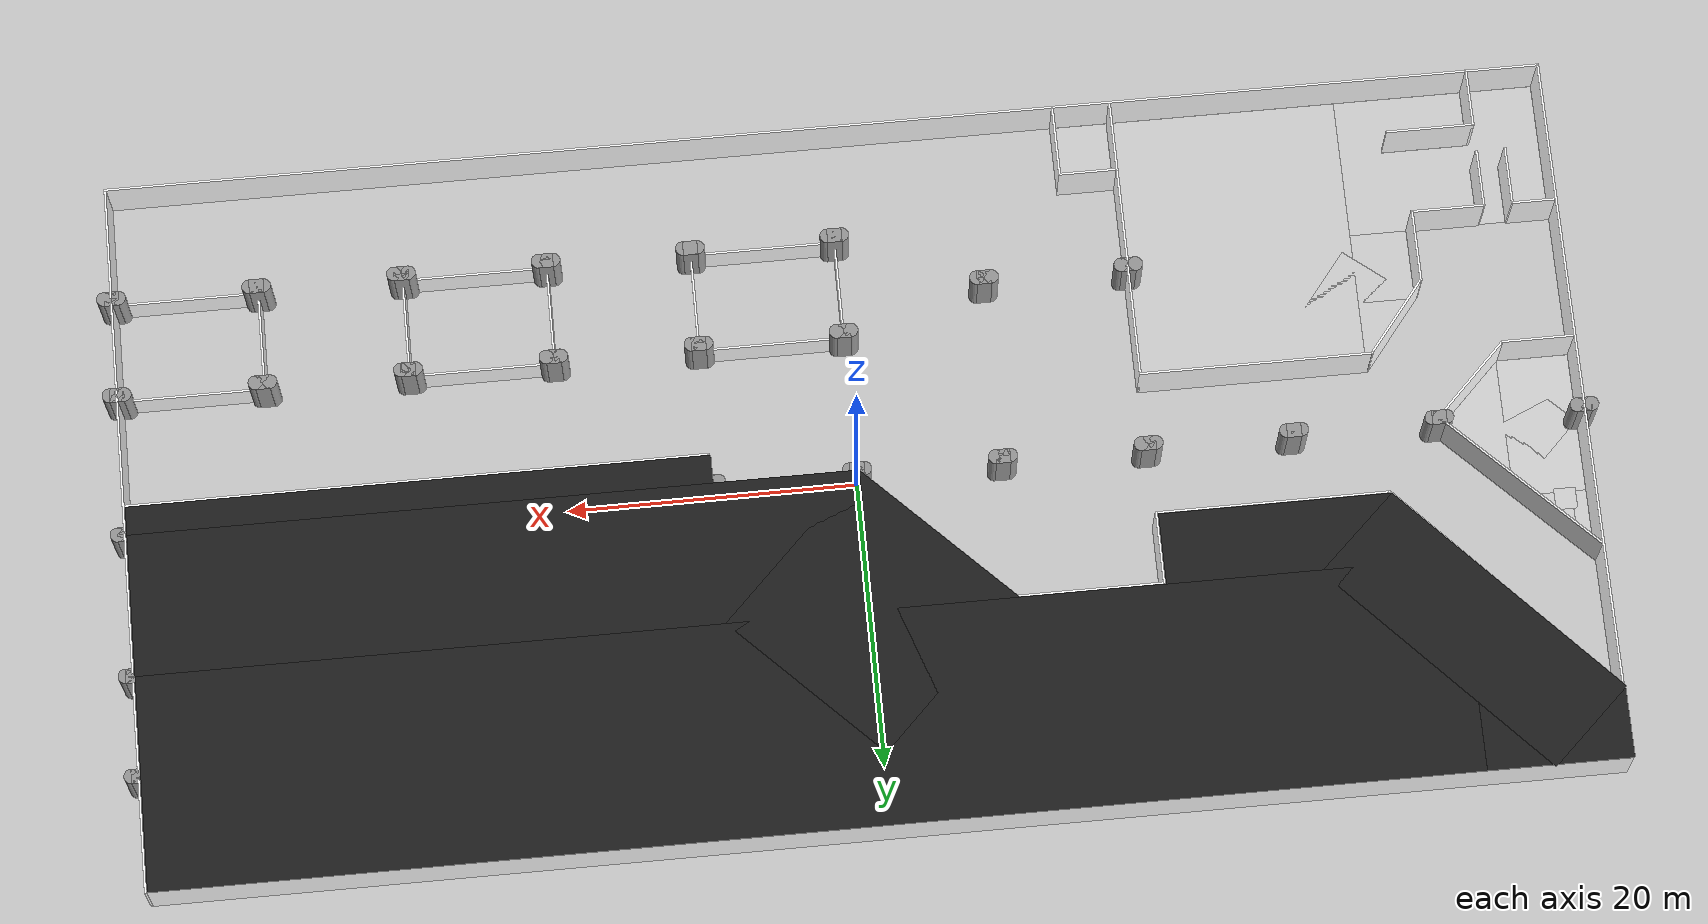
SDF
<sdf version="1.6">
 <world name="default">
  <light name="sun" type="directional">
   <pose>0 0 10 0 -0 0</pose>
   <diffuse>0.8 0.8 0.8 1</diffuse>
   <specular>0.2 0.2 0.2 1</specular>
   <attenuation>
    <range>1000</range>
    <constant>0.9</constant>
    <linear>0.01</linear>
    <quadratic>0.001</quadratic>
   </attenuation>
   <direction>-0.5 0.1 -0.9</direction>
  </light>
  <model name="ground_plane">
   <static>1</static>
   <link name="link">
    <collision name="collision">
     <geometry><plane><normal>0 0 1</normal><size>100 100</size></plane></geometry>
     <surface><friction><ode><mu>100</mu><mu2>50</mu2></ode></friction></surface>
    </collision>
    <visual name="visual">
     <cast_shadows>0</cast_shadows>
     <geometry><plane><normal>0 0 1</normal><size>100 100</size></plane></geometry>
     <material>
      <script><uri>file://media/materials/scripts/gazebo.material</uri><name>Gazebo/Grey</name></script>
     </material>
    </visual>
   </link>
  </model>
  <gravity>0 0 -9.8</gravity>
  <magnetic_field>6e-06 2.3e-05 -4.2e-05</magnetic_field>
  <atmosphere type="adiabatic"/>
  <physics name="default_physics" default="0" type="ode">
   <max_step_size>0.001</max_step_size>
   <real_time_factor>1</real_time_factor>
   <real_time_update_rate>1000</real_time_update_rate>
  </physics>
  <scene><ambient>0.4 0.4 0.4 1</ambient><background>0.7 0.7 0.7 1</background><shadows>1</shadows></scene>
  <spherical_coordinates>
   <surface_model>EARTH_WGS84</surface_model>
   <latitude_deg>0</latitude_deg>
   <longitude_deg>0</longitude_deg>
   <elevation>0</elevation>
   <heading_deg>0</heading_deg>
  </spherical_coordinates>
  <model name="outer_wall">
   <link name="Wall_12">
    <collision name="Wall_12_Collision">
     <geometry><box><size>100.15 0.15 4</size></box></geometry>
     <pose>0 0 2 0 -0 0</pose>
    </collision>
    <visual name="Wall_12_Visual">
     <pose>0 0 2 0 -0 0</pose>
     <geometry><box><size>100.15 0.15 4</size></box></geometry>
     <material>
      <script>
       <uri>file://media/materials/scripts/gray_tile_100.material</uri>
       <name>gray_tile_100/Diffuse</name>
      </script>
      <ambient>1 1 1 1</ambient>
     </material>
     <meta><layer>0</layer></meta>
    </visual>
    <pose>-1e-06 -25 0 0 -0 0</pose>
   </link>
   <link name="Wall_13">
    <collision name="Wall_13_Collision">
     <geometry><box><size>50.15 0.15 4</size></box></geometry>
     <pose>0 0 2 0 -0 0</pose>
    </collision>
    <visual name="Wall_13_Visual">
     <pose>0 0 2 0 -0 0</pose>
     <geometry><box><size>50.15 0.15 4</size></box></geometry>
     <material>
      <script>
       <uri>file://media/materials/scripts/gray_tile_50.material</uri>
       <name>gray_tile_50/Diffuse</name>
      </script>
      <ambient>1 1 1 1</ambient>
     </material>
     <meta><layer>0</layer></meta>
    </visual>
    <pose>50 -1e-06 0 0 -0 1.5708</pose>
   </link>
   <link name="Wall_14">
    <collision name="Wall_14_Collision">
     <geometry><box><size>100.15 0.15 4</size></box></geometry>
     <pose>0 0 2 0 -0 0</pose>
    </collision>
    <visual name="Wall_14_Visual">
     <pose>0 0 2 0 -0 0</pose>
     <geometry><box><size>100.15 0.15 4</size></box></geometry>
     <material>
      <script>
       <uri>file://media/materials/scripts/gray_tile_100.material</uri>
       <name>gray_tile_100/Diffuse</name>
      </script>
      <ambient>1 1 1 1</ambient>
     </material>
     <meta><layer>0</layer></meta>
    </visual>
    <pose>-1e-06 25 0 0 -0 3.14159</pose>
   </link>
   <link name="Wall_15">
    <collision name="Wall_15_Collision">
     <geometry><box><size>50.15 0.15 4</size></box></geometry>
     <pose>0 0 2 0 -0 0</pose>
    </collision>
    <visual name="Wall_15_Visual">
     <pose>0 0 2 0 -0 0</pose>
     <geometry><box><size>50.15 0.15 4</size></box></geometry>
     <material>
      <script>
       <uri>file://media/materials/scripts/gray_tile_50.material</uri>
       <name>gray_tile_50/Diffuse</name>
      </script>
      <ambient>1 1 1 1</ambient>
     </material>
     <meta><layer>0</layer></meta>
    </visual>
    <pose>-50 -1e-06 0 0 -0 -1.5708</pose>
   </link>
   <static>1</static>
  </model>
  <model name="restroom_wall">
   <pose>-25 -15 0 0 -0 0</pose>
   <link name="Wall_11">
    <collision name="Wall_11_Collision">
     <geometry><box><size>4.15 0.15 4</size></box></geometry>
     <pose>0 0 2 0 -0 0</pose>
    </collision>
    <visual name="Wall_11_Visual">
     <pose>0 0 2 0 -0 0</pose>
     <geometry><box><size>4.15 0.15 4</size></box></geometry>
     <material>
      <script>
       <uri>file://media/materials/scripts/gray_tile_10.material</uri>
       <name>gray_tile_10/Diffuse</name>
      </script>
      <ambient>1 1 1 1</ambient>
     </material>
     <meta><layer>0</layer></meta>
    </visual>
    <pose>-19.9625 -2.01521 0 0 -0 -1.5708</pose>
   </link>
   <link name="Wall_13">
    <collision name="Wall_13_Collision">
     <geometry><box><size>4.15 0.15 4</size></box></geometry>
     <pose>0 0 2 0 -0 0</pose>
    </collision>
    <visual name="Wall_13_Visual">
     <pose>0 0 2 0 -0 0</pose>
     <geometry><box><size>4.15 0.15 4</size></box></geometry>
     <material>
      <script>
       <uri>file://media/materials/scripts/gray_tile_10.material</uri>
       <name>gray_tile_10/Diffuse</name>
      </script>
      <ambient>1 1 1 1</ambient>
     </material>
     <meta><layer>0</layer></meta>
    </visual>
    <pose>-19.9625 -8.01521 0 0 -0 1.5708</pose>
   </link>
   <link name="Wall_14">
    <collision name="Wall_14_Collision">
     <geometry><box><size>6.15 0.15 4</size></box></geometry>
     <pose>0 0 2 0 -0 0</pose>
    </collision>
    <visual name="Wall_14_Visual">
     <pose>0 0 2 0 -0 0</pose>
     <geometry><box><size>6.15 0.15 4</size></box></geometry>
     <material>
      <script>
       <uri>file://media/materials/scripts/gray_tile_10.material</uri>
       <name>gray_tile_10/Diffuse</name>
      </script>
      <ambient>1 1 1 1</ambient>
     </material>
     <meta><layer>0</layer></meta>
    </visual>
    <pose>-16.9625 -6.01521 0 0 -0 0</pose>
   </link>
   <link name="Wall_16">
    <collision name="Wall_16_Collision">
     <geometry><box><size>4.15 0.15 4</size></box></geometry>
     <pose>0 0 2 0 -0 0</pose>
    </collision>
    <visual name="Wall_16_Visual">
     <pose>0 0 2 0 -0 0</pose>
     <geometry><box><size>4.15 0.15 4</size></box></geometry>
     <material>
      <script>
       <uri>file://media/materials/scripts/gray_tile_10.material</uri>
       <name>gray_tile_10/Diffuse</name>
      </script>
      <ambient>1 1 1 1</ambient>
     </material>
     <meta><layer>0</layer></meta>
    </visual>
    <pose>7.0375 -5.01521 0 0 -0 0</pose>
   </link>
   <link name="Wall_17">
    <collision name="Wall_17_Collision">
     <geometry><box><size>5.15 0.15 4</size></box></geometry>
     <pose>0 0 2 0 -0 0</pose>
    </collision>
    <visual name="Wall_17_Visual">
     <pose>0 0 2 0 -0 0</pose>
     <geometry><box><size>5.15 0.15 4</size></box></geometry>
     <material>
      <script>
       <uri>file://media/materials/scripts/gray_tile_10.material</uri>
       <name>gray_tile_10/Diffuse</name>
      </script>
      <ambient>1 1 1 1</ambient>
     </material>
     <meta><layer>0</layer></meta>
    </visual>
    <pose>9.0375 -7.51521 0 0 -0 -1.5708</pose>
   </link>
   <link name="Wall_2">
    <pose>-19.9625 -0.015208 0 0 -0 0</pose>
    <visual name="Wall_2_Visual_0">
     <pose>-3.5375 0 2 0 -0 0</pose>
     <geometry><box><size>3.075 0.15 4</size></box></geometry>
     <material>
      <script>
       <uri>file://media/materials/scripts/gray_tile_10.material</uri>
       <name>gray_tile_10/Diffuse</name>
      </script>
      <ambient>1 1 1 1</ambient>
     </material>
     <meta><layer>0</layer></meta>
    </visual>
    <collision name="Wall_2_Collision_0">
     <geometry><box><size>3.075 0.15 4</size></box></geometry>
     <pose>-3.5375 0 2 0 -0 0</pose>
    </collision>
    <visual name="Wall_2_Visual_1">
     <pose>2.5375 0 2 0 -0 0</pose>
     <geometry><box><size>5.075 0.15 4</size></box></geometry>
     <material>
      <script>
       <uri>file://media/materials/scripts/gray_tile_10.material</uri>
       <name>gray_tile_10/Diffuse</name>
      </script>
      <ambient>1 1 1 1</ambient>
     </material>
     <meta><layer>0</layer></meta>
    </visual>
    <collision name="Wall_2_Collision_1">
     <geometry><box><size>5.075 0.15 4</size></box></geometry>
     <pose>2.5375 0 2 0 -0 0</pose>
    </collision>
   </link>
   <link name="Wall_3">
    <collision name="Wall_3_Collision">
     <geometry><box><size>5.15 0.15 4</size></box></geometry>
     <pose>0 0 2 0 -0 0</pose>
    </collision>
    <visual name="Wall_3_Visual">
     <pose>0 0 2 0 -0 0</pose>
     <geometry><box><size>5.15 0.15 4</size></box></geometry>
     <material>
      <script>
       <uri>file://media/materials/scripts/gray_tile_10.material</uri>
       <name>gray_tile_10/Diffuse</name>
      </script>
      <ambient>1 1 1 1</ambient>
     </material>
     <meta><layer>0</layer></meta>
    </visual>
    <pose>-14.9625 2.48479 0 0 -0 1.5708</pose>
   </link>
   <link name="Wall_4">
    <collision name="Wall_4_Collision">
     <geometry><box><size>6.55312 0.15 4</size></box></geometry>
     <pose>0 0 2 0 -0 0</pose>
    </collision>
    <visual name="Wall_4_Visual">
     <pose>0 0 2 0 -0 0</pose>
     <geometry><box><size>6.55312 0.15 4</size></box></geometry>
     <material>
      <script>
       <uri>file://media/materials/scripts/gray_tile_10.material</uri>
       <name>gray_tile_10/Diffuse</name>
      </script>
      <ambient>1 1 1 1</ambient>
     </material>
     <meta><layer>0</layer></meta>
    </visual>
    <pose>-12.9625 7.48479 0 0 -0 0.896055</pose>
   </link>
   <link name="Wall_5">
    <collision name="Wall_5_Collision">
     <geometry><box><size>16.15 0.15 4</size></box></geometry>
     <pose>0 0 2 0 -0 0</pose>
    </collision>
    <visual name="Wall_5_Visual">
     <pose>0 0 2 0 -0 0</pose>
     <geometry><box><size>16.15 0.15 4</size></box></geometry>
     <material>
      <script>
       <uri>file://media/materials/scripts/gray_tile_10.material</uri>
       <name>gray_tile_10/Diffuse</name>
      </script>
      <ambient>1 1 1 1</ambient>
     </material>
     <meta><layer>0</layer></meta>
    </visual>
    <pose>-2.9625 9.98479 0 0 -0 0</pose>
   </link>
   <link name="Wall_6">
    <collision name="Wall_6_Collision">
     <geometry><box><size>20.15 0.15 4</size></box></geometry>
     <pose>0 0 2 0 -0 0</pose>
    </collision>
    <visual name="Wall_6_Visual">
     <pose>0 0 2 0 -0 0</pose>
     <geometry><box><size>20.15 0.15 4</size></box></geometry>
     <material>
      <script>
       <uri>file://media/materials/scripts/gray_tile_10.material</uri>
       <name>gray_tile_10/Diffuse</name>
      </script>
      <ambient>1 1 1 1</ambient>
     </material>
     <meta><layer>0</layer></meta>
    </visual>
    <pose>5.0375 -0.015208 0 0 -0 -1.5708</pose>
   </link>
   <link name="Wall_9">
    <collision name="Wall_9_Collision">
     <geometry><box><size>4.15 0.15 4</size></box></geometry>
     <pose>0 0 2 0 -0 0</pose>
    </collision>
    <visual name="Wall_9_Visual">
     <pose>0 0 2 0 -0 0</pose>
     <geometry><box><size>4.15 0.15 4</size></box></geometry>
     <material>
      <script>
       <uri>file://media/materials/scripts/gray_tile_10.material</uri>
       <name>gray_tile_10/Diffuse</name>
      </script>
      <ambient>1 1 1 1</ambient>
     </material>
     <meta><layer>0</layer></meta>
    </visual>
    <pose>-21.9455 -2.01521 0 0 -0 -1.5708</pose>
   </link>
   <static>1</static>
  </model>
  <model name="pillar">
   <link name="link_0">
    <inertial>
     <mass>1</mass>
     <inertia>
      <ixx>0.166667</ixx>
      <ixy>0</ixy>
      <ixz>0</ixz>
      <iyy>0.166667</iyy>
      <iyz>0</iyz>
      <izz>0.166667</izz>
     </inertia>
    </inertial>
    <kinematic>1</kinematic>
    <visual name="visual">
     <geometry><box><size>1 1 4</size></box></geometry>
     <material>
      <lighting>1</lighting>
      <script><uri>file://media/materials/scripts/gazebo.material</uri><name>Gazebo/Grey</name></script>
      <shader type="pixel"><normal_map>__default__</normal_map></shader>
      <ambient>0.3 0.3 0.3 1</ambient>
      <diffuse>0.7 0.7 0.7 1</diffuse>
      <specular>0.01 0.01 0.01 1</specular>
      <emissive>0 0 0 1</emissive>
     </material>
    </visual>
    <collision name="collision">
     <geometry><box><size>1 1 4</size></box></geometry>
     <surface>
      <friction>
       <ode><mu>1</mu><mu2>1</mu2><fdir1>0 0 0</fdir1><slip1>0</slip1><slip2>0</slip2></ode>
       <torsional>
        <coefficient>1</coefficient>
        <patch_radius>0</patch_radius>
        <surface_radius>0</surface_radius>
        <use_patch_radius>1</use_patch_radius>
        <ode><slip>0</slip></ode>
       </torsional>
      </friction>
      <bounce><restitution_coefficient>0</restitution_coefficient><threshold>1e+06</threshold></bounce>
      <contact>
       <collide_without_contact>0</collide_without_contact>
       <collide_without_contact_bitmask>1</collide_without_contact_bitmask>
       <collide_bitmask>1</collide_bitmask>
       <ode>
        <soft_cfm>0</soft_cfm>
        <soft_erp>0.2</soft_erp>
        <kp>1e+13</kp>
        <kd>1</kd>
        <max_vel>0.01</max_vel>
        <min_depth>0</min_depth>
       </ode>
       <bullet>
        <split_impulse>1</split_impulse>
        <split_impulse_penetration_threshold>-0.01</split_impulse_penetration_threshold>
        <soft_cfm>0</soft_cfm>
        <soft_erp>0.2</soft_erp>
        <kp>1e+13</kp>
        <kd>1</kd>
       </bullet>
      </contact>
     </surface>
    </collision>
   </link>
   <link name="link_1">
    <inertial>
     <mass>1</mass>
     <inertia><ixx>0.145833</ixx><ixy>0</ixy><ixz>0</ixz><iyy>0.145833</iyy><iyz>0</iyz><izz>0.125</izz></inertia>
    </inertial>
    <pose>-0.5 0 0 0 -0 0</pose>
    <kinematic>1</kinematic>
    <visual name="visual">
     <geometry><cylinder><radius>0.5</radius><length>4</length></cylinder></geometry>
     <material>
      <lighting>1</lighting>
      <script><uri>file://media/materials/scripts/gazebo.material</uri><name>Gazebo/Grey</name></script>
      <shader type="pixel"><normal_map>__default__</normal_map></shader>
      <ambient>0.3 0.3 0.3 1</ambient>
      <diffuse>0.7 0.7 0.7 1</diffuse>
      <specular>0.01 0.01 0.01 1</specular>
      <emissive>0 0 0 1</emissive>
     </material>
    </visual>
    <collision name="collision">
     <geometry><cylinder><radius>0.5</radius><length>4</length></cylinder></geometry>
     <surface>
      <friction>
       <ode><mu>1</mu><mu2>1</mu2><fdir1>0 0 0</fdir1><slip1>0</slip1><slip2>0</slip2></ode>
       <torsional>
        <coefficient>1</coefficient>
        <patch_radius>0</patch_radius>
        <surface_radius>0</surface_radius>
        <use_patch_radius>1</use_patch_radius>
        <ode><slip>0</slip></ode>
       </torsional>
      </friction>
      <bounce><restitution_coefficient>0</restitution_coefficient><threshold>1e+06</threshold></bounce>
      <contact>
       <collide_without_contact>0</collide_without_contact>
       <collide_without_contact_bitmask>1</collide_without_contact_bitmask>
       <collide_bitmask>1</collide_bitmask>
       <ode>
        <soft_cfm>0</soft_cfm>
        <soft_erp>0.2</soft_erp>
        <kp>1e+13</kp>
        <kd>1</kd>
        <max_vel>0.01</max_vel>
        <min_depth>0</min_depth>
       </ode>
       <bullet>
        <split_impulse>1</split_impulse>
        <split_impulse_penetration_threshold>-0.01</split_impulse_penetration_threshold>
        <soft_cfm>0</soft_cfm>
        <soft_erp>0.2</soft_erp>
        <kp>1e+13</kp>
        <kd>1</kd>
       </bullet>
      </contact>
     </surface>
    </collision>
   </link>
   <link name="link_2">
    <inertial>
     <mass>1</mass>
     <inertia><ixx>0.145833</ixx><ixy>0</ixy><ixz>0</ixz><iyy>0.145833</iyy><iyz>0</iyz><izz>0.125</izz></inertia>
    </inertial>
    <pose>0.5 0 0 0 -0 0</pose>
    <kinematic>1</kinematic>
    <visual name="visual">
     <geometry><cylinder><radius>0.5</radius><length>4</length></cylinder></geometry>
     <material>
      <lighting>1</lighting>
      <script><uri>file://media/materials/scripts/gazebo.material</uri><name>Gazebo/Grey</name></script>
      <shader type="pixel"><normal_map>__default__</normal_map></shader>
      <ambient>0.3 0.3 0.3 1</ambient>
      <diffuse>0.7 0.7 0.7 1</diffuse>
      <specular>0.01 0.01 0.01 1</specular>
      <emissive>0 0 0 1</emissive>
     </material>
    </visual>
    <collision name="collision">
     <geometry><cylinder><radius>0.5</radius><length>4</length></cylinder></geometry>
     <surface>
      <friction>
       <ode><mu>1</mu><mu2>1</mu2><fdir1>0 0 0</fdir1><slip1>0</slip1><slip2>0</slip2></ode>
       <torsional>
        <coefficient>1</coefficient>
        <patch_radius>0</patch_radius>
        <surface_radius>0</surface_radius>
        <use_patch_radius>1</use_patch_radius>
        <ode><slip>0</slip></ode>
       </torsional>
      </friction>
      <bounce><restitution_coefficient>0</restitution_coefficient><threshold>1e+06</threshold></bounce>
      <contact>
       <collide_without_contact>0</collide_without_contact>
       <collide_without_contact_bitmask>1</collide_without_contact_bitmask>
       <collide_bitmask>1</collide_bitmask>
       <ode>
        <soft_cfm>0</soft_cfm>
        <soft_erp>0.2</soft_erp>
        <kp>1e+13</kp>
        <kd>1</kd>
        <max_vel>0.01</max_vel>
        <min_depth>0</min_depth>
       </ode>
       <bullet>
        <split_impulse>1</split_impulse>
        <split_impulse_penetration_threshold>-0.01</split_impulse_penetration_threshold>
        <soft_cfm>0</soft_cfm>
        <soft_erp>0.2</soft_erp>
        <kp>1e+13</kp>
        <kd>1</kd>
       </bullet>
      </contact>
     </surface>
    </collision>
   </link>
   <static>1</static>
   <pose>-20 -13 2 0 -0 0</pose>
  </model>
  <model name="pillar_clone">
   <link name="link_0">
    <inertial>
     <mass>1</mass>
     <inertia>
      <ixx>0.166667</ixx>
      <ixy>0</ixy>
      <ixz>0</ixz>
      <iyy>0.166667</iyy>
      <iyz>0</iyz>
      <izz>0.166667</izz>
     </inertia>
    </inertial>
    <kinematic>1</kinematic>
    <visual name="visual">
     <geometry><box><size>1 1 4</size></box></geometry>
     <material>
      <lighting>1</lighting>
      <script><uri>file://media/materials/scripts/gazebo.material</uri><name>Gazebo/Grey</name></script>
      <shader type="pixel"><normal_map>__default__</normal_map></shader>
      <ambient>0.3 0.3 0.3 1</ambient>
      <diffuse>0.7 0.7 0.7 1</diffuse>
      <specular>0.01 0.01 0.01 1</specular>
      <emissive>0 0 0 1</emissive>
     </material>
    </visual>
    <collision name="collision">
     <geometry><box><size>1 1 4</size></box></geometry>
     <surface>
      <friction>
       <ode><mu>1</mu><mu2>1</mu2><fdir1>0 0 0</fdir1><slip1>0</slip1><slip2>0</slip2></ode>
       <torsional>
        <coefficient>1</coefficient>
        <patch_radius>0</patch_radius>
        <surface_radius>0</surface_radius>
        <use_patch_radius>1</use_patch_radius>
        <ode><slip>0</slip></ode>
       </torsional>
      </friction>
      <bounce><restitution_coefficient>0</restitution_coefficient><threshold>1e+06</threshold></bounce>
      <contact>
       <collide_without_contact>0</collide_without_contact>
       <collide_without_contact_bitmask>1</collide_without_contact_bitmask>
       <collide_bitmask>1</collide_bitmask>
       <ode>
        <soft_cfm>0</soft_cfm>
        <soft_erp>0.2</soft_erp>
        <kp>1e+13</kp>
        <kd>1</kd>
        <max_vel>0.01</max_vel>
        <min_depth>0</min_depth>
       </ode>
       <bullet>
        <split_impulse>1</split_impulse>
        <split_impulse_penetration_threshold>-0.01</split_impulse_penetration_threshold>
        <soft_cfm>0</soft_cfm>
        <soft_erp>0.2</soft_erp>
        <kp>1e+13</kp>
        <kd>1</kd>
       </bullet>
      </contact>
     </surface>
    </collision>
   </link>
   <link name="link_1">
    <inertial>
     <mass>1</mass>
     <inertia><ixx>0.145833</ixx><ixy>0</ixy><ixz>0</ixz><iyy>0.145833</iyy><iyz>0</iyz><izz>0.125</izz></inertia>
    </inertial>
    <pose>-0.5 0 0 0 -0 0</pose>
    <kinematic>1</kinematic>
    <visual name="visual">
     <geometry><cylinder><radius>0.5</radius><length>4</length></cylinder></geometry>
     <material>
      <lighting>1</lighting>
      <script><uri>file://media/materials/scripts/gazebo.material</uri><name>Gazebo/Grey</name></script>
      <shader type="pixel"><normal_map>__default__</normal_map></shader>
      <ambient>0.3 0.3 0.3 1</ambient>
      <diffuse>0.7 0.7 0.7 1</diffuse>
      <specular>0.01 0.01 0.01 1</specular>
      <emissive>0 0 0 1</emissive>
     </material>
    </visual>
    <collision name="collision">
     <geometry><cylinder><radius>0.5</radius><length>4</length></cylinder></geometry>
     <surface>
      <friction>
       <ode><mu>1</mu><mu2>1</mu2><fdir1>0 0 0</fdir1><slip1>0</slip1><slip2>0</slip2></ode>
       <torsional>
        <coefficient>1</coefficient>
        <patch_radius>0</patch_radius>
        <surface_radius>0</surface_radius>
        <use_patch_radius>1</use_patch_radius>
        <ode><slip>0</slip></ode>
       </torsional>
      </friction>
      <bounce><restitution_coefficient>0</restitution_coefficient><threshold>1e+06</threshold></bounce>
      <contact>
       <collide_without_contact>0</collide_without_contact>
       <collide_without_contact_bitmask>1</collide_without_contact_bitmask>
       <collide_bitmask>1</collide_bitmask>
       <ode>
        <soft_cfm>0</soft_cfm>
        <soft_erp>0.2</soft_erp>
        <kp>1e+13</kp>
        <kd>1</kd>
        <max_vel>0.01</max_vel>
        <min_depth>0</min_depth>
       </ode>
       <bullet>
        <split_impulse>1</split_impulse>
        <split_impulse_penetration_threshold>-0.01</split_impulse_penetration_threshold>
        <soft_cfm>0</soft_cfm>
        <soft_erp>0.2</soft_erp>
        <kp>1e+13</kp>
        <kd>1</kd>
       </bullet>
      </contact>
     </surface>
    </collision>
   </link>
   <link name="link_2">
    <inertial>
     <mass>1</mass>
     <inertia><ixx>0.145833</ixx><ixy>0</ixy><ixz>0</ixz><iyy>0.145833</iyy><iyz>0</iyz><izz>0.125</izz></inertia>
    </inertial>
    <pose>0.5 0 0 0 -0 0</pose>
    <kinematic>1</kinematic>
    <visual name="visual">
     <geometry><cylinder><radius>0.5</radius><length>4</length></cylinder></geometry>
     <material>
      <lighting>1</lighting>
      <script><uri>file://media/materials/scripts/gazebo.material</uri><name>Gazebo/Grey</name></script>
      <shader type="pixel"><normal_map>__default__</normal_map></shader>
      <ambient>0.3 0.3 0.3 1</ambient>
      <diffuse>0.7 0.7 0.7 1</diffuse>
      <specular>0.01 0.01 0.01 1</specular>
      <emissive>0 0 0 1</emissive>
     </material>
    </visual>
    <collision name="collision">
     <geometry><cylinder><radius>0.5</radius><length>4</length></cylinder></geometry>
     <surface>
      <friction>
       <ode><mu>1</mu><mu2>1</mu2><fdir1>0 0 0</fdir1><slip1>0</slip1><slip2>0</slip2></ode>
       <torsional>
        <coefficient>1</coefficient>
        <patch_radius>0</patch_radius>
        <surface_radius>0</surface_radius>
        <use_patch_radius>1</use_patch_radius>
        <ode><slip>0</slip></ode>
       </torsional>
      </friction>
      <bounce><restitution_coefficient>0</restitution_coefficient><threshold>1e+06</threshold></bounce>
      <contact>
       <collide_without_contact>0</collide_without_contact>
       <collide_without_contact_bitmask>1</collide_without_contact_bitmask>
       <collide_bitmask>1</collide_bitmask>
       <ode>
        <soft_cfm>0</soft_cfm>
        <soft_erp>0.2</soft_erp>
        <kp>1e+13</kp>
        <kd>1</kd>
        <max_vel>0.01</max_vel>
        <min_depth>0</min_depth>
       </ode>
       <bullet>
        <split_impulse>1</split_impulse>
        <split_impulse_penetration_threshold>-0.01</split_impulse_penetration_threshold>
        <soft_cfm>0</soft_cfm>
        <soft_erp>0.2</soft_erp>
        <kp>1e+13</kp>
        <kd>1</kd>
       </bullet>
      </contact>
     </surface>
    </collision>
   </link>
   <static>1</static>
   <pose>-10 -13 2 0 -0 0</pose>
  </model>
  <model name="pillar_clone_0">
   <link name="link_0">
    <inertial>
     <mass>1</mass>
     <inertia>
      <ixx>0.166667</ixx>
      <ixy>0</ixy>
      <ixz>0</ixz>
      <iyy>0.166667</iyy>
      <iyz>0</iyz>
      <izz>0.166667</izz>
     </inertia>
    </inertial>
    <kinematic>1</kinematic>
    <visual name="visual">
     <geometry><box><size>1 1 4</size></box></geometry>
     <material>
      <lighting>1</lighting>
      <script><uri>file://media/materials/scripts/gazebo.material</uri><name>Gazebo/Grey</name></script>
      <shader type="pixel"><normal_map>__default__</normal_map></shader>
      <ambient>0.3 0.3 0.3 1</ambient>
      <diffuse>0.7 0.7 0.7 1</diffuse>
      <specular>0.01 0.01 0.01 1</specular>
      <emissive>0 0 0 1</emissive>
     </material>
    </visual>
    <collision name="collision">
     <geometry><box><size>1 1 4</size></box></geometry>
     <surface>
      <friction>
       <ode><mu>1</mu><mu2>1</mu2><fdir1>0 0 0</fdir1><slip1>0</slip1><slip2>0</slip2></ode>
       <torsional>
        <coefficient>1</coefficient>
        <patch_radius>0</patch_radius>
        <surface_radius>0</surface_radius>
        <use_patch_radius>1</use_patch_radius>
        <ode><slip>0</slip></ode>
       </torsional>
      </friction>
      <bounce><restitution_coefficient>0</restitution_coefficient><threshold>1e+06</threshold></bounce>
      <contact>
       <collide_without_contact>0</collide_without_contact>
       <collide_without_contact_bitmask>1</collide_without_contact_bitmask>
       <collide_bitmask>1</collide_bitmask>
       <ode>
        <soft_cfm>0</soft_cfm>
        <soft_erp>0.2</soft_erp>
        <kp>1e+13</kp>
        <kd>1</kd>
        <max_vel>0.01</max_vel>
        <min_depth>0</min_depth>
       </ode>
       <bullet>
        <split_impulse>1</split_impulse>
        <split_impulse_penetration_threshold>-0.01</split_impulse_penetration_threshold>
        <soft_cfm>0</soft_cfm>
        <soft_erp>0.2</soft_erp>
        <kp>1e+13</kp>
        <kd>1</kd>
       </bullet>
      </contact>
     </surface>
    </collision>
   </link>
   <link name="link_1">
    <inertial>
     <mass>1</mass>
     <inertia><ixx>0.145833</ixx><ixy>0</ixy><ixz>0</ixz><iyy>0.145833</iyy><iyz>0</iyz><izz>0.125</izz></inertia>
    </inertial>
    <pose>-0.5 0 0 0 -0 0</pose>
    <kinematic>1</kinematic>
    <visual name="visual">
     <geometry><cylinder><radius>0.5</radius><length>4</length></cylinder></geometry>
     <material>
      <lighting>1</lighting>
      <script><uri>file://media/materials/scripts/gazebo.material</uri><name>Gazebo/Grey</name></script>
      <shader type="pixel"><normal_map>__default__</normal_map></shader>
      <ambient>0.3 0.3 0.3 1</ambient>
      <diffuse>0.7 0.7 0.7 1</diffuse>
      <specular>0.01 0.01 0.01 1</specular>
      <emissive>0 0 0 1</emissive>
     </material>
    </visual>
    <collision name="collision">
     <geometry><cylinder><radius>0.5</radius><length>4</length></cylinder></geometry>
     <surface>
      <friction>
       <ode><mu>1</mu><mu2>1</mu2><fdir1>0 0 0</fdir1><slip1>0</slip1><slip2>0</slip2></ode>
       <torsional>
        <coefficient>1</coefficient>
        <patch_radius>0</patch_radius>
        <surface_radius>0</surface_radius>
        <use_patch_radius>1</use_patch_radius>
        <ode><slip>0</slip></ode>
       </torsional>
      </friction>
      <bounce><restitution_coefficient>0</restitution_coefficient><threshold>1e+06</threshold></bounce>
      <contact>
       <collide_without_contact>0</collide_without_contact>
       <collide_without_contact_bitmask>1</collide_without_contact_bitmask>
       <collide_bitmask>1</collide_bitmask>
       <ode>
        <soft_cfm>0</soft_cfm>
        <soft_erp>0.2</soft_erp>
        <kp>1e+13</kp>
        <kd>1</kd>
        <max_vel>0.01</max_vel>
        <min_depth>0</min_depth>
       </ode>
       <bullet>
        <split_impulse>1</split_impulse>
        <split_impulse_penetration_threshold>-0.01</split_impulse_penetration_threshold>
        <soft_cfm>0</soft_cfm>
        <soft_erp>0.2</soft_erp>
        <kp>1e+13</kp>
        <kd>1</kd>
       </bullet>
      </contact>
     </surface>
    </collision>
   </link>
   <link name="link_2">
    <inertial>
     <mass>1</mass>
     <inertia><ixx>0.145833</ixx><ixy>0</ixy><ixz>0</ixz><iyy>0.145833</iyy><iyz>0</iyz><izz>0.125</izz></inertia>
    </inertial>
    <pose>0.5 0 0 0 -0 0</pose>
    <kinematic>1</kinematic>
    <visual name="visual">
     <geometry><cylinder><radius>0.5</radius><length>4</length></cylinder></geometry>
     <material>
      <lighting>1</lighting>
      <script><uri>file://media/materials/scripts/gazebo.material</uri><name>Gazebo/Grey</name></script>
      <shader type="pixel"><normal_map>__default__</normal_map></shader>
      <ambient>0.3 0.3 0.3 1</ambient>
      <diffuse>0.7 0.7 0.7 1</diffuse>
      <specular>0.01 0.01 0.01 1</specular>
      <emissive>0 0 0 1</emissive>
     </material>
    </visual>
    <collision name="collision">
     <geometry><cylinder><radius>0.5</radius><length>4</length></cylinder></geometry>
     <surface>
      <friction>
       <ode><mu>1</mu><mu2>1</mu2><fdir1>0 0 0</fdir1><slip1>0</slip1><slip2>0</slip2></ode>
       <torsional>
        <coefficient>1</coefficient>
        <patch_radius>0</patch_radius>
        <surface_radius>0</surface_radius>
        <use_patch_radius>1</use_patch_radius>
        <ode><slip>0</slip></ode>
       </torsional>
      </friction>
      <bounce><restitution_coefficient>0</restitution_coefficient><threshold>1e+06</threshold></bounce>
      <contact>
       <collide_without_contact>0</collide_without_contact>
       <collide_without_contact_bitmask>1</collide_without_contact_bitmask>
       <collide_bitmask>1</collide_bitmask>
       <ode>
        <soft_cfm>0</soft_cfm>
        <soft_erp>0.2</soft_erp>
        <kp>1e+13</kp>
        <kd>1</kd>
        <max_vel>0.01</max_vel>
        <min_depth>0</min_depth>
       </ode>
       <bullet>
        <split_impulse>1</split_impulse>
        <split_impulse_penetration_threshold>-0.01</split_impulse_penetration_threshold>
        <soft_cfm>0</soft_cfm>
        <soft_erp>0.2</soft_erp>
        <kp>1e+13</kp>
        <kd>1</kd>
       </bullet>
      </contact>
     </surface>
    </collision>
   </link>
   <static>1</static>
   <pose>0 -17 2 0 -0 0</pose>
  </model>
  <model name="pillar_clone_1">
   <link name="link_0">
    <inertial>
     <mass>1</mass>
     <inertia>
      <ixx>0.166667</ixx>
      <ixy>0</ixy>
      <ixz>0</ixz>
      <iyy>0.166667</iyy>
      <iyz>0</iyz>
      <izz>0.166667</izz>
     </inertia>
    </inertial>
    <kinematic>1</kinematic>
    <visual name="visual">
     <geometry><box><size>1 1 4</size></box></geometry>
     <material>
      <lighting>1</lighting>
      <script><uri>file://media/materials/scripts/gazebo.material</uri><name>Gazebo/Grey</name></script>
      <shader type="pixel"><normal_map>__default__</normal_map></shader>
      <ambient>0.3 0.3 0.3 1</ambient>
      <diffuse>0.7 0.7 0.7 1</diffuse>
      <specular>0.01 0.01 0.01 1</specular>
      <emissive>0 0 0 1</emissive>
     </material>
    </visual>
    <collision name="collision">
     <geometry><box><size>1 1 4</size></box></geometry>
     <surface>
      <friction>
       <ode><mu>1</mu><mu2>1</mu2><fdir1>0 0 0</fdir1><slip1>0</slip1><slip2>0</slip2></ode>
       <torsional>
        <coefficient>1</coefficient>
        <patch_radius>0</patch_radius>
        <surface_radius>0</surface_radius>
        <use_patch_radius>1</use_patch_radius>
        <ode><slip>0</slip></ode>
       </torsional>
      </friction>
      <bounce><restitution_coefficient>0</restitution_coefficient><threshold>1e+06</threshold></bounce>
      <contact>
       <collide_without_contact>0</collide_without_contact>
       <collide_without_contact_bitmask>1</collide_without_contact_bitmask>
       <collide_bitmask>1</collide_bitmask>
       <ode>
        <soft_cfm>0</soft_cfm>
        <soft_erp>0.2</soft_erp>
        <kp>1e+13</kp>
        <kd>1</kd>
        <max_vel>0.01</max_vel>
        <min_depth>0</min_depth>
       </ode>
       <bullet>
        <split_impulse>1</split_impulse>
        <split_impulse_penetration_threshold>-0.01</split_impulse_penetration_threshold>
        <soft_cfm>0</soft_cfm>
        <soft_erp>0.2</soft_erp>
        <kp>1e+13</kp>
        <kd>1</kd>
       </bullet>
      </contact>
     </surface>
    </collision>
   </link>
   <link name="link_1">
    <inertial>
     <mass>1</mass>
     <inertia><ixx>0.145833</ixx><ixy>0</ixy><ixz>0</ixz><iyy>0.145833</iyy><iyz>0</iyz><izz>0.125</izz></inertia>
    </inertial>
    <pose>-0.5 0 0 0 -0 0</pose>
    <kinematic>1</kinematic>
    <visual name="visual">
     <geometry><cylinder><radius>0.5</radius><length>4</length></cylinder></geometry>
     <material>
      <lighting>1</lighting>
      <script><uri>file://media/materials/scripts/gazebo.material</uri><name>Gazebo/Grey</name></script>
      <shader type="pixel"><normal_map>__default__</normal_map></shader>
      <ambient>0.3 0.3 0.3 1</ambient>
      <diffuse>0.7 0.7 0.7 1</diffuse>
      <specular>0.01 0.01 0.01 1</specular>
      <emissive>0 0 0 1</emissive>
     </material>
    </visual>
    <collision name="collision">
     <geometry><cylinder><radius>0.5</radius><length>4</length></cylinder></geometry>
     <surface>
      <friction>
       <ode><mu>1</mu><mu2>1</mu2><fdir1>0 0 0</fdir1><slip1>0</slip1><slip2>0</slip2></ode>
       <torsional>
        <coefficient>1</coefficient>
        <patch_radius>0</patch_radius>
        <surface_radius>0</surface_radius>
        <use_patch_radius>1</use_patch_radius>
        <ode><slip>0</slip></ode>
       </torsional>
      </friction>
      <bounce><restitution_coefficient>0</restitution_coefficient><threshold>1e+06</threshold></bounce>
      <contact>
       <collide_without_contact>0</collide_without_contact>
       <collide_without_contact_bitmask>1</collide_without_contact_bitmask>
       <collide_bitmask>1</collide_bitmask>
       <ode>
        <soft_cfm>0</soft_cfm>
        <soft_erp>0.2</soft_erp>
        <kp>1e+13</kp>
        <kd>1</kd>
        <max_vel>0.01</max_vel>
        <min_depth>0</min_depth>
       </ode>
       <bullet>
        <split_impulse>1</split_impulse>
        <split_impulse_penetration_threshold>-0.01</split_impulse_penetration_threshold>
        <soft_cfm>0</soft_cfm>
        <soft_erp>0.2</soft_erp>
        <kp>1e+13</kp>
        <kd>1</kd>
       </bullet>
      </contact>
     </surface>
    </collision>
   </link>
   <link name="link_2">
    <inertial>
     <mass>1</mass>
     <inertia><ixx>0.145833</ixx><ixy>0</ixy><ixz>0</ixz><iyy>0.145833</iyy><iyz>0</iyz><izz>0.125</izz></inertia>
    </inertial>
    <pose>0.5 0 0 0 -0 0</pose>
    <kinematic>1</kinematic>
    <visual name="visual">
     <geometry><cylinder><radius>0.5</radius><length>4</length></cylinder></geometry>
     <material>
      <lighting>1</lighting>
      <script><uri>file://media/materials/scripts/gazebo.material</uri><name>Gazebo/Grey</name></script>
      <shader type="pixel"><normal_map>__default__</normal_map></shader>
      <ambient>0.3 0.3 0.3 1</ambient>
      <diffuse>0.7 0.7 0.7 1</diffuse>
      <specular>0.01 0.01 0.01 1</specular>
      <emissive>0 0 0 1</emissive>
     </material>
    </visual>
    <collision name="collision">
     <geometry><cylinder><radius>0.5</radius><length>4</length></cylinder></geometry>
     <surface>
      <friction>
       <ode><mu>1</mu><mu2>1</mu2><fdir1>0 0 0</fdir1><slip1>0</slip1><slip2>0</slip2></ode>
       <torsional>
        <coefficient>1</coefficient>
        <patch_radius>0</patch_radius>
        <surface_radius>0</surface_radius>
        <use_patch_radius>1</use_patch_radius>
        <ode><slip>0</slip></ode>
       </torsional>
      </friction>
      <bounce><restitution_coefficient>0</restitution_coefficient><threshold>1e+06</threshold></bounce>
      <contact>
       <collide_without_contact>0</collide_without_contact>
       <collide_without_contact_bitmask>1</collide_without_contact_bitmask>
       <collide_bitmask>1</collide_bitmask>
       <ode>
        <soft_cfm>0</soft_cfm>
        <soft_erp>0.2</soft_erp>
        <kp>1e+13</kp>
        <kd>1</kd>
        <max_vel>0.01</max_vel>
        <min_depth>0</min_depth>
       </ode>
       <bullet>
        <split_impulse>1</split_impulse>
        <split_impulse_penetration_threshold>-0.01</split_impulse_penetration_threshold>
        <soft_cfm>0</soft_cfm>
        <soft_erp>0.2</soft_erp>
        <kp>1e+13</kp>
        <kd>1</kd>
       </bullet>
      </contact>
     </surface>
    </collision>
   </link>
   <static>1</static>
   <pose>10 -17 2 0 -0 0</pose>
  </model>
  <model name="pillar_clone_2">
   <link name="link_0">
    <inertial>
     <mass>1</mass>
     <inertia>
      <ixx>0.166667</ixx>
      <ixy>0</ixy>
      <ixz>0</ixz>
      <iyy>0.166667</iyy>
      <iyz>0</iyz>
      <izz>0.166667</izz>
     </inertia>
    </inertial>
    <kinematic>1</kinematic>
    <visual name="visual">
     <geometry><box><size>1 1 4</size></box></geometry>
     <material>
      <lighting>1</lighting>
      <script><uri>file://media/materials/scripts/gazebo.material</uri><name>Gazebo/Grey</name></script>
      <shader type="pixel"><normal_map>__default__</normal_map></shader>
      <ambient>0.3 0.3 0.3 1</ambient>
      <diffuse>0.7 0.7 0.7 1</diffuse>
      <specular>0.01 0.01 0.01 1</specular>
      <emissive>0 0 0 1</emissive>
     </material>
    </visual>
    <collision name="collision">
     <geometry><box><size>1 1 4</size></box></geometry>
     <surface>
      <friction>
       <ode><mu>1</mu><mu2>1</mu2><fdir1>0 0 0</fdir1><slip1>0</slip1><slip2>0</slip2></ode>
       <torsional>
        <coefficient>1</coefficient>
        <patch_radius>0</patch_radius>
        <surface_radius>0</surface_radius>
        <use_patch_radius>1</use_patch_radius>
        <ode><slip>0</slip></ode>
       </torsional>
      </friction>
      <bounce><restitution_coefficient>0</restitution_coefficient><threshold>1e+06</threshold></bounce>
      <contact>
       <collide_without_contact>0</collide_without_contact>
       <collide_without_contact_bitmask>1</collide_without_contact_bitmask>
       <collide_bitmask>1</collide_bitmask>
       <ode>
        <soft_cfm>0</soft_cfm>
        <soft_erp>0.2</soft_erp>
        <kp>1e+13</kp>
        <kd>1</kd>
        <max_vel>0.01</max_vel>
        <min_depth>0</min_depth>
       </ode>
       <bullet>
        <split_impulse>1</split_impulse>
        <split_impulse_penetration_threshold>-0.01</split_impulse_penetration_threshold>
        <soft_cfm>0</soft_cfm>
        <soft_erp>0.2</soft_erp>
        <kp>1e+13</kp>
        <kd>1</kd>
       </bullet>
      </contact>
     </surface>
    </collision>
   </link>
   <link name="link_1">
    <inertial>
     <mass>1</mass>
     <inertia><ixx>0.145833</ixx><ixy>0</ixy><ixz>0</ixz><iyy>0.145833</iyy><iyz>0</iyz><izz>0.125</izz></inertia>
    </inertial>
    <pose>-0.5 0 0 0 -0 0</pose>
    <kinematic>1</kinematic>
    <visual name="visual">
     <geometry><cylinder><radius>0.5</radius><length>4</length></cylinder></geometry>
     <material>
      <lighting>1</lighting>
      <script><uri>file://media/materials/scripts/gazebo.material</uri><name>Gazebo/Grey</name></script>
      <shader type="pixel"><normal_map>__default__</normal_map></shader>
      <ambient>0.3 0.3 0.3 1</ambient>
      <diffuse>0.7 0.7 0.7 1</diffuse>
      <specular>0.01 0.01 0.01 1</specular>
      <emissive>0 0 0 1</emissive>
     </material>
    </visual>
    <collision name="collision">
     <geometry><cylinder><radius>0.5</radius><length>4</length></cylinder></geometry>
     <surface>
      <friction>
       <ode><mu>1</mu><mu2>1</mu2><fdir1>0 0 0</fdir1><slip1>0</slip1><slip2>0</slip2></ode>
       <torsional>
        <coefficient>1</coefficient>
        <patch_radius>0</patch_radius>
        <surface_radius>0</surface_radius>
        <use_patch_radius>1</use_patch_radius>
        <ode><slip>0</slip></ode>
       </torsional>
      </friction>
      <bounce><restitution_coefficient>0</restitution_coefficient><threshold>1e+06</threshold></bounce>
      <contact>
       <collide_without_contact>0</collide_without_contact>
       <collide_without_contact_bitmask>1</collide_without_contact_bitmask>
       <collide_bitmask>1</collide_bitmask>
       <ode>
        <soft_cfm>0</soft_cfm>
        <soft_erp>0.2</soft_erp>
        <kp>1e+13</kp>
        <kd>1</kd>
        <max_vel>0.01</max_vel>
        <min_depth>0</min_depth>
       </ode>
       <bullet>
        <split_impulse>1</split_impulse>
        <split_impulse_penetration_threshold>-0.01</split_impulse_penetration_threshold>
        <soft_cfm>0</soft_cfm>
        <soft_erp>0.2</soft_erp>
        <kp>1e+13</kp>
        <kd>1</kd>
       </bullet>
      </contact>
     </surface>
    </collision>
   </link>
   <link name="link_2">
    <inertial>
     <mass>1</mass>
     <inertia><ixx>0.145833</ixx><ixy>0</ixy><ixz>0</ixz><iyy>0.145833</iyy><iyz>0</iyz><izz>0.125</izz></inertia>
    </inertial>
    <pose>0.5 0 0 0 -0 0</pose>
    <kinematic>1</kinematic>
    <visual name="visual">
     <geometry><cylinder><radius>0.5</radius><length>4</length></cylinder></geometry>
     <material>
      <lighting>1</lighting>
      <script><uri>file://media/materials/scripts/gazebo.material</uri><name>Gazebo/Grey</name></script>
      <shader type="pixel"><normal_map>__default__</normal_map></shader>
      <ambient>0.3 0.3 0.3 1</ambient>
      <diffuse>0.7 0.7 0.7 1</diffuse>
      <specular>0.01 0.01 0.01 1</specular>
      <emissive>0 0 0 1</emissive>
     </material>
    </visual>
    <collision name="collision">
     <geometry><cylinder><radius>0.5</radius><length>4</length></cylinder></geometry>
     <surface>
      <friction>
       <ode><mu>1</mu><mu2>1</mu2><fdir1>0 0 0</fdir1><slip1>0</slip1><slip2>0</slip2></ode>
       <torsional>
        <coefficient>1</coefficient>
        <patch_radius>0</patch_radius>
        <surface_radius>0</surface_radius>
        <use_patch_radius>1</use_patch_radius>
        <ode><slip>0</slip></ode>
       </torsional>
      </friction>
      <bounce><restitution_coefficient>0</restitution_coefficient><threshold>1e+06</threshold></bounce>
      <contact>
       <collide_without_contact>0</collide_without_contact>
       <collide_without_contact_bitmask>1</collide_without_contact_bitmask>
       <collide_bitmask>1</collide_bitmask>
       <ode>
        <soft_cfm>0</soft_cfm>
        <soft_erp>0.2</soft_erp>
        <kp>1e+13</kp>
        <kd>1</kd>
        <max_vel>0.01</max_vel>
        <min_depth>0</min_depth>
       </ode>
       <bullet>
        <split_impulse>1</split_impulse>
        <split_impulse_penetration_threshold>-0.01</split_impulse_penetration_threshold>
        <soft_cfm>0</soft_cfm>
        <soft_erp>0.2</soft_erp>
        <kp>1e+13</kp>
        <kd>1</kd>
       </bullet>
      </contact>
     </surface>
    </collision>
   </link>
   <static>1</static>
   <pose>20 -17 2 0 -0 0</pose>
  </model>
  <model name="pillar_clone_3">
   <link name="link_0">
    <inertial>
     <mass>1</mass>
     <inertia>
      <ixx>0.166667</ixx>
      <ixy>0</ixy>
      <ixz>0</ixz>
      <iyy>0.166667</iyy>
      <iyz>0</iyz>
      <izz>0.166667</izz>
     </inertia>
    </inertial>
    <kinematic>1</kinematic>
    <visual name="visual">
     <geometry><box><size>1 1 4</size></box></geometry>
     <material>
      <lighting>1</lighting>
      <script><uri>file://media/materials/scripts/gazebo.material</uri><name>Gazebo/Grey</name></script>
      <shader type="pixel"><normal_map>__default__</normal_map></shader>
      <ambient>0.3 0.3 0.3 1</ambient>
      <diffuse>0.7 0.7 0.7 1</diffuse>
      <specular>0.01 0.01 0.01 1</specular>
      <emissive>0 0 0 1</emissive>
     </material>
    </visual>
    <collision name="collision">
     <geometry><box><size>1 1 4</size></box></geometry>
     <surface>
      <friction>
       <ode><mu>1</mu><mu2>1</mu2><fdir1>0 0 0</fdir1><slip1>0</slip1><slip2>0</slip2></ode>
       <torsional>
        <coefficient>1</coefficient>
        <patch_radius>0</patch_radius>
        <surface_radius>0</surface_radius>
        <use_patch_radius>1</use_patch_radius>
        <ode><slip>0</slip></ode>
       </torsional>
      </friction>
      <bounce><restitution_coefficient>0</restitution_coefficient><threshold>1e+06</threshold></bounce>
      <contact>
       <collide_without_contact>0</collide_without_contact>
       <collide_without_contact_bitmask>1</collide_without_contact_bitmask>
       <collide_bitmask>1</collide_bitmask>
       <ode>
        <soft_cfm>0</soft_cfm>
        <soft_erp>0.2</soft_erp>
        <kp>1e+13</kp>
        <kd>1</kd>
        <max_vel>0.01</max_vel>
        <min_depth>0</min_depth>
       </ode>
       <bullet>
        <split_impulse>1</split_impulse>
        <split_impulse_penetration_threshold>-0.01</split_impulse_penetration_threshold>
        <soft_cfm>0</soft_cfm>
        <soft_erp>0.2</soft_erp>
        <kp>1e+13</kp>
        <kd>1</kd>
       </bullet>
      </contact>
     </surface>
    </collision>
   </link>
   <link name="link_1">
    <inertial>
     <mass>1</mass>
     <inertia><ixx>0.145833</ixx><ixy>0</ixy><ixz>0</ixz><iyy>0.145833</iyy><iyz>0</iyz><izz>0.125</izz></inertia>
    </inertial>
    <pose>-0.5 0 0 0 -0 0</pose>
    <kinematic>1</kinematic>
    <visual name="visual">
     <geometry><cylinder><radius>0.5</radius><length>4</length></cylinder></geometry>
     <material>
      <lighting>1</lighting>
      <script><uri>file://media/materials/scripts/gazebo.material</uri><name>Gazebo/Grey</name></script>
      <shader type="pixel"><normal_map>__default__</normal_map></shader>
      <ambient>0.3 0.3 0.3 1</ambient>
      <diffuse>0.7 0.7 0.7 1</diffuse>
      <specular>0.01 0.01 0.01 1</specular>
      <emissive>0 0 0 1</emissive>
     </material>
    </visual>
    <collision name="collision">
     <geometry><cylinder><radius>0.5</radius><length>4</length></cylinder></geometry>
     <surface>
      <friction>
       <ode><mu>1</mu><mu2>1</mu2><fdir1>0 0 0</fdir1><slip1>0</slip1><slip2>0</slip2></ode>
       <torsional>
        <coefficient>1</coefficient>
        <patch_radius>0</patch_radius>
        <surface_radius>0</surface_radius>
        <use_patch_radius>1</use_patch_radius>
        <ode><slip>0</slip></ode>
       </torsional>
      </friction>
      <bounce><restitution_coefficient>0</restitution_coefficient><threshold>1e+06</threshold></bounce>
      <contact>
       <collide_without_contact>0</collide_without_contact>
       <collide_without_contact_bitmask>1</collide_without_contact_bitmask>
       <collide_bitmask>1</collide_bitmask>
       <ode>
        <soft_cfm>0</soft_cfm>
        <soft_erp>0.2</soft_erp>
        <kp>1e+13</kp>
        <kd>1</kd>
        <max_vel>0.01</max_vel>
        <min_depth>0</min_depth>
       </ode>
       <bullet>
        <split_impulse>1</split_impulse>
        <split_impulse_penetration_threshold>-0.01</split_impulse_penetration_threshold>
        <soft_cfm>0</soft_cfm>
        <soft_erp>0.2</soft_erp>
        <kp>1e+13</kp>
        <kd>1</kd>
       </bullet>
      </contact>
     </surface>
    </collision>
   </link>
   <link name="link_2">
    <inertial>
     <mass>1</mass>
     <inertia><ixx>0.145833</ixx><ixy>0</ixy><ixz>0</ixz><iyy>0.145833</iyy><iyz>0</iyz><izz>0.125</izz></inertia>
    </inertial>
    <pose>0.5 0 0 0 -0 0</pose>
    <kinematic>1</kinematic>
    <visual name="visual">
     <geometry><cylinder><radius>0.5</radius><length>4</length></cylinder></geometry>
     <material>
      <lighting>1</lighting>
      <script><uri>file://media/materials/scripts/gazebo.material</uri><name>Gazebo/Grey</name></script>
      <shader type="pixel"><normal_map>__default__</normal_map></shader>
      <ambient>0.3 0.3 0.3 1</ambient>
      <diffuse>0.7 0.7 0.7 1</diffuse>
      <specular>0.01 0.01 0.01 1</specular>
      <emissive>0 0 0 1</emissive>
     </material>
    </visual>
    <collision name="collision">
     <geometry><cylinder><radius>0.5</radius><length>4</length></cylinder></geometry>
     <surface>
      <friction>
       <ode><mu>1</mu><mu2>1</mu2><fdir1>0 0 0</fdir1><slip1>0</slip1><slip2>0</slip2></ode>
       <torsional>
        <coefficient>1</coefficient>
        <patch_radius>0</patch_radius>
        <surface_radius>0</surface_radius>
        <use_patch_radius>1</use_patch_radius>
        <ode><slip>0</slip></ode>
       </torsional>
      </friction>
      <bounce><restitution_coefficient>0</restitution_coefficient><threshold>1e+06</threshold></bounce>
      <contact>
       <collide_without_contact>0</collide_without_contact>
       <collide_without_contact_bitmask>1</collide_without_contact_bitmask>
       <collide_bitmask>1</collide_bitmask>
       <ode>
        <soft_cfm>0</soft_cfm>
        <soft_erp>0.2</soft_erp>
        <kp>1e+13</kp>
        <kd>1</kd>
        <max_vel>0.01</max_vel>
        <min_depth>0</min_depth>
       </ode>
       <bullet>
        <split_impulse>1</split_impulse>
        <split_impulse_penetration_threshold>-0.01</split_impulse_penetration_threshold>
        <soft_cfm>0</soft_cfm>
        <soft_erp>0.2</soft_erp>
        <kp>1e+13</kp>
        <kd>1</kd>
       </bullet>
      </contact>
     </surface>
    </collision>
   </link>
   <static>1</static>
   <pose>30 -17 2 0 -0 0</pose>
  </model>
  <model name="pillar_clone_4">
   <link name="link_0">
    <inertial>
     <mass>1</mass>
     <inertia>
      <ixx>0.166667</ixx>
      <ixy>0</ixy>
      <ixz>0</ixz>
      <iyy>0.166667</iyy>
      <iyz>0</iyz>
      <izz>0.166667</izz>
     </inertia>
    </inertial>
    <kinematic>1</kinematic>
    <visual name="visual">
     <geometry><box><size>1 1 4</size></box></geometry>
     <material>
      <lighting>1</lighting>
      <script><uri>file://media/materials/scripts/gazebo.material</uri><name>Gazebo/Grey</name></script>
      <shader type="pixel"><normal_map>__default__</normal_map></shader>
      <ambient>0.3 0.3 0.3 1</ambient>
      <diffuse>0.7 0.7 0.7 1</diffuse>
      <specular>0.01 0.01 0.01 1</specular>
      <emissive>0 0 0 1</emissive>
     </material>
    </visual>
    <collision name="collision">
     <geometry><box><size>1 1 4</size></box></geometry>
     <surface>
      <friction>
       <ode><mu>1</mu><mu2>1</mu2><fdir1>0 0 0</fdir1><slip1>0</slip1><slip2>0</slip2></ode>
       <torsional>
        <coefficient>1</coefficient>
        <patch_radius>0</patch_radius>
        <surface_radius>0</surface_radius>
        <use_patch_radius>1</use_patch_radius>
        <ode><slip>0</slip></ode>
       </torsional>
      </friction>
      <bounce><restitution_coefficient>0</restitution_coefficient><threshold>1e+06</threshold></bounce>
      <contact>
       <collide_without_contact>0</collide_without_contact>
       <collide_without_contact_bitmask>1</collide_without_contact_bitmask>
       <collide_bitmask>1</collide_bitmask>
       <ode>
        <soft_cfm>0</soft_cfm>
        <soft_erp>0.2</soft_erp>
        <kp>1e+13</kp>
        <kd>1</kd>
        <max_vel>0.01</max_vel>
        <min_depth>0</min_depth>
       </ode>
       <bullet>
        <split_impulse>1</split_impulse>
        <split_impulse_penetration_threshold>-0.01</split_impulse_penetration_threshold>
        <soft_cfm>0</soft_cfm>
        <soft_erp>0.2</soft_erp>
        <kp>1e+13</kp>
        <kd>1</kd>
       </bullet>
      </contact>
     </surface>
    </collision>
   </link>
   <link name="link_1">
    <inertial>
     <mass>1</mass>
     <inertia><ixx>0.145833</ixx><ixy>0</ixy><ixz>0</ixz><iyy>0.145833</iyy><iyz>0</iyz><izz>0.125</izz></inertia>
    </inertial>
    <pose>-0.5 0 0 0 -0 0</pose>
    <kinematic>1</kinematic>
    <visual name="visual">
     <geometry><cylinder><radius>0.5</radius><length>4</length></cylinder></geometry>
     <material>
      <lighting>1</lighting>
      <script><uri>file://media/materials/scripts/gazebo.material</uri><name>Gazebo/Grey</name></script>
      <shader type="pixel"><normal_map>__default__</normal_map></shader>
      <ambient>0.3 0.3 0.3 1</ambient>
      <diffuse>0.7 0.7 0.7 1</diffuse>
      <specular>0.01 0.01 0.01 1</specular>
      <emissive>0 0 0 1</emissive>
     </material>
    </visual>
    <collision name="collision">
     <geometry><cylinder><radius>0.5</radius><length>4</length></cylinder></geometry>
     <surface>
      <friction>
       <ode><mu>1</mu><mu2>1</mu2><fdir1>0 0 0</fdir1><slip1>0</slip1><slip2>0</slip2></ode>
       <torsional>
        <coefficient>1</coefficient>
        <patch_radius>0</patch_radius>
        <surface_radius>0</surface_radius>
        <use_patch_radius>1</use_patch_radius>
        <ode><slip>0</slip></ode>
       </torsional>
      </friction>
      <bounce><restitution_coefficient>0</restitution_coefficient><threshold>1e+06</threshold></bounce>
      <contact>
       <collide_without_contact>0</collide_without_contact>
       <collide_without_contact_bitmask>1</collide_without_contact_bitmask>
       <collide_bitmask>1</collide_bitmask>
       <ode>
        <soft_cfm>0</soft_cfm>
        <soft_erp>0.2</soft_erp>
        <kp>1e+13</kp>
        <kd>1</kd>
        <max_vel>0.01</max_vel>
        <min_depth>0</min_depth>
       </ode>
       <bullet>
        <split_impulse>1</split_impulse>
        <split_impulse_penetration_threshold>-0.01</split_impulse_penetration_threshold>
        <soft_cfm>0</soft_cfm>
        <soft_erp>0.2</soft_erp>
        <kp>1e+13</kp>
        <kd>1</kd>
       </bullet>
      </contact>
     </surface>
    </collision>
   </link>
   <link name="link_2">
    <inertial>
     <mass>1</mass>
     <inertia><ixx>0.145833</ixx><ixy>0</ixy><ixz>0</ixz><iyy>0.145833</iyy><iyz>0</iyz><izz>0.125</izz></inertia>
    </inertial>
    <pose>0.5 0 0 0 -0 0</pose>
    <kinematic>1</kinematic>
    <visual name="visual">
     <geometry><cylinder><radius>0.5</radius><length>4</length></cylinder></geometry>
     <material>
      <lighting>1</lighting>
      <script><uri>file://media/materials/scripts/gazebo.material</uri><name>Gazebo/Grey</name></script>
      <shader type="pixel"><normal_map>__default__</normal_map></shader>
      <ambient>0.3 0.3 0.3 1</ambient>
      <diffuse>0.7 0.7 0.7 1</diffuse>
      <specular>0.01 0.01 0.01 1</specular>
      <emissive>0 0 0 1</emissive>
     </material>
    </visual>
    <collision name="collision">
     <geometry><cylinder><radius>0.5</radius><length>4</length></cylinder></geometry>
     <surface>
      <friction>
       <ode><mu>1</mu><mu2>1</mu2><fdir1>0 0 0</fdir1><slip1>0</slip1><slip2>0</slip2></ode>
       <torsional>
        <coefficient>1</coefficient>
        <patch_radius>0</patch_radius>
        <surface_radius>0</surface_radius>
        <use_patch_radius>1</use_patch_radius>
        <ode><slip>0</slip></ode>
       </torsional>
      </friction>
      <bounce><restitution_coefficient>0</restitution_coefficient><threshold>1e+06</threshold></bounce>
      <contact>
       <collide_without_contact>0</collide_without_contact>
       <collide_without_contact_bitmask>1</collide_without_contact_bitmask>
       <collide_bitmask>1</collide_bitmask>
       <ode>
        <soft_cfm>0</soft_cfm>
        <soft_erp>0.2</soft_erp>
        <kp>1e+13</kp>
        <kd>1</kd>
        <max_vel>0.01</max_vel>
        <min_depth>0</min_depth>
       </ode>
       <bullet>
        <split_impulse>1</split_impulse>
        <split_impulse_penetration_threshold>-0.01</split_impulse_penetration_threshold>
        <soft_cfm>0</soft_cfm>
        <soft_erp>0.2</soft_erp>
        <kp>1e+13</kp>
        <kd>1</kd>
       </bullet>
      </contact>
     </surface>
    </collision>
   </link>
   <static>1</static>
   <pose>40 -17 2 0 -0 0</pose>
  </model>
  <model name="pillar_clone_5">
   <link name="link_0">
    <inertial>
     <mass>1</mass>
     <inertia>
      <ixx>0.166667</ixx>
      <ixy>0</ixy>
      <ixz>0</ixz>
      <iyy>0.166667</iyy>
      <iyz>0</iyz>
      <izz>0.166667</izz>
     </inertia>
    </inertial>
    <kinematic>1</kinematic>
    <visual name="visual">
     <geometry><box><size>1 1 4</size></box></geometry>
     <material>
      <lighting>1</lighting>
      <script><uri>file://media/materials/scripts/gazebo.material</uri><name>Gazebo/Grey</name></script>
      <shader type="pixel"><normal_map>__default__</normal_map></shader>
      <ambient>0.3 0.3 0.3 1</ambient>
      <diffuse>0.7 0.7 0.7 1</diffuse>
      <specular>0.01 0.01 0.01 1</specular>
      <emissive>0 0 0 1</emissive>
     </material>
    </visual>
    <collision name="collision">
     <geometry><box><size>1 1 4</size></box></geometry>
     <surface>
      <friction>
       <ode><mu>1</mu><mu2>1</mu2><fdir1>0 0 0</fdir1><slip1>0</slip1><slip2>0</slip2></ode>
       <torsional>
        <coefficient>1</coefficient>
        <patch_radius>0</patch_radius>
        <surface_radius>0</surface_radius>
        <use_patch_radius>1</use_patch_radius>
        <ode><slip>0</slip></ode>
       </torsional>
      </friction>
      <bounce><restitution_coefficient>0</restitution_coefficient><threshold>1e+06</threshold></bounce>
      <contact>
       <collide_without_contact>0</collide_without_contact>
       <collide_without_contact_bitmask>1</collide_without_contact_bitmask>
       <collide_bitmask>1</collide_bitmask>
       <ode>
        <soft_cfm>0</soft_cfm>
        <soft_erp>0.2</soft_erp>
        <kp>1e+13</kp>
        <kd>1</kd>
        <max_vel>0.01</max_vel>
        <min_depth>0</min_depth>
       </ode>
       <bullet>
        <split_impulse>1</split_impulse>
        <split_impulse_penetration_threshold>-0.01</split_impulse_penetration_threshold>
        <soft_cfm>0</soft_cfm>
        <soft_erp>0.2</soft_erp>
        <kp>1e+13</kp>
        <kd>1</kd>
       </bullet>
      </contact>
     </surface>
    </collision>
   </link>
   <link name="link_1">
    <inertial>
     <mass>1</mass>
     <inertia><ixx>0.145833</ixx><ixy>0</ixy><ixz>0</ixz><iyy>0.145833</iyy><iyz>0</iyz><izz>0.125</izz></inertia>
    </inertial>
    <pose>-0.5 0 0 0 -0 0</pose>
    <kinematic>1</kinematic>
    <visual name="visual">
     <geometry><cylinder><radius>0.5</radius><length>4</length></cylinder></geometry>
     <material>
      <lighting>1</lighting>
      <script><uri>file://media/materials/scripts/gazebo.material</uri><name>Gazebo/Grey</name></script>
      <shader type="pixel"><normal_map>__default__</normal_map></shader>
      <ambient>0.3 0.3 0.3 1</ambient>
      <diffuse>0.7 0.7 0.7 1</diffuse>
      <specular>0.01 0.01 0.01 1</specular>
      <emissive>0 0 0 1</emissive>
     </material>
    </visual>
    <collision name="collision">
     <geometry><cylinder><radius>0.5</radius><length>4</length></cylinder></geometry>
     <surface>
      <friction>
       <ode><mu>1</mu><mu2>1</mu2><fdir1>0 0 0</fdir1><slip1>0</slip1><slip2>0</slip2></ode>
       <torsional>
        <coefficient>1</coefficient>
        <patch_radius>0</patch_radius>
        <surface_radius>0</surface_radius>
        <use_patch_radius>1</use_patch_radius>
        <ode><slip>0</slip></ode>
       </torsional>
      </friction>
      <bounce><restitution_coefficient>0</restitution_coefficient><threshold>1e+06</threshold></bounce>
      <contact>
       <collide_without_contact>0</collide_without_contact>
       <collide_without_contact_bitmask>1</collide_without_contact_bitmask>
       <collide_bitmask>1</collide_bitmask>
       <ode>
        <soft_cfm>0</soft_cfm>
        <soft_erp>0.2</soft_erp>
        <kp>1e+13</kp>
        <kd>1</kd>
        <max_vel>0.01</max_vel>
        <min_depth>0</min_depth>
       </ode>
       <bullet>
        <split_impulse>1</split_impulse>
        <split_impulse_penetration_threshold>-0.01</split_impulse_penetration_threshold>
        <soft_cfm>0</soft_cfm>
        <soft_erp>0.2</soft_erp>
        <kp>1e+13</kp>
        <kd>1</kd>
       </bullet>
      </contact>
     </surface>
    </collision>
   </link>
   <link name="link_2">
    <inertial>
     <mass>1</mass>
     <inertia><ixx>0.145833</ixx><ixy>0</ixy><ixz>0</ixz><iyy>0.145833</iyy><iyz>0</iyz><izz>0.125</izz></inertia>
    </inertial>
    <pose>0.5 0 0 0 -0 0</pose>
    <kinematic>1</kinematic>
    <visual name="visual">
     <geometry><cylinder><radius>0.5</radius><length>4</length></cylinder></geometry>
     <material>
      <lighting>1</lighting>
      <script><uri>file://media/materials/scripts/gazebo.material</uri><name>Gazebo/Grey</name></script>
      <shader type="pixel"><normal_map>__default__</normal_map></shader>
      <ambient>0.3 0.3 0.3 1</ambient>
      <diffuse>0.7 0.7 0.7 1</diffuse>
      <specular>0.01 0.01 0.01 1</specular>
      <emissive>0 0 0 1</emissive>
     </material>
    </visual>
    <collision name="collision">
     <geometry><cylinder><radius>0.5</radius><length>4</length></cylinder></geometry>
     <surface>
      <friction>
       <ode><mu>1</mu><mu2>1</mu2><fdir1>0 0 0</fdir1><slip1>0</slip1><slip2>0</slip2></ode>
       <torsional>
        <coefficient>1</coefficient>
        <patch_radius>0</patch_radius>
        <surface_radius>0</surface_radius>
        <use_patch_radius>1</use_patch_radius>
        <ode><slip>0</slip></ode>
       </torsional>
      </friction>
      <bounce><restitution_coefficient>0</restitution_coefficient><threshold>1e+06</threshold></bounce>
      <contact>
       <collide_without_contact>0</collide_without_contact>
       <collide_without_contact_bitmask>1</collide_without_contact_bitmask>
       <collide_bitmask>1</collide_bitmask>
       <ode>
        <soft_cfm>0</soft_cfm>
        <soft_erp>0.2</soft_erp>
        <kp>1e+13</kp>
        <kd>1</kd>
        <max_vel>0.01</max_vel>
        <min_depth>0</min_depth>
       </ode>
       <bullet>
        <split_impulse>1</split_impulse>
        <split_impulse_penetration_threshold>-0.01</split_impulse_penetration_threshold>
        <soft_cfm>0</soft_cfm>
        <soft_erp>0.2</soft_erp>
        <kp>1e+13</kp>
        <kd>1</kd>
       </bullet>
      </contact>
     </surface>
    </collision>
   </link>
   <static>1</static>
   <pose>50 -17 2 0 -0 0</pose>
  </model>
  <model name="pillar_clone_6">
   <link name="link_0">
    <inertial>
     <mass>1</mass>
     <inertia>
      <ixx>0.166667</ixx>
      <ixy>0</ixy>
      <ixz>0</ixz>
      <iyy>0.166667</iyy>
      <iyz>0</iyz>
      <izz>0.166667</izz>
     </inertia>
    </inertial>
    <kinematic>1</kinematic>
    <visual name="visual">
     <geometry><box><size>1 1 4</size></box></geometry>
     <material>
      <lighting>1</lighting>
      <script><uri>file://media/materials/scripts/gazebo.material</uri><name>Gazebo/Grey</name></script>
      <shader type="pixel"><normal_map>__default__</normal_map></shader>
      <ambient>0.3 0.3 0.3 1</ambient>
      <diffuse>0.7 0.7 0.7 1</diffuse>
      <specular>0.01 0.01 0.01 1</specular>
      <emissive>0 0 0 1</emissive>
     </material>
    </visual>
    <collision name="collision">
     <geometry><box><size>1 1 4</size></box></geometry>
     <surface>
      <friction>
       <ode><mu>1</mu><mu2>1</mu2><fdir1>0 0 0</fdir1><slip1>0</slip1><slip2>0</slip2></ode>
       <torsional>
        <coefficient>1</coefficient>
        <patch_radius>0</patch_radius>
        <surface_radius>0</surface_radius>
        <use_patch_radius>1</use_patch_radius>
        <ode><slip>0</slip></ode>
       </torsional>
      </friction>
      <bounce><restitution_coefficient>0</restitution_coefficient><threshold>1e+06</threshold></bounce>
      <contact>
       <collide_without_contact>0</collide_without_contact>
       <collide_without_contact_bitmask>1</collide_without_contact_bitmask>
       <collide_bitmask>1</collide_bitmask>
       <ode>
        <soft_cfm>0</soft_cfm>
        <soft_erp>0.2</soft_erp>
        <kp>1e+13</kp>
        <kd>1</kd>
        <max_vel>0.01</max_vel>
        <min_depth>0</min_depth>
       </ode>
       <bullet>
        <split_impulse>1</split_impulse>
        <split_impulse_penetration_threshold>-0.01</split_impulse_penetration_threshold>
        <soft_cfm>0</soft_cfm>
        <soft_erp>0.2</soft_erp>
        <kp>1e+13</kp>
        <kd>1</kd>
       </bullet>
      </contact>
     </surface>
    </collision>
   </link>
   <link name="link_1">
    <inertial>
     <mass>1</mass>
     <inertia><ixx>0.145833</ixx><ixy>0</ixy><ixz>0</ixz><iyy>0.145833</iyy><iyz>0</iyz><izz>0.125</izz></inertia>
    </inertial>
    <pose>-0.5 0 0 0 -0 0</pose>
    <kinematic>1</kinematic>
    <visual name="visual">
     <geometry><cylinder><radius>0.5</radius><length>4</length></cylinder></geometry>
     <material>
      <lighting>1</lighting>
      <script><uri>file://media/materials/scripts/gazebo.material</uri><name>Gazebo/Grey</name></script>
      <shader type="pixel"><normal_map>__default__</normal_map></shader>
      <ambient>0.3 0.3 0.3 1</ambient>
      <diffuse>0.7 0.7 0.7 1</diffuse>
      <specular>0.01 0.01 0.01 1</specular>
      <emissive>0 0 0 1</emissive>
     </material>
    </visual>
    <collision name="collision">
     <geometry><cylinder><radius>0.5</radius><length>4</length></cylinder></geometry>
     <surface>
      <friction>
       <ode><mu>1</mu><mu2>1</mu2><fdir1>0 0 0</fdir1><slip1>0</slip1><slip2>0</slip2></ode>
       <torsional>
        <coefficient>1</coefficient>
        <patch_radius>0</patch_radius>
        <surface_radius>0</surface_radius>
        <use_patch_radius>1</use_patch_radius>
        <ode><slip>0</slip></ode>
       </torsional>
      </friction>
      <bounce><restitution_coefficient>0</restitution_coefficient><threshold>1e+06</threshold></bounce>
      <contact>
       <collide_without_contact>0</collide_without_contact>
       <collide_without_contact_bitmask>1</collide_without_contact_bitmask>
       <collide_bitmask>1</collide_bitmask>
       <ode>
        <soft_cfm>0</soft_cfm>
        <soft_erp>0.2</soft_erp>
        <kp>1e+13</kp>
        <kd>1</kd>
        <max_vel>0.01</max_vel>
        <min_depth>0</min_depth>
       </ode>
       <bullet>
        <split_impulse>1</split_impulse>
        <split_impulse_penetration_threshold>-0.01</split_impulse_penetration_threshold>
        <soft_cfm>0</soft_cfm>
        <soft_erp>0.2</soft_erp>
        <kp>1e+13</kp>
        <kd>1</kd>
       </bullet>
      </contact>
     </surface>
    </collision>
   </link>
   <link name="link_2">
    <inertial>
     <mass>1</mass>
     <inertia><ixx>0.145833</ixx><ixy>0</ixy><ixz>0</ixz><iyy>0.145833</iyy><iyz>0</iyz><izz>0.125</izz></inertia>
    </inertial>
    <pose>0.5 0 0 0 -0 0</pose>
    <kinematic>1</kinematic>
    <visual name="visual">
     <geometry><cylinder><radius>0.5</radius><length>4</length></cylinder></geometry>
     <material>
      <lighting>1</lighting>
      <script><uri>file://media/materials/scripts/gazebo.material</uri><name>Gazebo/Grey</name></script>
      <shader type="pixel"><normal_map>__default__</normal_map></shader>
      <ambient>0.3 0.3 0.3 1</ambient>
      <diffuse>0.7 0.7 0.7 1</diffuse>
      <specular>0.01 0.01 0.01 1</specular>
      <emissive>0 0 0 1</emissive>
     </material>
    </visual>
    <collision name="collision">
     <geometry><cylinder><radius>0.5</radius><length>4</length></cylinder></geometry>
     <surface>
      <friction>
       <ode><mu>1</mu><mu2>1</mu2><fdir1>0 0 0</fdir1><slip1>0</slip1><slip2>0</slip2></ode>
       <torsional>
        <coefficient>1</coefficient>
        <patch_radius>0</patch_radius>
        <surface_radius>0</surface_radius>
        <use_patch_radius>1</use_patch_radius>
        <ode><slip>0</slip></ode>
       </torsional>
      </friction>
      <bounce><restitution_coefficient>0</restitution_coefficient><threshold>1e+06</threshold></bounce>
      <contact>
       <collide_without_contact>0</collide_without_contact>
       <collide_without_contact_bitmask>1</collide_without_contact_bitmask>
       <collide_bitmask>1</collide_bitmask>
       <ode>
        <soft_cfm>0</soft_cfm>
        <soft_erp>0.2</soft_erp>
        <kp>1e+13</kp>
        <kd>1</kd>
        <max_vel>0.01</max_vel>
        <min_depth>0</min_depth>
       </ode>
       <bullet>
        <split_impulse>1</split_impulse>
        <split_impulse_penetration_threshold>-0.01</split_impulse_penetration_threshold>
        <soft_cfm>0</soft_cfm>
        <soft_erp>0.2</soft_erp>
        <kp>1e+13</kp>
        <kd>1</kd>
       </bullet>
      </contact>
     </surface>
    </collision>
   </link>
   <static>1</static>
   <pose>-20 0 2 0 -0 0</pose>
  </model>
  <model name="pillar_clone_6_clone">
   <link name="link_0">
    <inertial>
     <mass>1</mass>
     <inertia>
      <ixx>0.166667</ixx>
      <ixy>0</ixy>
      <ixz>0</ixz>
      <iyy>0.166667</iyy>
      <iyz>0</iyz>
      <izz>0.166667</izz>
     </inertia>
    </inertial>
    <kinematic>1</kinematic>
    <visual name="visual">
     <geometry><box><size>1 1 4</size></box></geometry>
     <material>
      <lighting>1</lighting>
      <script><uri>file://media/materials/scripts/gazebo.material</uri><name>Gazebo/Grey</name></script>
      <shader type="pixel"><normal_map>__default__</normal_map></shader>
      <ambient>0.3 0.3 0.3 1</ambient>
      <diffuse>0.7 0.7 0.7 1</diffuse>
      <specular>0.01 0.01 0.01 1</specular>
      <emissive>0 0 0 1</emissive>
     </material>
    </visual>
    <collision name="collision">
     <geometry><box><size>1 1 4</size></box></geometry>
     <surface>
      <friction>
       <ode><mu>1</mu><mu2>1</mu2><fdir1>0 0 0</fdir1><slip1>0</slip1><slip2>0</slip2></ode>
       <torsional>
        <coefficient>1</coefficient>
        <patch_radius>0</patch_radius>
        <surface_radius>0</surface_radius>
        <use_patch_radius>1</use_patch_radius>
        <ode><slip>0</slip></ode>
       </torsional>
      </friction>
      <bounce><restitution_coefficient>0</restitution_coefficient><threshold>1e+06</threshold></bounce>
      <contact>
       <collide_without_contact>0</collide_without_contact>
       <collide_without_contact_bitmask>1</collide_without_contact_bitmask>
       <collide_bitmask>1</collide_bitmask>
       <ode>
        <soft_cfm>0</soft_cfm>
        <soft_erp>0.2</soft_erp>
        <kp>1e+13</kp>
        <kd>1</kd>
        <max_vel>0.01</max_vel>
        <min_depth>0</min_depth>
       </ode>
       <bullet>
        <split_impulse>1</split_impulse>
        <split_impulse_penetration_threshold>-0.01</split_impulse_penetration_threshold>
        <soft_cfm>0</soft_cfm>
        <soft_erp>0.2</soft_erp>
        <kp>1e+13</kp>
        <kd>1</kd>
       </bullet>
      </contact>
     </surface>
    </collision>
   </link>
   <link name="link_1">
    <inertial>
     <mass>1</mass>
     <inertia><ixx>0.145833</ixx><ixy>0</ixy><ixz>0</ixz><iyy>0.145833</iyy><iyz>0</iyz><izz>0.125</izz></inertia>
    </inertial>
    <pose>-0.5 0 0 0 -0 0</pose>
    <kinematic>1</kinematic>
    <visual name="visual">
     <geometry><cylinder><radius>0.5</radius><length>4</length></cylinder></geometry>
     <material>
      <lighting>1</lighting>
      <script><uri>file://media/materials/scripts/gazebo.material</uri><name>Gazebo/Grey</name></script>
      <shader type="pixel"><normal_map>__default__</normal_map></shader>
      <ambient>0.3 0.3 0.3 1</ambient>
      <diffuse>0.7 0.7 0.7 1</diffuse>
      <specular>0.01 0.01 0.01 1</specular>
      <emissive>0 0 0 1</emissive>
     </material>
    </visual>
    <collision name="collision">
     <geometry><cylinder><radius>0.5</radius><length>4</length></cylinder></geometry>
     <surface>
      <friction>
       <ode><mu>1</mu><mu2>1</mu2><fdir1>0 0 0</fdir1><slip1>0</slip1><slip2>0</slip2></ode>
       <torsional>
        <coefficient>1</coefficient>
        <patch_radius>0</patch_radius>
        <surface_radius>0</surface_radius>
        <use_patch_radius>1</use_patch_radius>
        <ode><slip>0</slip></ode>
       </torsional>
      </friction>
      <bounce><restitution_coefficient>0</restitution_coefficient><threshold>1e+06</threshold></bounce>
      <contact>
       <collide_without_contact>0</collide_without_contact>
       <collide_without_contact_bitmask>1</collide_without_contact_bitmask>
       <collide_bitmask>1</collide_bitmask>
       <ode>
        <soft_cfm>0</soft_cfm>
        <soft_erp>0.2</soft_erp>
        <kp>1e+13</kp>
        <kd>1</kd>
        <max_vel>0.01</max_vel>
        <min_depth>0</min_depth>
       </ode>
       <bullet>
        <split_impulse>1</split_impulse>
        <split_impulse_penetration_threshold>-0.01</split_impulse_penetration_threshold>
        <soft_cfm>0</soft_cfm>
        <soft_erp>0.2</soft_erp>
        <kp>1e+13</kp>
        <kd>1</kd>
       </bullet>
      </contact>
     </surface>
    </collision>
   </link>
   <link name="link_2">
    <inertial>
     <mass>1</mass>
     <inertia><ixx>0.145833</ixx><ixy>0</ixy><ixz>0</ixz><iyy>0.145833</iyy><iyz>0</iyz><izz>0.125</izz></inertia>
    </inertial>
    <pose>0.5 0 0 0 -0 0</pose>
    <kinematic>1</kinematic>
    <visual name="visual">
     <geometry><cylinder><radius>0.5</radius><length>4</length></cylinder></geometry>
     <material>
      <lighting>1</lighting>
      <script><uri>file://media/materials/scripts/gazebo.material</uri><name>Gazebo/Grey</name></script>
      <shader type="pixel"><normal_map>__default__</normal_map></shader>
      <ambient>0.3 0.3 0.3 1</ambient>
      <diffuse>0.7 0.7 0.7 1</diffuse>
      <specular>0.01 0.01 0.01 1</specular>
      <emissive>0 0 0 1</emissive>
     </material>
    </visual>
    <collision name="collision">
     <geometry><cylinder><radius>0.5</radius><length>4</length></cylinder></geometry>
     <surface>
      <friction>
       <ode><mu>1</mu><mu2>1</mu2><fdir1>0 0 0</fdir1><slip1>0</slip1><slip2>0</slip2></ode>
       <torsional>
        <coefficient>1</coefficient>
        <patch_radius>0</patch_radius>
        <surface_radius>0</surface_radius>
        <use_patch_radius>1</use_patch_radius>
        <ode><slip>0</slip></ode>
       </torsional>
      </friction>
      <bounce><restitution_coefficient>0</restitution_coefficient><threshold>1e+06</threshold></bounce>
      <contact>
       <collide_without_contact>0</collide_without_contact>
       <collide_without_contact_bitmask>1</collide_without_contact_bitmask>
       <collide_bitmask>1</collide_bitmask>
       <ode>
        <soft_cfm>0</soft_cfm>
        <soft_erp>0.2</soft_erp>
        <kp>1e+13</kp>
        <kd>1</kd>
        <max_vel>0.01</max_vel>
        <min_depth>0</min_depth>
       </ode>
       <bullet>
        <split_impulse>1</split_impulse>
        <split_impulse_penetration_threshold>-0.01</split_impulse_penetration_threshold>
        <soft_cfm>0</soft_cfm>
        <soft_erp>0.2</soft_erp>
        <kp>1e+13</kp>
        <kd>1</kd>
       </bullet>
      </contact>
     </surface>
    </collision>
   </link>
   <static>1</static>
   <pose>-30 0 2 0 -0 0</pose>
  </model>
  <model name="pillar_clone_6_clone_0">
   <link name="link_0">
    <inertial>
     <mass>1</mass>
     <inertia>
      <ixx>0.166667</ixx>
      <ixy>0</ixy>
      <ixz>0</ixz>
      <iyy>0.166667</iyy>
      <iyz>0</iyz>
      <izz>0.166667</izz>
     </inertia>
    </inertial>
    <kinematic>1</kinematic>
    <visual name="visual">
     <geometry><box><size>1 1 4</size></box></geometry>
     <material>
      <lighting>1</lighting>
      <script><uri>file://media/materials/scripts/gazebo.material</uri><name>Gazebo/Grey</name></script>
      <shader type="pixel"><normal_map>__default__</normal_map></shader>
      <ambient>0.3 0.3 0.3 1</ambient>
      <diffuse>0.7 0.7 0.7 1</diffuse>
      <specular>0.01 0.01 0.01 1</specular>
      <emissive>0 0 0 1</emissive>
     </material>
    </visual>
    <collision name="collision">
     <geometry><box><size>1 1 4</size></box></geometry>
     <surface>
      <friction>
       <ode><mu>1</mu><mu2>1</mu2><fdir1>0 0 0</fdir1><slip1>0</slip1><slip2>0</slip2></ode>
       <torsional>
        <coefficient>1</coefficient>
        <patch_radius>0</patch_radius>
        <surface_radius>0</surface_radius>
        <use_patch_radius>1</use_patch_radius>
        <ode><slip>0</slip></ode>
       </torsional>
      </friction>
      <bounce><restitution_coefficient>0</restitution_coefficient><threshold>1e+06</threshold></bounce>
      <contact>
       <collide_without_contact>0</collide_without_contact>
       <collide_without_contact_bitmask>1</collide_without_contact_bitmask>
       <collide_bitmask>1</collide_bitmask>
       <ode>
        <soft_cfm>0</soft_cfm>
        <soft_erp>0.2</soft_erp>
        <kp>1e+13</kp>
        <kd>1</kd>
        <max_vel>0.01</max_vel>
        <min_depth>0</min_depth>
       </ode>
       <bullet>
        <split_impulse>1</split_impulse>
        <split_impulse_penetration_threshold>-0.01</split_impulse_penetration_threshold>
        <soft_cfm>0</soft_cfm>
        <soft_erp>0.2</soft_erp>
        <kp>1e+13</kp>
        <kd>1</kd>
       </bullet>
      </contact>
     </surface>
    </collision>
   </link>
   <link name="link_1">
    <inertial>
     <mass>1</mass>
     <inertia><ixx>0.145833</ixx><ixy>0</ixy><ixz>0</ixz><iyy>0.145833</iyy><iyz>0</iyz><izz>0.125</izz></inertia>
    </inertial>
    <pose>-0.5 0 0 0 -0 0</pose>
    <kinematic>1</kinematic>
    <visual name="visual">
     <geometry><cylinder><radius>0.5</radius><length>4</length></cylinder></geometry>
     <material>
      <lighting>1</lighting>
      <script><uri>file://media/materials/scripts/gazebo.material</uri><name>Gazebo/Grey</name></script>
      <shader type="pixel"><normal_map>__default__</normal_map></shader>
      <ambient>0.3 0.3 0.3 1</ambient>
      <diffuse>0.7 0.7 0.7 1</diffuse>
      <specular>0.01 0.01 0.01 1</specular>
      <emissive>0 0 0 1</emissive>
     </material>
    </visual>
    <collision name="collision">
     <geometry><cylinder><radius>0.5</radius><length>4</length></cylinder></geometry>
     <surface>
      <friction>
       <ode><mu>1</mu><mu2>1</mu2><fdir1>0 0 0</fdir1><slip1>0</slip1><slip2>0</slip2></ode>
       <torsional>
        <coefficient>1</coefficient>
        <patch_radius>0</patch_radius>
        <surface_radius>0</surface_radius>
        <use_patch_radius>1</use_patch_radius>
        <ode><slip>0</slip></ode>
       </torsional>
      </friction>
      <bounce><restitution_coefficient>0</restitution_coefficient><threshold>1e+06</threshold></bounce>
      <contact>
       <collide_without_contact>0</collide_without_contact>
       <collide_without_contact_bitmask>1</collide_without_contact_bitmask>
       <collide_bitmask>1</collide_bitmask>
       <ode>
        <soft_cfm>0</soft_cfm>
        <soft_erp>0.2</soft_erp>
        <kp>1e+13</kp>
        <kd>1</kd>
        <max_vel>0.01</max_vel>
        <min_depth>0</min_depth>
       </ode>
       <bullet>
        <split_impulse>1</split_impulse>
        <split_impulse_penetration_threshold>-0.01</split_impulse_penetration_threshold>
        <soft_cfm>0</soft_cfm>
        <soft_erp>0.2</soft_erp>
        <kp>1e+13</kp>
        <kd>1</kd>
       </bullet>
      </contact>
     </surface>
    </collision>
   </link>
   <link name="link_2">
    <inertial>
     <mass>1</mass>
     <inertia><ixx>0.145833</ixx><ixy>0</ixy><ixz>0</ixz><iyy>0.145833</iyy><iyz>0</iyz><izz>0.125</izz></inertia>
    </inertial>
    <pose>0.5 0 0 0 -0 0</pose>
    <kinematic>1</kinematic>
    <visual name="visual">
     <geometry><cylinder><radius>0.5</radius><length>4</length></cylinder></geometry>
     <material>
      <lighting>1</lighting>
      <script><uri>file://media/materials/scripts/gazebo.material</uri><name>Gazebo/Grey</name></script>
      <shader type="pixel"><normal_map>__default__</normal_map></shader>
      <ambient>0.3 0.3 0.3 1</ambient>
      <diffuse>0.7 0.7 0.7 1</diffuse>
      <specular>0.01 0.01 0.01 1</specular>
      <emissive>0 0 0 1</emissive>
     </material>
    </visual>
    <collision name="collision">
     <geometry><cylinder><radius>0.5</radius><length>4</length></cylinder></geometry>
     <surface>
      <friction>
       <ode><mu>1</mu><mu2>1</mu2><fdir1>0 0 0</fdir1><slip1>0</slip1><slip2>0</slip2></ode>
       <torsional>
        <coefficient>1</coefficient>
        <patch_radius>0</patch_radius>
        <surface_radius>0</surface_radius>
        <use_patch_radius>1</use_patch_radius>
        <ode><slip>0</slip></ode>
       </torsional>
      </friction>
      <bounce><restitution_coefficient>0</restitution_coefficient><threshold>1e+06</threshold></bounce>
      <contact>
       <collide_without_contact>0</collide_without_contact>
       <collide_without_contact_bitmask>1</collide_without_contact_bitmask>
       <collide_bitmask>1</collide_bitmask>
       <ode>
        <soft_cfm>0</soft_cfm>
        <soft_erp>0.2</soft_erp>
        <kp>1e+13</kp>
        <kd>1</kd>
        <max_vel>0.01</max_vel>
        <min_depth>0</min_depth>
       </ode>
       <bullet>
        <split_impulse>1</split_impulse>
        <split_impulse_penetration_threshold>-0.01</split_impulse_penetration_threshold>
        <soft_cfm>0</soft_cfm>
        <soft_erp>0.2</soft_erp>
        <kp>1e+13</kp>
        <kd>1</kd>
       </bullet>
      </contact>
     </surface>
    </collision>
   </link>
   <static>1</static>
   <pose>-40 0 2 0 -0 0</pose>
  </model>
  <model name="pillar_clone_6_clone_1">
   <link name="link_0">
    <inertial>
     <mass>1</mass>
     <inertia>
      <ixx>0.166667</ixx>
      <ixy>0</ixy>
      <ixz>0</ixz>
      <iyy>0.166667</iyy>
      <iyz>0</iyz>
      <izz>0.166667</izz>
     </inertia>
    </inertial>
    <kinematic>1</kinematic>
    <visual name="visual">
     <geometry><box><size>1 1 4</size></box></geometry>
     <material>
      <lighting>1</lighting>
      <script><uri>file://media/materials/scripts/gazebo.material</uri><name>Gazebo/Grey</name></script>
      <shader type="pixel"><normal_map>__default__</normal_map></shader>
      <ambient>0.3 0.3 0.3 1</ambient>
      <diffuse>0.7 0.7 0.7 1</diffuse>
      <specular>0.01 0.01 0.01 1</specular>
      <emissive>0 0 0 1</emissive>
     </material>
    </visual>
    <collision name="collision">
     <geometry><box><size>1 1 4</size></box></geometry>
     <surface>
      <friction>
       <ode><mu>1</mu><mu2>1</mu2><fdir1>0 0 0</fdir1><slip1>0</slip1><slip2>0</slip2></ode>
       <torsional>
        <coefficient>1</coefficient>
        <patch_radius>0</patch_radius>
        <surface_radius>0</surface_radius>
        <use_patch_radius>1</use_patch_radius>
        <ode><slip>0</slip></ode>
       </torsional>
      </friction>
      <bounce><restitution_coefficient>0</restitution_coefficient><threshold>1e+06</threshold></bounce>
      <contact>
       <collide_without_contact>0</collide_without_contact>
       <collide_without_contact_bitmask>1</collide_without_contact_bitmask>
       <collide_bitmask>1</collide_bitmask>
       <ode>
        <soft_cfm>0</soft_cfm>
        <soft_erp>0.2</soft_erp>
        <kp>1e+13</kp>
        <kd>1</kd>
        <max_vel>0.01</max_vel>
        <min_depth>0</min_depth>
       </ode>
       <bullet>
        <split_impulse>1</split_impulse>
        <split_impulse_penetration_threshold>-0.01</split_impulse_penetration_threshold>
        <soft_cfm>0</soft_cfm>
        <soft_erp>0.2</soft_erp>
        <kp>1e+13</kp>
        <kd>1</kd>
       </bullet>
      </contact>
     </surface>
    </collision>
   </link>
   <link name="link_1">
    <inertial>
     <mass>1</mass>
     <inertia><ixx>0.145833</ixx><ixy>0</ixy><ixz>0</ixz><iyy>0.145833</iyy><iyz>0</iyz><izz>0.125</izz></inertia>
    </inertial>
    <pose>-0.5 0 0 0 -0 0</pose>
    <kinematic>1</kinematic>
    <visual name="visual">
     <geometry><cylinder><radius>0.5</radius><length>4</length></cylinder></geometry>
     <material>
      <lighting>1</lighting>
      <script><uri>file://media/materials/scripts/gazebo.material</uri><name>Gazebo/Grey</name></script>
      <shader type="pixel"><normal_map>__default__</normal_map></shader>
      <ambient>0.3 0.3 0.3 1</ambient>
      <diffuse>0.7 0.7 0.7 1</diffuse>
      <specular>0.01 0.01 0.01 1</specular>
      <emissive>0 0 0 1</emissive>
     </material>
    </visual>
    <collision name="collision">
     <geometry><cylinder><radius>0.5</radius><length>4</length></cylinder></geometry>
     <surface>
      <friction>
       <ode><mu>1</mu><mu2>1</mu2><fdir1>0 0 0</fdir1><slip1>0</slip1><slip2>0</slip2></ode>
       <torsional>
        <coefficient>1</coefficient>
        <patch_radius>0</patch_radius>
        <surface_radius>0</surface_radius>
        <use_patch_radius>1</use_patch_radius>
        <ode><slip>0</slip></ode>
       </torsional>
      </friction>
      <bounce><restitution_coefficient>0</restitution_coefficient><threshold>1e+06</threshold></bounce>
      <contact>
       <collide_without_contact>0</collide_without_contact>
       <collide_without_contact_bitmask>1</collide_without_contact_bitmask>
       <collide_bitmask>1</collide_bitmask>
       <ode>
        <soft_cfm>0</soft_cfm>
        <soft_erp>0.2</soft_erp>
        <kp>1e+13</kp>
        <kd>1</kd>
        <max_vel>0.01</max_vel>
        <min_depth>0</min_depth>
       </ode>
       <bullet>
        <split_impulse>1</split_impulse>
        <split_impulse_penetration_threshold>-0.01</split_impulse_penetration_threshold>
        <soft_cfm>0</soft_cfm>
        <soft_erp>0.2</soft_erp>
        <kp>1e+13</kp>
        <kd>1</kd>
       </bullet>
      </contact>
     </surface>
    </collision>
   </link>
   <link name="link_2">
    <inertial>
     <mass>1</mass>
     <inertia><ixx>0.145833</ixx><ixy>0</ixy><ixz>0</ixz><iyy>0.145833</iyy><iyz>0</iyz><izz>0.125</izz></inertia>
    </inertial>
    <pose>0.5 0 0 0 -0 0</pose>
    <kinematic>1</kinematic>
    <visual name="visual">
     <geometry><cylinder><radius>0.5</radius><length>4</length></cylinder></geometry>
     <material>
      <lighting>1</lighting>
      <script><uri>file://media/materials/scripts/gazebo.material</uri><name>Gazebo/Grey</name></script>
      <shader type="pixel"><normal_map>__default__</normal_map></shader>
      <ambient>0.3 0.3 0.3 1</ambient>
      <diffuse>0.7 0.7 0.7 1</diffuse>
      <specular>0.01 0.01 0.01 1</specular>
      <emissive>0 0 0 1</emissive>
     </material>
    </visual>
    <collision name="collision">
     <geometry><cylinder><radius>0.5</radius><length>4</length></cylinder></geometry>
     <surface>
      <friction>
       <ode><mu>1</mu><mu2>1</mu2><fdir1>0 0 0</fdir1><slip1>0</slip1><slip2>0</slip2></ode>
       <torsional>
        <coefficient>1</coefficient>
        <patch_radius>0</patch_radius>
        <surface_radius>0</surface_radius>
        <use_patch_radius>1</use_patch_radius>
        <ode><slip>0</slip></ode>
       </torsional>
      </friction>
      <bounce><restitution_coefficient>0</restitution_coefficient><threshold>1e+06</threshold></bounce>
      <contact>
       <collide_without_contact>0</collide_without_contact>
       <collide_without_contact_bitmask>1</collide_without_contact_bitmask>
       <collide_bitmask>1</collide_bitmask>
       <ode>
        <soft_cfm>0</soft_cfm>
        <soft_erp>0.2</soft_erp>
        <kp>1e+13</kp>
        <kd>1</kd>
        <max_vel>0.01</max_vel>
        <min_depth>0</min_depth>
       </ode>
       <bullet>
        <split_impulse>1</split_impulse>
        <split_impulse_penetration_threshold>-0.01</split_impulse_penetration_threshold>
        <soft_cfm>0</soft_cfm>
        <soft_erp>0.2</soft_erp>
        <kp>1e+13</kp>
        <kd>1</kd>
       </bullet>
      </contact>
     </surface>
    </collision>
   </link>
   <static>1</static>
   <pose>-10 0 2 0 -0 0</pose>
  </model>
  <model name="pillar_clone_6_clone_2">
   <link name="link_0">
    <inertial>
     <mass>1</mass>
     <inertia>
      <ixx>0.166667</ixx>
      <ixy>0</ixy>
      <ixz>0</ixz>
      <iyy>0.166667</iyy>
      <iyz>0</iyz>
      <izz>0.166667</izz>
     </inertia>
    </inertial>
    <kinematic>1</kinematic>
    <visual name="visual">
     <geometry><box><size>1 1 4</size></box></geometry>
     <material>
      <lighting>1</lighting>
      <script><uri>file://media/materials/scripts/gazebo.material</uri><name>Gazebo/Grey</name></script>
      <shader type="pixel"><normal_map>__default__</normal_map></shader>
      <ambient>0.3 0.3 0.3 1</ambient>
      <diffuse>0.7 0.7 0.7 1</diffuse>
      <specular>0.01 0.01 0.01 1</specular>
      <emissive>0 0 0 1</emissive>
     </material>
    </visual>
    <collision name="collision">
     <geometry><box><size>1 1 4</size></box></geometry>
     <surface>
      <friction>
       <ode><mu>1</mu><mu2>1</mu2><fdir1>0 0 0</fdir1><slip1>0</slip1><slip2>0</slip2></ode>
       <torsional>
        <coefficient>1</coefficient>
        <patch_radius>0</patch_radius>
        <surface_radius>0</surface_radius>
        <use_patch_radius>1</use_patch_radius>
        <ode><slip>0</slip></ode>
       </torsional>
      </friction>
      <bounce><restitution_coefficient>0</restitution_coefficient><threshold>1e+06</threshold></bounce>
      <contact>
       <collide_without_contact>0</collide_without_contact>
       <collide_without_contact_bitmask>1</collide_without_contact_bitmask>
       <collide_bitmask>1</collide_bitmask>
       <ode>
        <soft_cfm>0</soft_cfm>
        <soft_erp>0.2</soft_erp>
        <kp>1e+13</kp>
        <kd>1</kd>
        <max_vel>0.01</max_vel>
        <min_depth>0</min_depth>
       </ode>
       <bullet>
        <split_impulse>1</split_impulse>
        <split_impulse_penetration_threshold>-0.01</split_impulse_penetration_threshold>
        <soft_cfm>0</soft_cfm>
        <soft_erp>0.2</soft_erp>
        <kp>1e+13</kp>
        <kd>1</kd>
       </bullet>
      </contact>
     </surface>
    </collision>
   </link>
   <link name="link_1">
    <inertial>
     <mass>1</mass>
     <inertia><ixx>0.145833</ixx><ixy>0</ixy><ixz>0</ixz><iyy>0.145833</iyy><iyz>0</iyz><izz>0.125</izz></inertia>
    </inertial>
    <pose>-0.5 0 0 0 -0 0</pose>
    <kinematic>1</kinematic>
    <visual name="visual">
     <geometry><cylinder><radius>0.5</radius><length>4</length></cylinder></geometry>
     <material>
      <lighting>1</lighting>
      <script><uri>file://media/materials/scripts/gazebo.material</uri><name>Gazebo/Grey</name></script>
      <shader type="pixel"><normal_map>__default__</normal_map></shader>
      <ambient>0.3 0.3 0.3 1</ambient>
      <diffuse>0.7 0.7 0.7 1</diffuse>
      <specular>0.01 0.01 0.01 1</specular>
      <emissive>0 0 0 1</emissive>
     </material>
    </visual>
    <collision name="collision">
     <geometry><cylinder><radius>0.5</radius><length>4</length></cylinder></geometry>
     <surface>
      <friction>
       <ode><mu>1</mu><mu2>1</mu2><fdir1>0 0 0</fdir1><slip1>0</slip1><slip2>0</slip2></ode>
       <torsional>
        <coefficient>1</coefficient>
        <patch_radius>0</patch_radius>
        <surface_radius>0</surface_radius>
        <use_patch_radius>1</use_patch_radius>
        <ode><slip>0</slip></ode>
       </torsional>
      </friction>
      <bounce><restitution_coefficient>0</restitution_coefficient><threshold>1e+06</threshold></bounce>
      <contact>
       <collide_without_contact>0</collide_without_contact>
       <collide_without_contact_bitmask>1</collide_without_contact_bitmask>
       <collide_bitmask>1</collide_bitmask>
       <ode>
        <soft_cfm>0</soft_cfm>
        <soft_erp>0.2</soft_erp>
        <kp>1e+13</kp>
        <kd>1</kd>
        <max_vel>0.01</max_vel>
        <min_depth>0</min_depth>
       </ode>
       <bullet>
        <split_impulse>1</split_impulse>
        <split_impulse_penetration_threshold>-0.01</split_impulse_penetration_threshold>
        <soft_cfm>0</soft_cfm>
        <soft_erp>0.2</soft_erp>
        <kp>1e+13</kp>
        <kd>1</kd>
       </bullet>
      </contact>
     </surface>
    </collision>
   </link>
   <link name="link_2">
    <inertial>
     <mass>1</mass>
     <inertia><ixx>0.145833</ixx><ixy>0</ixy><ixz>0</ixz><iyy>0.145833</iyy><iyz>0</iyz><izz>0.125</izz></inertia>
    </inertial>
    <pose>0.5 0 0 0 -0 0</pose>
    <kinematic>1</kinematic>
    <visual name="visual">
     <geometry><cylinder><radius>0.5</radius><length>4</length></cylinder></geometry>
     <material>
      <lighting>1</lighting>
      <script><uri>file://media/materials/scripts/gazebo.material</uri><name>Gazebo/Grey</name></script>
      <shader type="pixel"><normal_map>__default__</normal_map></shader>
      <ambient>0.3 0.3 0.3 1</ambient>
      <diffuse>0.7 0.7 0.7 1</diffuse>
      <specular>0.01 0.01 0.01 1</specular>
      <emissive>0 0 0 1</emissive>
     </material>
    </visual>
    <collision name="collision">
     <geometry><cylinder><radius>0.5</radius><length>4</length></cylinder></geometry>
     <surface>
      <friction>
       <ode><mu>1</mu><mu2>1</mu2><fdir1>0 0 0</fdir1><slip1>0</slip1><slip2>0</slip2></ode>
       <torsional>
        <coefficient>1</coefficient>
        <patch_radius>0</patch_radius>
        <surface_radius>0</surface_radius>
        <use_patch_radius>1</use_patch_radius>
        <ode><slip>0</slip></ode>
       </torsional>
      </friction>
      <bounce><restitution_coefficient>0</restitution_coefficient><threshold>1e+06</threshold></bounce>
      <contact>
       <collide_without_contact>0</collide_without_contact>
       <collide_without_contact_bitmask>1</collide_without_contact_bitmask>
       <collide_bitmask>1</collide_bitmask>
       <ode>
        <soft_cfm>0</soft_cfm>
        <soft_erp>0.2</soft_erp>
        <kp>1e+13</kp>
        <kd>1</kd>
        <max_vel>0.01</max_vel>
        <min_depth>0</min_depth>
       </ode>
       <bullet>
        <split_impulse>1</split_impulse>
        <split_impulse_penetration_threshold>-0.01</split_impulse_penetration_threshold>
        <soft_cfm>0</soft_cfm>
        <soft_erp>0.2</soft_erp>
        <kp>1e+13</kp>
        <kd>1</kd>
       </bullet>
      </contact>
     </surface>
    </collision>
   </link>
   <static>1</static>
   <pose>0 0 2 0 -0 0</pose>
  </model>
  <model name="pillar_clone_6_clone_3">
   <link name="link_0">
    <inertial>
     <mass>1</mass>
     <inertia>
      <ixx>0.166667</ixx>
      <ixy>0</ixy>
      <ixz>0</ixz>
      <iyy>0.166667</iyy>
      <iyz>0</iyz>
      <izz>0.166667</izz>
     </inertia>
    </inertial>
    <kinematic>1</kinematic>
    <visual name="visual">
     <geometry><box><size>1 1 4</size></box></geometry>
     <material>
      <lighting>1</lighting>
      <script><uri>file://media/materials/scripts/gazebo.material</uri><name>Gazebo/Grey</name></script>
      <shader type="pixel"><normal_map>__default__</normal_map></shader>
      <ambient>0.3 0.3 0.3 1</ambient>
      <diffuse>0.7 0.7 0.7 1</diffuse>
      <specular>0.01 0.01 0.01 1</specular>
      <emissive>0 0 0 1</emissive>
     </material>
    </visual>
    <collision name="collision">
     <geometry><box><size>1 1 4</size></box></geometry>
     <surface>
      <friction>
       <ode><mu>1</mu><mu2>1</mu2><fdir1>0 0 0</fdir1><slip1>0</slip1><slip2>0</slip2></ode>
       <torsional>
        <coefficient>1</coefficient>
        <patch_radius>0</patch_radius>
        <surface_radius>0</surface_radius>
        <use_patch_radius>1</use_patch_radius>
        <ode><slip>0</slip></ode>
       </torsional>
      </friction>
      <bounce><restitution_coefficient>0</restitution_coefficient><threshold>1e+06</threshold></bounce>
      <contact>
       <collide_without_contact>0</collide_without_contact>
       <collide_without_contact_bitmask>1</collide_without_contact_bitmask>
       <collide_bitmask>1</collide_bitmask>
       <ode>
        <soft_cfm>0</soft_cfm>
        <soft_erp>0.2</soft_erp>
        <kp>1e+13</kp>
        <kd>1</kd>
        <max_vel>0.01</max_vel>
        <min_depth>0</min_depth>
       </ode>
       <bullet>
        <split_impulse>1</split_impulse>
        <split_impulse_penetration_threshold>-0.01</split_impulse_penetration_threshold>
        <soft_cfm>0</soft_cfm>
        <soft_erp>0.2</soft_erp>
        <kp>1e+13</kp>
        <kd>1</kd>
       </bullet>
      </contact>
     </surface>
    </collision>
   </link>
   <link name="link_1">
    <inertial>
     <mass>1</mass>
     <inertia><ixx>0.145833</ixx><ixy>0</ixy><ixz>0</ixz><iyy>0.145833</iyy><iyz>0</iyz><izz>0.125</izz></inertia>
    </inertial>
    <pose>-0.5 0 0 0 -0 0</pose>
    <kinematic>1</kinematic>
    <visual name="visual">
     <geometry><cylinder><radius>0.5</radius><length>4</length></cylinder></geometry>
     <material>
      <lighting>1</lighting>
      <script><uri>file://media/materials/scripts/gazebo.material</uri><name>Gazebo/Grey</name></script>
      <shader type="pixel"><normal_map>__default__</normal_map></shader>
      <ambient>0.3 0.3 0.3 1</ambient>
      <diffuse>0.7 0.7 0.7 1</diffuse>
      <specular>0.01 0.01 0.01 1</specular>
      <emissive>0 0 0 1</emissive>
     </material>
    </visual>
    <collision name="collision">
     <geometry><cylinder><radius>0.5</radius><length>4</length></cylinder></geometry>
     <surface>
      <friction>
       <ode><mu>1</mu><mu2>1</mu2><fdir1>0 0 0</fdir1><slip1>0</slip1><slip2>0</slip2></ode>
       <torsional>
        <coefficient>1</coefficient>
        <patch_radius>0</patch_radius>
        <surface_radius>0</surface_radius>
        <use_patch_radius>1</use_patch_radius>
        <ode><slip>0</slip></ode>
       </torsional>
      </friction>
      <bounce><restitution_coefficient>0</restitution_coefficient><threshold>1e+06</threshold></bounce>
      <contact>
       <collide_without_contact>0</collide_without_contact>
       <collide_without_contact_bitmask>1</collide_without_contact_bitmask>
       <collide_bitmask>1</collide_bitmask>
       <ode>
        <soft_cfm>0</soft_cfm>
        <soft_erp>0.2</soft_erp>
        <kp>1e+13</kp>
        <kd>1</kd>
        <max_vel>0.01</max_vel>
        <min_depth>0</min_depth>
       </ode>
       <bullet>
        <split_impulse>1</split_impulse>
        <split_impulse_penetration_threshold>-0.01</split_impulse_penetration_threshold>
        <soft_cfm>0</soft_cfm>
        <soft_erp>0.2</soft_erp>
        <kp>1e+13</kp>
        <kd>1</kd>
       </bullet>
      </contact>
     </surface>
    </collision>
   </link>
   <link name="link_2">
    <inertial>
     <mass>1</mass>
     <inertia><ixx>0.145833</ixx><ixy>0</ixy><ixz>0</ixz><iyy>0.145833</iyy><iyz>0</iyz><izz>0.125</izz></inertia>
    </inertial>
    <pose>0.5 0 0 0 -0 0</pose>
    <kinematic>1</kinematic>
    <visual name="visual">
     <geometry><cylinder><radius>0.5</radius><length>4</length></cylinder></geometry>
     <material>
      <lighting>1</lighting>
      <script><uri>file://media/materials/scripts/gazebo.material</uri><name>Gazebo/Grey</name></script>
      <shader type="pixel"><normal_map>__default__</normal_map></shader>
      <ambient>0.3 0.3 0.3 1</ambient>
      <diffuse>0.7 0.7 0.7 1</diffuse>
      <specular>0.01 0.01 0.01 1</specular>
      <emissive>0 0 0 1</emissive>
     </material>
    </visual>
    <collision name="collision">
     <geometry><cylinder><radius>0.5</radius><length>4</length></cylinder></geometry>
     <surface>
      <friction>
       <ode><mu>1</mu><mu2>1</mu2><fdir1>0 0 0</fdir1><slip1>0</slip1><slip2>0</slip2></ode>
       <torsional>
        <coefficient>1</coefficient>
        <patch_radius>0</patch_radius>
        <surface_radius>0</surface_radius>
        <use_patch_radius>1</use_patch_radius>
        <ode><slip>0</slip></ode>
       </torsional>
      </friction>
      <bounce><restitution_coefficient>0</restitution_coefficient><threshold>1e+06</threshold></bounce>
      <contact>
       <collide_without_contact>0</collide_without_contact>
       <collide_without_contact_bitmask>1</collide_without_contact_bitmask>
       <collide_bitmask>1</collide_bitmask>
       <ode>
        <soft_cfm>0</soft_cfm>
        <soft_erp>0.2</soft_erp>
        <kp>1e+13</kp>
        <kd>1</kd>
        <max_vel>0.01</max_vel>
        <min_depth>0</min_depth>
       </ode>
       <bullet>
        <split_impulse>1</split_impulse>
        <split_impulse_penetration_threshold>-0.01</split_impulse_penetration_threshold>
        <soft_cfm>0</soft_cfm>
        <soft_erp>0.2</soft_erp>
        <kp>1e+13</kp>
        <kd>1</kd>
       </bullet>
      </contact>
     </surface>
    </collision>
   </link>
   <static>1</static>
   <pose>10 0 2 0 -0 0</pose>
  </model>
  <model name="pillar_clone_6_clone_4">
   <link name="link_0">
    <inertial>
     <mass>1</mass>
     <inertia>
      <ixx>0.166667</ixx>
      <ixy>0</ixy>
      <ixz>0</ixz>
      <iyy>0.166667</iyy>
      <iyz>0</iyz>
      <izz>0.166667</izz>
     </inertia>
    </inertial>
    <kinematic>1</kinematic>
    <visual name="visual">
     <geometry><box><size>1 1 4</size></box></geometry>
     <material>
      <lighting>1</lighting>
      <script><uri>file://media/materials/scripts/gazebo.material</uri><name>Gazebo/Grey</name></script>
      <shader type="pixel"><normal_map>__default__</normal_map></shader>
      <ambient>0.3 0.3 0.3 1</ambient>
      <diffuse>0.7 0.7 0.7 1</diffuse>
      <specular>0.01 0.01 0.01 1</specular>
      <emissive>0 0 0 1</emissive>
     </material>
    </visual>
    <collision name="collision">
     <geometry><box><size>1 1 4</size></box></geometry>
     <surface>
      <friction>
       <ode><mu>1</mu><mu2>1</mu2><fdir1>0 0 0</fdir1><slip1>0</slip1><slip2>0</slip2></ode>
       <torsional>
        <coefficient>1</coefficient>
        <patch_radius>0</patch_radius>
        <surface_radius>0</surface_radius>
        <use_patch_radius>1</use_patch_radius>
        <ode><slip>0</slip></ode>
       </torsional>
      </friction>
      <bounce><restitution_coefficient>0</restitution_coefficient><threshold>1e+06</threshold></bounce>
      <contact>
       <collide_without_contact>0</collide_without_contact>
       <collide_without_contact_bitmask>1</collide_without_contact_bitmask>
       <collide_bitmask>1</collide_bitmask>
       <ode>
        <soft_cfm>0</soft_cfm>
        <soft_erp>0.2</soft_erp>
        <kp>1e+13</kp>
        <kd>1</kd>
        <max_vel>0.01</max_vel>
        <min_depth>0</min_depth>
       </ode>
       <bullet>
        <split_impulse>1</split_impulse>
        <split_impulse_penetration_threshold>-0.01</split_impulse_penetration_threshold>
        <soft_cfm>0</soft_cfm>
        <soft_erp>0.2</soft_erp>
        <kp>1e+13</kp>
        <kd>1</kd>
       </bullet>
      </contact>
     </surface>
    </collision>
   </link>
   <link name="link_1">
    <inertial>
     <mass>1</mass>
     <inertia><ixx>0.145833</ixx><ixy>0</ixy><ixz>0</ixz><iyy>0.145833</iyy><iyz>0</iyz><izz>0.125</izz></inertia>
    </inertial>
    <pose>-0.5 0 0 0 -0 0</pose>
    <kinematic>1</kinematic>
    <visual name="visual">
     <geometry><cylinder><radius>0.5</radius><length>4</length></cylinder></geometry>
     <material>
      <lighting>1</lighting>
      <script><uri>file://media/materials/scripts/gazebo.material</uri><name>Gazebo/Grey</name></script>
      <shader type="pixel"><normal_map>__default__</normal_map></shader>
      <ambient>0.3 0.3 0.3 1</ambient>
      <diffuse>0.7 0.7 0.7 1</diffuse>
      <specular>0.01 0.01 0.01 1</specular>
      <emissive>0 0 0 1</emissive>
     </material>
    </visual>
    <collision name="collision">
     <geometry><cylinder><radius>0.5</radius><length>4</length></cylinder></geometry>
     <surface>
      <friction>
       <ode><mu>1</mu><mu2>1</mu2><fdir1>0 0 0</fdir1><slip1>0</slip1><slip2>0</slip2></ode>
       <torsional>
        <coefficient>1</coefficient>
        <patch_radius>0</patch_radius>
        <surface_radius>0</surface_radius>
        <use_patch_radius>1</use_patch_radius>
        <ode><slip>0</slip></ode>
       </torsional>
      </friction>
      <bounce><restitution_coefficient>0</restitution_coefficient><threshold>1e+06</threshold></bounce>
      <contact>
       <collide_without_contact>0</collide_without_contact>
       <collide_without_contact_bitmask>1</collide_without_contact_bitmask>
       <collide_bitmask>1</collide_bitmask>
       <ode>
        <soft_cfm>0</soft_cfm>
        <soft_erp>0.2</soft_erp>
        <kp>1e+13</kp>
        <kd>1</kd>
        <max_vel>0.01</max_vel>
        <min_depth>0</min_depth>
       </ode>
       <bullet>
        <split_impulse>1</split_impulse>
        <split_impulse_penetration_threshold>-0.01</split_impulse_penetration_threshold>
        <soft_cfm>0</soft_cfm>
        <soft_erp>0.2</soft_erp>
        <kp>1e+13</kp>
        <kd>1</kd>
       </bullet>
      </contact>
     </surface>
    </collision>
   </link>
   <link name="link_2">
    <inertial>
     <mass>1</mass>
     <inertia><ixx>0.145833</ixx><ixy>0</ixy><ixz>0</ixz><iyy>0.145833</iyy><iyz>0</iyz><izz>0.125</izz></inertia>
    </inertial>
    <pose>0.5 0 0 0 -0 0</pose>
    <kinematic>1</kinematic>
    <visual name="visual">
     <geometry><cylinder><radius>0.5</radius><length>4</length></cylinder></geometry>
     <material>
      <lighting>1</lighting>
      <script><uri>file://media/materials/scripts/gazebo.material</uri><name>Gazebo/Grey</name></script>
      <shader type="pixel"><normal_map>__default__</normal_map></shader>
      <ambient>0.3 0.3 0.3 1</ambient>
      <diffuse>0.7 0.7 0.7 1</diffuse>
      <specular>0.01 0.01 0.01 1</specular>
      <emissive>0 0 0 1</emissive>
     </material>
    </visual>
    <collision name="collision">
     <geometry><cylinder><radius>0.5</radius><length>4</length></cylinder></geometry>
     <surface>
      <friction>
       <ode><mu>1</mu><mu2>1</mu2><fdir1>0 0 0</fdir1><slip1>0</slip1><slip2>0</slip2></ode>
       <torsional>
        <coefficient>1</coefficient>
        <patch_radius>0</patch_radius>
        <surface_radius>0</surface_radius>
        <use_patch_radius>1</use_patch_radius>
        <ode><slip>0</slip></ode>
       </torsional>
      </friction>
      <bounce><restitution_coefficient>0</restitution_coefficient><threshold>1e+06</threshold></bounce>
      <contact>
       <collide_without_contact>0</collide_without_contact>
       <collide_without_contact_bitmask>1</collide_without_contact_bitmask>
       <collide_bitmask>1</collide_bitmask>
       <ode>
        <soft_cfm>0</soft_cfm>
        <soft_erp>0.2</soft_erp>
        <kp>1e+13</kp>
        <kd>1</kd>
        <max_vel>0.01</max_vel>
        <min_depth>0</min_depth>
       </ode>
       <bullet>
        <split_impulse>1</split_impulse>
        <split_impulse_penetration_threshold>-0.01</split_impulse_penetration_threshold>
        <soft_cfm>0</soft_cfm>
        <soft_erp>0.2</soft_erp>
        <kp>1e+13</kp>
        <kd>1</kd>
       </bullet>
      </contact>
     </surface>
    </collision>
   </link>
   <static>1</static>
   <pose>20 0 2 0 -0 0</pose>
  </model>
  <model name="pillar_clone_6_clone_5">
   <link name="link_0">
    <inertial>
     <mass>1</mass>
     <inertia>
      <ixx>0.166667</ixx>
      <ixy>0</ixy>
      <ixz>0</ixz>
      <iyy>0.166667</iyy>
      <iyz>0</iyz>
      <izz>0.166667</izz>
     </inertia>
    </inertial>
    <kinematic>1</kinematic>
    <visual name="visual">
     <geometry><box><size>1 1 4</size></box></geometry>
     <material>
      <lighting>1</lighting>
      <script><uri>file://media/materials/scripts/gazebo.material</uri><name>Gazebo/Grey</name></script>
      <shader type="pixel"><normal_map>__default__</normal_map></shader>
      <ambient>0.3 0.3 0.3 1</ambient>
      <diffuse>0.7 0.7 0.7 1</diffuse>
      <specular>0.01 0.01 0.01 1</specular>
      <emissive>0 0 0 1</emissive>
     </material>
    </visual>
    <collision name="collision">
     <geometry><box><size>1 1 4</size></box></geometry>
     <surface>
      <friction>
       <ode><mu>1</mu><mu2>1</mu2><fdir1>0 0 0</fdir1><slip1>0</slip1><slip2>0</slip2></ode>
       <torsional>
        <coefficient>1</coefficient>
        <patch_radius>0</patch_radius>
        <surface_radius>0</surface_radius>
        <use_patch_radius>1</use_patch_radius>
        <ode><slip>0</slip></ode>
       </torsional>
      </friction>
      <bounce><restitution_coefficient>0</restitution_coefficient><threshold>1e+06</threshold></bounce>
      <contact>
       <collide_without_contact>0</collide_without_contact>
       <collide_without_contact_bitmask>1</collide_without_contact_bitmask>
       <collide_bitmask>1</collide_bitmask>
       <ode>
        <soft_cfm>0</soft_cfm>
        <soft_erp>0.2</soft_erp>
        <kp>1e+13</kp>
        <kd>1</kd>
        <max_vel>0.01</max_vel>
        <min_depth>0</min_depth>
       </ode>
       <bullet>
        <split_impulse>1</split_impulse>
        <split_impulse_penetration_threshold>-0.01</split_impulse_penetration_threshold>
        <soft_cfm>0</soft_cfm>
        <soft_erp>0.2</soft_erp>
        <kp>1e+13</kp>
        <kd>1</kd>
       </bullet>
      </contact>
     </surface>
    </collision>
   </link>
   <link name="link_1">
    <inertial>
     <mass>1</mass>
     <inertia><ixx>0.145833</ixx><ixy>0</ixy><ixz>0</ixz><iyy>0.145833</iyy><iyz>0</iyz><izz>0.125</izz></inertia>
    </inertial>
    <pose>-0.5 0 0 0 -0 0</pose>
    <kinematic>1</kinematic>
    <visual name="visual">
     <geometry><cylinder><radius>0.5</radius><length>4</length></cylinder></geometry>
     <material>
      <lighting>1</lighting>
      <script><uri>file://media/materials/scripts/gazebo.material</uri><name>Gazebo/Grey</name></script>
      <shader type="pixel"><normal_map>__default__</normal_map></shader>
      <ambient>0.3 0.3 0.3 1</ambient>
      <diffuse>0.7 0.7 0.7 1</diffuse>
      <specular>0.01 0.01 0.01 1</specular>
      <emissive>0 0 0 1</emissive>
     </material>
    </visual>
    <collision name="collision">
     <geometry><cylinder><radius>0.5</radius><length>4</length></cylinder></geometry>
     <surface>
      <friction>
       <ode><mu>1</mu><mu2>1</mu2><fdir1>0 0 0</fdir1><slip1>0</slip1><slip2>0</slip2></ode>
       <torsional>
        <coefficient>1</coefficient>
        <patch_radius>0</patch_radius>
        <surface_radius>0</surface_radius>
        <use_patch_radius>1</use_patch_radius>
        <ode><slip>0</slip></ode>
       </torsional>
      </friction>
      <bounce><restitution_coefficient>0</restitution_coefficient><threshold>1e+06</threshold></bounce>
      <contact>
       <collide_without_contact>0</collide_without_contact>
       <collide_without_contact_bitmask>1</collide_without_contact_bitmask>
       <collide_bitmask>1</collide_bitmask>
       <ode>
        <soft_cfm>0</soft_cfm>
        <soft_erp>0.2</soft_erp>
        <kp>1e+13</kp>
        <kd>1</kd>
        <max_vel>0.01</max_vel>
        <min_depth>0</min_depth>
       </ode>
       <bullet>
        <split_impulse>1</split_impulse>
        <split_impulse_penetration_threshold>-0.01</split_impulse_penetration_threshold>
        <soft_cfm>0</soft_cfm>
        <soft_erp>0.2</soft_erp>
        <kp>1e+13</kp>
        <kd>1</kd>
       </bullet>
      </contact>
     </surface>
    </collision>
   </link>
   <link name="link_2">
    <inertial>
     <mass>1</mass>
     <inertia><ixx>0.145833</ixx><ixy>0</ixy><ixz>0</ixz><iyy>0.145833</iyy><iyz>0</iyz><izz>0.125</izz></inertia>
    </inertial>
    <pose>0.5 0 0 0 -0 0</pose>
    <kinematic>1</kinematic>
    <visual name="visual">
     <geometry><cylinder><radius>0.5</radius><length>4</length></cylinder></geometry>
     <material>
      <lighting>1</lighting>
      <script><uri>file://media/materials/scripts/gazebo.material</uri><name>Gazebo/Grey</name></script>
      <shader type="pixel"><normal_map>__default__</normal_map></shader>
      <ambient>0.3 0.3 0.3 1</ambient>
      <diffuse>0.7 0.7 0.7 1</diffuse>
      <specular>0.01 0.01 0.01 1</specular>
      <emissive>0 0 0 1</emissive>
     </material>
    </visual>
    <collision name="collision">
     <geometry><cylinder><radius>0.5</radius><length>4</length></cylinder></geometry>
     <surface>
      <friction>
       <ode><mu>1</mu><mu2>1</mu2><fdir1>0 0 0</fdir1><slip1>0</slip1><slip2>0</slip2></ode>
       <torsional>
        <coefficient>1</coefficient>
        <patch_radius>0</patch_radius>
        <surface_radius>0</surface_radius>
        <use_patch_radius>1</use_patch_radius>
        <ode><slip>0</slip></ode>
       </torsional>
      </friction>
      <bounce><restitution_coefficient>0</restitution_coefficient><threshold>1e+06</threshold></bounce>
      <contact>
       <collide_without_contact>0</collide_without_contact>
       <collide_without_contact_bitmask>1</collide_without_contact_bitmask>
       <collide_bitmask>1</collide_bitmask>
       <ode>
        <soft_cfm>0</soft_cfm>
        <soft_erp>0.2</soft_erp>
        <kp>1e+13</kp>
        <kd>1</kd>
        <max_vel>0.01</max_vel>
        <min_depth>0</min_depth>
       </ode>
       <bullet>
        <split_impulse>1</split_impulse>
        <split_impulse_penetration_threshold>-0.01</split_impulse_penetration_threshold>
        <soft_cfm>0</soft_cfm>
        <soft_erp>0.2</soft_erp>
        <kp>1e+13</kp>
        <kd>1</kd>
       </bullet>
      </contact>
     </surface>
    </collision>
   </link>
   <static>1</static>
   <pose>30 0 2 0 -0 0</pose>
  </model>
  <model name="pillar_clone_6_clone_6">
   <link name="link_0">
    <inertial>
     <mass>1</mass>
     <inertia>
      <ixx>0.166667</ixx>
      <ixy>0</ixy>
      <ixz>0</ixz>
      <iyy>0.166667</iyy>
      <iyz>0</iyz>
      <izz>0.166667</izz>
     </inertia>
    </inertial>
    <kinematic>1</kinematic>
    <visual name="visual">
     <geometry><box><size>1 1 4</size></box></geometry>
     <material>
      <lighting>1</lighting>
      <script><uri>file://media/materials/scripts/gazebo.material</uri><name>Gazebo/Grey</name></script>
      <shader type="pixel"><normal_map>__default__</normal_map></shader>
      <ambient>0.3 0.3 0.3 1</ambient>
      <diffuse>0.7 0.7 0.7 1</diffuse>
      <specular>0.01 0.01 0.01 1</specular>
      <emissive>0 0 0 1</emissive>
     </material>
    </visual>
    <collision name="collision">
     <geometry><box><size>1 1 4</size></box></geometry>
     <surface>
      <friction>
       <ode><mu>1</mu><mu2>1</mu2><fdir1>0 0 0</fdir1><slip1>0</slip1><slip2>0</slip2></ode>
       <torsional>
        <coefficient>1</coefficient>
        <patch_radius>0</patch_radius>
        <surface_radius>0</surface_radius>
        <use_patch_radius>1</use_patch_radius>
        <ode><slip>0</slip></ode>
       </torsional>
      </friction>
      <bounce><restitution_coefficient>0</restitution_coefficient><threshold>1e+06</threshold></bounce>
      <contact>
       <collide_without_contact>0</collide_without_contact>
       <collide_without_contact_bitmask>1</collide_without_contact_bitmask>
       <collide_bitmask>1</collide_bitmask>
       <ode>
        <soft_cfm>0</soft_cfm>
        <soft_erp>0.2</soft_erp>
        <kp>1e+13</kp>
        <kd>1</kd>
        <max_vel>0.01</max_vel>
        <min_depth>0</min_depth>
       </ode>
       <bullet>
        <split_impulse>1</split_impulse>
        <split_impulse_penetration_threshold>-0.01</split_impulse_penetration_threshold>
        <soft_cfm>0</soft_cfm>
        <soft_erp>0.2</soft_erp>
        <kp>1e+13</kp>
        <kd>1</kd>
       </bullet>
      </contact>
     </surface>
    </collision>
   </link>
   <link name="link_1">
    <inertial>
     <mass>1</mass>
     <inertia><ixx>0.145833</ixx><ixy>0</ixy><ixz>0</ixz><iyy>0.145833</iyy><iyz>0</iyz><izz>0.125</izz></inertia>
    </inertial>
    <pose>-0.5 0 0 0 -0 0</pose>
    <kinematic>1</kinematic>
    <visual name="visual">
     <geometry><cylinder><radius>0.5</radius><length>4</length></cylinder></geometry>
     <material>
      <lighting>1</lighting>
      <script><uri>file://media/materials/scripts/gazebo.material</uri><name>Gazebo/Grey</name></script>
      <shader type="pixel"><normal_map>__default__</normal_map></shader>
      <ambient>0.3 0.3 0.3 1</ambient>
      <diffuse>0.7 0.7 0.7 1</diffuse>
      <specular>0.01 0.01 0.01 1</specular>
      <emissive>0 0 0 1</emissive>
     </material>
    </visual>
    <collision name="collision">
     <geometry><cylinder><radius>0.5</radius><length>4</length></cylinder></geometry>
     <surface>
      <friction>
       <ode><mu>1</mu><mu2>1</mu2><fdir1>0 0 0</fdir1><slip1>0</slip1><slip2>0</slip2></ode>
       <torsional>
        <coefficient>1</coefficient>
        <patch_radius>0</patch_radius>
        <surface_radius>0</surface_radius>
        <use_patch_radius>1</use_patch_radius>
        <ode><slip>0</slip></ode>
       </torsional>
      </friction>
      <bounce><restitution_coefficient>0</restitution_coefficient><threshold>1e+06</threshold></bounce>
      <contact>
       <collide_without_contact>0</collide_without_contact>
       <collide_without_contact_bitmask>1</collide_without_contact_bitmask>
       <collide_bitmask>1</collide_bitmask>
       <ode>
        <soft_cfm>0</soft_cfm>
        <soft_erp>0.2</soft_erp>
        <kp>1e+13</kp>
        <kd>1</kd>
        <max_vel>0.01</max_vel>
        <min_depth>0</min_depth>
       </ode>
       <bullet>
        <split_impulse>1</split_impulse>
        <split_impulse_penetration_threshold>-0.01</split_impulse_penetration_threshold>
        <soft_cfm>0</soft_cfm>
        <soft_erp>0.2</soft_erp>
        <kp>1e+13</kp>
        <kd>1</kd>
       </bullet>
      </contact>
     </surface>
    </collision>
   </link>
   <link name="link_2">
    <inertial>
     <mass>1</mass>
     <inertia><ixx>0.145833</ixx><ixy>0</ixy><ixz>0</ixz><iyy>0.145833</iyy><iyz>0</iyz><izz>0.125</izz></inertia>
    </inertial>
    <pose>0.5 0 0 0 -0 0</pose>
    <kinematic>1</kinematic>
    <visual name="visual">
     <geometry><cylinder><radius>0.5</radius><length>4</length></cylinder></geometry>
     <material>
      <lighting>1</lighting>
      <script><uri>file://media/materials/scripts/gazebo.material</uri><name>Gazebo/Grey</name></script>
      <shader type="pixel"><normal_map>__default__</normal_map></shader>
      <ambient>0.3 0.3 0.3 1</ambient>
      <diffuse>0.7 0.7 0.7 1</diffuse>
      <specular>0.01 0.01 0.01 1</specular>
      <emissive>0 0 0 1</emissive>
     </material>
    </visual>
    <collision name="collision">
     <geometry><cylinder><radius>0.5</radius><length>4</length></cylinder></geometry>
     <surface>
      <friction>
       <ode><mu>1</mu><mu2>1</mu2><fdir1>0 0 0</fdir1><slip1>0</slip1><slip2>0</slip2></ode>
       <torsional>
        <coefficient>1</coefficient>
        <patch_radius>0</patch_radius>
        <surface_radius>0</surface_radius>
        <use_patch_radius>1</use_patch_radius>
        <ode><slip>0</slip></ode>
       </torsional>
      </friction>
      <bounce><restitution_coefficient>0</restitution_coefficient><threshold>1e+06</threshold></bounce>
      <contact>
       <collide_without_contact>0</collide_without_contact>
       <collide_without_contact_bitmask>1</collide_without_contact_bitmask>
       <collide_bitmask>1</collide_bitmask>
       <ode>
        <soft_cfm>0</soft_cfm>
        <soft_erp>0.2</soft_erp>
        <kp>1e+13</kp>
        <kd>1</kd>
        <max_vel>0.01</max_vel>
        <min_depth>0</min_depth>
       </ode>
       <bullet>
        <split_impulse>1</split_impulse>
        <split_impulse_penetration_threshold>-0.01</split_impulse_penetration_threshold>
        <soft_cfm>0</soft_cfm>
        <soft_erp>0.2</soft_erp>
        <kp>1e+13</kp>
        <kd>1</kd>
       </bullet>
      </contact>
     </surface>
    </collision>
   </link>
   <static>1</static>
   <pose>40 0 2 0 -0 0</pose>
  </model>
  <model name="pillar_clone_6_clone_7">
   <link name="link_0">
    <inertial>
     <mass>1</mass>
     <inertia>
      <ixx>0.166667</ixx>
      <ixy>0</ixy>
      <ixz>0</ixz>
      <iyy>0.166667</iyy>
      <iyz>0</iyz>
      <izz>0.166667</izz>
     </inertia>
    </inertial>
    <kinematic>1</kinematic>
    <visual name="visual">
     <geometry><box><size>1 1 4</size></box></geometry>
     <material>
      <lighting>1</lighting>
      <script><uri>file://media/materials/scripts/gazebo.material</uri><name>Gazebo/Grey</name></script>
      <shader type="pixel"><normal_map>__default__</normal_map></shader>
      <ambient>0.3 0.3 0.3 1</ambient>
      <diffuse>0.7 0.7 0.7 1</diffuse>
      <specular>0.01 0.01 0.01 1</specular>
      <emissive>0 0 0 1</emissive>
     </material>
    </visual>
    <collision name="collision">
     <geometry><box><size>1 1 4</size></box></geometry>
     <surface>
      <friction>
       <ode><mu>1</mu><mu2>1</mu2><fdir1>0 0 0</fdir1><slip1>0</slip1><slip2>0</slip2></ode>
       <torsional>
        <coefficient>1</coefficient>
        <patch_radius>0</patch_radius>
        <surface_radius>0</surface_radius>
        <use_patch_radius>1</use_patch_radius>
        <ode><slip>0</slip></ode>
       </torsional>
      </friction>
      <bounce><restitution_coefficient>0</restitution_coefficient><threshold>1e+06</threshold></bounce>
      <contact>
       <collide_without_contact>0</collide_without_contact>
       <collide_without_contact_bitmask>1</collide_without_contact_bitmask>
       <collide_bitmask>1</collide_bitmask>
       <ode>
        <soft_cfm>0</soft_cfm>
        <soft_erp>0.2</soft_erp>
        <kp>1e+13</kp>
        <kd>1</kd>
        <max_vel>0.01</max_vel>
        <min_depth>0</min_depth>
       </ode>
       <bullet>
        <split_impulse>1</split_impulse>
        <split_impulse_penetration_threshold>-0.01</split_impulse_penetration_threshold>
        <soft_cfm>0</soft_cfm>
        <soft_erp>0.2</soft_erp>
        <kp>1e+13</kp>
        <kd>1</kd>
       </bullet>
      </contact>
     </surface>
    </collision>
   </link>
   <link name="link_1">
    <inertial>
     <mass>1</mass>
     <inertia><ixx>0.145833</ixx><ixy>0</ixy><ixz>0</ixz><iyy>0.145833</iyy><iyz>0</iyz><izz>0.125</izz></inertia>
    </inertial>
    <pose>-0.5 0 0 0 -0 0</pose>
    <kinematic>1</kinematic>
    <visual name="visual">
     <geometry><cylinder><radius>0.5</radius><length>4</length></cylinder></geometry>
     <material>
      <lighting>1</lighting>
      <script><uri>file://media/materials/scripts/gazebo.material</uri><name>Gazebo/Grey</name></script>
      <shader type="pixel"><normal_map>__default__</normal_map></shader>
      <ambient>0.3 0.3 0.3 1</ambient>
      <diffuse>0.7 0.7 0.7 1</diffuse>
      <specular>0.01 0.01 0.01 1</specular>
      <emissive>0 0 0 1</emissive>
     </material>
    </visual>
    <collision name="collision">
     <geometry><cylinder><radius>0.5</radius><length>4</length></cylinder></geometry>
     <surface>
      <friction>
       <ode><mu>1</mu><mu2>1</mu2><fdir1>0 0 0</fdir1><slip1>0</slip1><slip2>0</slip2></ode>
       <torsional>
        <coefficient>1</coefficient>
        <patch_radius>0</patch_radius>
        <surface_radius>0</surface_radius>
        <use_patch_radius>1</use_patch_radius>
        <ode><slip>0</slip></ode>
       </torsional>
      </friction>
      <bounce><restitution_coefficient>0</restitution_coefficient><threshold>1e+06</threshold></bounce>
      <contact>
       <collide_without_contact>0</collide_without_contact>
       <collide_without_contact_bitmask>1</collide_without_contact_bitmask>
       <collide_bitmask>1</collide_bitmask>
       <ode>
        <soft_cfm>0</soft_cfm>
        <soft_erp>0.2</soft_erp>
        <kp>1e+13</kp>
        <kd>1</kd>
        <max_vel>0.01</max_vel>
        <min_depth>0</min_depth>
       </ode>
       <bullet>
        <split_impulse>1</split_impulse>
        <split_impulse_penetration_threshold>-0.01</split_impulse_penetration_threshold>
        <soft_cfm>0</soft_cfm>
        <soft_erp>0.2</soft_erp>
        <kp>1e+13</kp>
        <kd>1</kd>
       </bullet>
      </contact>
     </surface>
    </collision>
   </link>
   <link name="link_2">
    <inertial>
     <mass>1</mass>
     <inertia><ixx>0.145833</ixx><ixy>0</ixy><ixz>0</ixz><iyy>0.145833</iyy><iyz>0</iyz><izz>0.125</izz></inertia>
    </inertial>
    <pose>0.5 0 0 0 -0 0</pose>
    <kinematic>1</kinematic>
    <visual name="visual">
     <geometry><cylinder><radius>0.5</radius><length>4</length></cylinder></geometry>
     <material>
      <lighting>1</lighting>
      <script><uri>file://media/materials/scripts/gazebo.material</uri><name>Gazebo/Grey</name></script>
      <shader type="pixel"><normal_map>__default__</normal_map></shader>
      <ambient>0.3 0.3 0.3 1</ambient>
      <diffuse>0.7 0.7 0.7 1</diffuse>
      <specular>0.01 0.01 0.01 1</specular>
      <emissive>0 0 0 1</emissive>
     </material>
    </visual>
    <collision name="collision">
     <geometry><cylinder><radius>0.5</radius><length>4</length></cylinder></geometry>
     <surface>
      <friction>
       <ode><mu>1</mu><mu2>1</mu2><fdir1>0 0 0</fdir1><slip1>0</slip1><slip2>0</slip2></ode>
       <torsional>
        <coefficient>1</coefficient>
        <patch_radius>0</patch_radius>
        <surface_radius>0</surface_radius>
        <use_patch_radius>1</use_patch_radius>
        <ode><slip>0</slip></ode>
       </torsional>
      </friction>
      <bounce><restitution_coefficient>0</restitution_coefficient><threshold>1e+06</threshold></bounce>
      <contact>
       <collide_without_contact>0</collide_without_contact>
       <collide_without_contact_bitmask>1</collide_without_contact_bitmask>
       <collide_bitmask>1</collide_bitmask>
       <ode>
        <soft_cfm>0</soft_cfm>
        <soft_erp>0.2</soft_erp>
        <kp>1e+13</kp>
        <kd>1</kd>
        <max_vel>0.01</max_vel>
        <min_depth>0</min_depth>
       </ode>
       <bullet>
        <split_impulse>1</split_impulse>
        <split_impulse_penetration_threshold>-0.01</split_impulse_penetration_threshold>
        <soft_cfm>0</soft_cfm>
        <soft_erp>0.2</soft_erp>
        <kp>1e+13</kp>
        <kd>1</kd>
       </bullet>
      </contact>
     </surface>
    </collision>
   </link>
   <static>1</static>
   <pose>50 0 2 0 -0 0</pose>
  </model>
  <model name="pillar_clone_6_clone_8">
   <link name="link_0">
    <inertial>
     <mass>1</mass>
     <inertia>
      <ixx>0.166667</ixx>
      <ixy>0</ixy>
      <ixz>0</ixz>
      <iyy>0.166667</iyy>
      <iyz>0</iyz>
      <izz>0.166667</izz>
     </inertia>
    </inertial>
    <kinematic>1</kinematic>
    <visual name="visual">
     <geometry><box><size>1 1 4</size></box></geometry>
     <material>
      <lighting>1</lighting>
      <script><uri>file://media/materials/scripts/gazebo.material</uri><name>Gazebo/Grey</name></script>
      <shader type="pixel"><normal_map>__default__</normal_map></shader>
      <ambient>0.3 0.3 0.3 1</ambient>
      <diffuse>0.7 0.7 0.7 1</diffuse>
      <specular>0.01 0.01 0.01 1</specular>
      <emissive>0 0 0 1</emissive>
     </material>
    </visual>
    <collision name="collision">
     <geometry><box><size>1 1 4</size></box></geometry>
     <surface>
      <friction>
       <ode><mu>1</mu><mu2>1</mu2><fdir1>0 0 0</fdir1><slip1>0</slip1><slip2>0</slip2></ode>
       <torsional>
        <coefficient>1</coefficient>
        <patch_radius>0</patch_radius>
        <surface_radius>0</surface_radius>
        <use_patch_radius>1</use_patch_radius>
        <ode><slip>0</slip></ode>
       </torsional>
      </friction>
      <bounce><restitution_coefficient>0</restitution_coefficient><threshold>1e+06</threshold></bounce>
      <contact>
       <collide_without_contact>0</collide_without_contact>
       <collide_without_contact_bitmask>1</collide_without_contact_bitmask>
       <collide_bitmask>1</collide_bitmask>
       <ode>
        <soft_cfm>0</soft_cfm>
        <soft_erp>0.2</soft_erp>
        <kp>1e+13</kp>
        <kd>1</kd>
        <max_vel>0.01</max_vel>
        <min_depth>0</min_depth>
       </ode>
       <bullet>
        <split_impulse>1</split_impulse>
        <split_impulse_penetration_threshold>-0.01</split_impulse_penetration_threshold>
        <soft_cfm>0</soft_cfm>
        <soft_erp>0.2</soft_erp>
        <kp>1e+13</kp>
        <kd>1</kd>
       </bullet>
      </contact>
     </surface>
    </collision>
   </link>
   <link name="link_1">
    <inertial>
     <mass>1</mass>
     <inertia><ixx>0.145833</ixx><ixy>0</ixy><ixz>0</ixz><iyy>0.145833</iyy><iyz>0</iyz><izz>0.125</izz></inertia>
    </inertial>
    <pose>-0.5 0 0 0 -0 0</pose>
    <kinematic>1</kinematic>
    <visual name="visual">
     <geometry><cylinder><radius>0.5</radius><length>4</length></cylinder></geometry>
     <material>
      <lighting>1</lighting>
      <script><uri>file://media/materials/scripts/gazebo.material</uri><name>Gazebo/Grey</name></script>
      <shader type="pixel"><normal_map>__default__</normal_map></shader>
      <ambient>0.3 0.3 0.3 1</ambient>
      <diffuse>0.7 0.7 0.7 1</diffuse>
      <specular>0.01 0.01 0.01 1</specular>
      <emissive>0 0 0 1</emissive>
     </material>
    </visual>
    <collision name="collision">
     <geometry><cylinder><radius>0.5</radius><length>4</length></cylinder></geometry>
     <surface>
      <friction>
       <ode><mu>1</mu><mu2>1</mu2><fdir1>0 0 0</fdir1><slip1>0</slip1><slip2>0</slip2></ode>
       <torsional>
        <coefficient>1</coefficient>
        <patch_radius>0</patch_radius>
        <surface_radius>0</surface_radius>
        <use_patch_radius>1</use_patch_radius>
        <ode><slip>0</slip></ode>
       </torsional>
      </friction>
      <bounce><restitution_coefficient>0</restitution_coefficient><threshold>1e+06</threshold></bounce>
      <contact>
       <collide_without_contact>0</collide_without_contact>
       <collide_without_contact_bitmask>1</collide_without_contact_bitmask>
       <collide_bitmask>1</collide_bitmask>
       <ode>
        <soft_cfm>0</soft_cfm>
        <soft_erp>0.2</soft_erp>
        <kp>1e+13</kp>
        <kd>1</kd>
        <max_vel>0.01</max_vel>
        <min_depth>0</min_depth>
       </ode>
       <bullet>
        <split_impulse>1</split_impulse>
        <split_impulse_penetration_threshold>-0.01</split_impulse_penetration_threshold>
        <soft_cfm>0</soft_cfm>
        <soft_erp>0.2</soft_erp>
        <kp>1e+13</kp>
        <kd>1</kd>
       </bullet>
      </contact>
     </surface>
    </collision>
   </link>
   <link name="link_2">
    <inertial>
     <mass>1</mass>
     <inertia><ixx>0.145833</ixx><ixy>0</ixy><ixz>0</ixz><iyy>0.145833</iyy><iyz>0</iyz><izz>0.125</izz></inertia>
    </inertial>
    <pose>0.5 0 0 0 -0 0</pose>
    <kinematic>1</kinematic>
    <visual name="visual">
     <geometry><cylinder><radius>0.5</radius><length>4</length></cylinder></geometry>
     <material>
      <lighting>1</lighting>
      <script><uri>file://media/materials/scripts/gazebo.material</uri><name>Gazebo/Grey</name></script>
      <shader type="pixel"><normal_map>__default__</normal_map></shader>
      <ambient>0.3 0.3 0.3 1</ambient>
      <diffuse>0.7 0.7 0.7 1</diffuse>
      <specular>0.01 0.01 0.01 1</specular>
      <emissive>0 0 0 1</emissive>
     </material>
    </visual>
    <collision name="collision">
     <geometry><cylinder><radius>0.5</radius><length>4</length></cylinder></geometry>
     <surface>
      <friction>
       <ode><mu>1</mu><mu2>1</mu2><fdir1>0 0 0</fdir1><slip1>0</slip1><slip2>0</slip2></ode>
       <torsional>
        <coefficient>1</coefficient>
        <patch_radius>0</patch_radius>
        <surface_radius>0</surface_radius>
        <use_patch_radius>1</use_patch_radius>
        <ode><slip>0</slip></ode>
       </torsional>
      </friction>
      <bounce><restitution_coefficient>0</restitution_coefficient><threshold>1e+06</threshold></bounce>
      <contact>
       <collide_without_contact>0</collide_without_contact>
       <collide_without_contact_bitmask>1</collide_without_contact_bitmask>
       <collide_bitmask>1</collide_bitmask>
       <ode>
        <soft_cfm>0</soft_cfm>
        <soft_erp>0.2</soft_erp>
        <kp>1e+13</kp>
        <kd>1</kd>
        <max_vel>0.01</max_vel>
        <min_depth>0</min_depth>
       </ode>
       <bullet>
        <split_impulse>1</split_impulse>
        <split_impulse_penetration_threshold>-0.01</split_impulse_penetration_threshold>
        <soft_cfm>0</soft_cfm>
        <soft_erp>0.2</soft_erp>
        <kp>1e+13</kp>
        <kd>1</kd>
       </bullet>
      </contact>
     </surface>
    </collision>
   </link>
   <static>1</static>
   <pose>-50 0 2 0 -0 0</pose>
  </model>
  <model name="pillar_clone_6_clone_9">
   <link name="link_0">
    <inertial>
     <mass>1</mass>
     <inertia>
      <ixx>0.166667</ixx>
      <ixy>0</ixy>
      <ixz>0</ixz>
      <iyy>0.166667</iyy>
      <iyz>0</iyz>
      <izz>0.166667</izz>
     </inertia>
    </inertial>
    <kinematic>1</kinematic>
    <visual name="visual">
     <geometry><box><size>1 1 4</size></box></geometry>
     <material>
      <lighting>1</lighting>
      <script><uri>file://media/materials/scripts/gazebo.material</uri><name>Gazebo/Grey</name></script>
      <shader type="pixel"><normal_map>__default__</normal_map></shader>
      <ambient>0.3 0.3 0.3 1</ambient>
      <diffuse>0.7 0.7 0.7 1</diffuse>
      <specular>0.01 0.01 0.01 1</specular>
      <emissive>0 0 0 1</emissive>
     </material>
    </visual>
    <collision name="collision">
     <geometry><box><size>1 1 4</size></box></geometry>
     <surface>
      <friction>
       <ode><mu>1</mu><mu2>1</mu2><fdir1>0 0 0</fdir1><slip1>0</slip1><slip2>0</slip2></ode>
       <torsional>
        <coefficient>1</coefficient>
        <patch_radius>0</patch_radius>
        <surface_radius>0</surface_radius>
        <use_patch_radius>1</use_patch_radius>
        <ode><slip>0</slip></ode>
       </torsional>
      </friction>
      <bounce><restitution_coefficient>0</restitution_coefficient><threshold>1e+06</threshold></bounce>
      <contact>
       <collide_without_contact>0</collide_without_contact>
       <collide_without_contact_bitmask>1</collide_without_contact_bitmask>
       <collide_bitmask>1</collide_bitmask>
       <ode>
        <soft_cfm>0</soft_cfm>
        <soft_erp>0.2</soft_erp>
        <kp>1e+13</kp>
        <kd>1</kd>
        <max_vel>0.01</max_vel>
        <min_depth>0</min_depth>
       </ode>
       <bullet>
        <split_impulse>1</split_impulse>
        <split_impulse_penetration_threshold>-0.01</split_impulse_penetration_threshold>
        <soft_cfm>0</soft_cfm>
        <soft_erp>0.2</soft_erp>
        <kp>1e+13</kp>
        <kd>1</kd>
       </bullet>
      </contact>
     </surface>
    </collision>
   </link>
   <link name="link_1">
    <inertial>
     <mass>1</mass>
     <inertia><ixx>0.145833</ixx><ixy>0</ixy><ixz>0</ixz><iyy>0.145833</iyy><iyz>0</iyz><izz>0.125</izz></inertia>
    </inertial>
    <pose>-0.5 0 0 0 -0 0</pose>
    <kinematic>1</kinematic>
    <visual name="visual">
     <geometry><cylinder><radius>0.5</radius><length>4</length></cylinder></geometry>
     <material>
      <lighting>1</lighting>
      <script><uri>file://media/materials/scripts/gazebo.material</uri><name>Gazebo/Grey</name></script>
      <shader type="pixel"><normal_map>__default__</normal_map></shader>
      <ambient>0.3 0.3 0.3 1</ambient>
      <diffuse>0.7 0.7 0.7 1</diffuse>
      <specular>0.01 0.01 0.01 1</specular>
      <emissive>0 0 0 1</emissive>
     </material>
    </visual>
    <collision name="collision">
     <geometry><cylinder><radius>0.5</radius><length>4</length></cylinder></geometry>
     <surface>
      <friction>
       <ode><mu>1</mu><mu2>1</mu2><fdir1>0 0 0</fdir1><slip1>0</slip1><slip2>0</slip2></ode>
       <torsional>
        <coefficient>1</coefficient>
        <patch_radius>0</patch_radius>
        <surface_radius>0</surface_radius>
        <use_patch_radius>1</use_patch_radius>
        <ode><slip>0</slip></ode>
       </torsional>
      </friction>
      <bounce><restitution_coefficient>0</restitution_coefficient><threshold>1e+06</threshold></bounce>
      <contact>
       <collide_without_contact>0</collide_without_contact>
       <collide_without_contact_bitmask>1</collide_without_contact_bitmask>
       <collide_bitmask>1</collide_bitmask>
       <ode>
        <soft_cfm>0</soft_cfm>
        <soft_erp>0.2</soft_erp>
        <kp>1e+13</kp>
        <kd>1</kd>
        <max_vel>0.01</max_vel>
        <min_depth>0</min_depth>
       </ode>
       <bullet>
        <split_impulse>1</split_impulse>
        <split_impulse_penetration_threshold>-0.01</split_impulse_penetration_threshold>
        <soft_cfm>0</soft_cfm>
        <soft_erp>0.2</soft_erp>
        <kp>1e+13</kp>
        <kd>1</kd>
       </bullet>
      </contact>
     </surface>
    </collision>
   </link>
   <link name="link_2">
    <inertial>
     <mass>1</mass>
     <inertia><ixx>0.145833</ixx><ixy>0</ixy><ixz>0</ixz><iyy>0.145833</iyy><iyz>0</iyz><izz>0.125</izz></inertia>
    </inertial>
    <pose>0.5 0 0 0 -0 0</pose>
    <kinematic>1</kinematic>
    <visual name="visual">
     <geometry><cylinder><radius>0.5</radius><length>4</length></cylinder></geometry>
     <material>
      <lighting>1</lighting>
      <script><uri>file://media/materials/scripts/gazebo.material</uri><name>Gazebo/Grey</name></script>
      <shader type="pixel"><normal_map>__default__</normal_map></shader>
      <ambient>0.3 0.3 0.3 1</ambient>
      <diffuse>0.7 0.7 0.7 1</diffuse>
      <specular>0.01 0.01 0.01 1</specular>
      <emissive>0 0 0 1</emissive>
     </material>
    </visual>
    <collision name="collision">
     <geometry><cylinder><radius>0.5</radius><length>4</length></cylinder></geometry>
     <surface>
      <friction>
       <ode><mu>1</mu><mu2>1</mu2><fdir1>0 0 0</fdir1><slip1>0</slip1><slip2>0</slip2></ode>
       <torsional>
        <coefficient>1</coefficient>
        <patch_radius>0</patch_radius>
        <surface_radius>0</surface_radius>
        <use_patch_radius>1</use_patch_radius>
        <ode><slip>0</slip></ode>
       </torsional>
      </friction>
      <bounce><restitution_coefficient>0</restitution_coefficient><threshold>1e+06</threshold></bounce>
      <contact>
       <collide_without_contact>0</collide_without_contact>
       <collide_without_contact_bitmask>1</collide_without_contact_bitmask>
       <collide_bitmask>1</collide_bitmask>
       <ode>
        <soft_cfm>0</soft_cfm>
        <soft_erp>0.2</soft_erp>
        <kp>1e+13</kp>
        <kd>1</kd>
        <max_vel>0.01</max_vel>
        <min_depth>0</min_depth>
       </ode>
       <bullet>
        <split_impulse>1</split_impulse>
        <split_impulse_penetration_threshold>-0.01</split_impulse_penetration_threshold>
        <soft_cfm>0</soft_cfm>
        <soft_erp>0.2</soft_erp>
        <kp>1e+13</kp>
        <kd>1</kd>
       </bullet>
      </contact>
     </surface>
    </collision>
   </link>
   <static>1</static>
   <pose>0 -10 2 0 -0 0</pose>
  </model>
  <model name="pillar_clone_6_clone_10">
   <link name="link_0">
    <inertial>
     <mass>1</mass>
     <inertia>
      <ixx>0.166667</ixx>
      <ixy>0</ixy>
      <ixz>0</ixz>
      <iyy>0.166667</iyy>
      <iyz>0</iyz>
      <izz>0.166667</izz>
     </inertia>
    </inertial>
    <kinematic>1</kinematic>
    <visual name="visual">
     <geometry><box><size>1 1 4</size></box></geometry>
     <material>
      <lighting>1</lighting>
      <script><uri>file://media/materials/scripts/gazebo.material</uri><name>Gazebo/Grey</name></script>
      <shader type="pixel"><normal_map>__default__</normal_map></shader>
      <ambient>0.3 0.3 0.3 1</ambient>
      <diffuse>0.7 0.7 0.7 1</diffuse>
      <specular>0.01 0.01 0.01 1</specular>
      <emissive>0 0 0 1</emissive>
     </material>
    </visual>
    <collision name="collision">
     <geometry><box><size>1 1 4</size></box></geometry>
     <surface>
      <friction>
       <ode><mu>1</mu><mu2>1</mu2><fdir1>0 0 0</fdir1><slip1>0</slip1><slip2>0</slip2></ode>
       <torsional>
        <coefficient>1</coefficient>
        <patch_radius>0</patch_radius>
        <surface_radius>0</surface_radius>
        <use_patch_radius>1</use_patch_radius>
        <ode><slip>0</slip></ode>
       </torsional>
      </friction>
      <bounce><restitution_coefficient>0</restitution_coefficient><threshold>1e+06</threshold></bounce>
      <contact>
       <collide_without_contact>0</collide_without_contact>
       <collide_without_contact_bitmask>1</collide_without_contact_bitmask>
       <collide_bitmask>1</collide_bitmask>
       <ode>
        <soft_cfm>0</soft_cfm>
        <soft_erp>0.2</soft_erp>
        <kp>1e+13</kp>
        <kd>1</kd>
        <max_vel>0.01</max_vel>
        <min_depth>0</min_depth>
       </ode>
       <bullet>
        <split_impulse>1</split_impulse>
        <split_impulse_penetration_threshold>-0.01</split_impulse_penetration_threshold>
        <soft_cfm>0</soft_cfm>
        <soft_erp>0.2</soft_erp>
        <kp>1e+13</kp>
        <kd>1</kd>
       </bullet>
      </contact>
     </surface>
    </collision>
   </link>
   <link name="link_1">
    <inertial>
     <mass>1</mass>
     <inertia><ixx>0.145833</ixx><ixy>0</ixy><ixz>0</ixz><iyy>0.145833</iyy><iyz>0</iyz><izz>0.125</izz></inertia>
    </inertial>
    <pose>-0.5 0 0 0 -0 0</pose>
    <kinematic>1</kinematic>
    <visual name="visual">
     <geometry><cylinder><radius>0.5</radius><length>4</length></cylinder></geometry>
     <material>
      <lighting>1</lighting>
      <script><uri>file://media/materials/scripts/gazebo.material</uri><name>Gazebo/Grey</name></script>
      <shader type="pixel"><normal_map>__default__</normal_map></shader>
      <ambient>0.3 0.3 0.3 1</ambient>
      <diffuse>0.7 0.7 0.7 1</diffuse>
      <specular>0.01 0.01 0.01 1</specular>
      <emissive>0 0 0 1</emissive>
     </material>
    </visual>
    <collision name="collision">
     <geometry><cylinder><radius>0.5</radius><length>4</length></cylinder></geometry>
     <surface>
      <friction>
       <ode><mu>1</mu><mu2>1</mu2><fdir1>0 0 0</fdir1><slip1>0</slip1><slip2>0</slip2></ode>
       <torsional>
        <coefficient>1</coefficient>
        <patch_radius>0</patch_radius>
        <surface_radius>0</surface_radius>
        <use_patch_radius>1</use_patch_radius>
        <ode><slip>0</slip></ode>
       </torsional>
      </friction>
      <bounce><restitution_coefficient>0</restitution_coefficient><threshold>1e+06</threshold></bounce>
      <contact>
       <collide_without_contact>0</collide_without_contact>
       <collide_without_contact_bitmask>1</collide_without_contact_bitmask>
       <collide_bitmask>1</collide_bitmask>
       <ode>
        <soft_cfm>0</soft_cfm>
        <soft_erp>0.2</soft_erp>
        <kp>1e+13</kp>
        <kd>1</kd>
        <max_vel>0.01</max_vel>
        <min_depth>0</min_depth>
       </ode>
       <bullet>
        <split_impulse>1</split_impulse>
        <split_impulse_penetration_threshold>-0.01</split_impulse_penetration_threshold>
        <soft_cfm>0</soft_cfm>
        <soft_erp>0.2</soft_erp>
        <kp>1e+13</kp>
        <kd>1</kd>
       </bullet>
      </contact>
     </surface>
    </collision>
   </link>
   <link name="link_2">
    <inertial>
     <mass>1</mass>
     <inertia><ixx>0.145833</ixx><ixy>0</ixy><ixz>0</ixz><iyy>0.145833</iyy><iyz>0</iyz><izz>0.125</izz></inertia>
    </inertial>
    <pose>0.5 0 0 0 -0 0</pose>
    <kinematic>1</kinematic>
    <visual name="visual">
     <geometry><cylinder><radius>0.5</radius><length>4</length></cylinder></geometry>
     <material>
      <lighting>1</lighting>
      <script><uri>file://media/materials/scripts/gazebo.material</uri><name>Gazebo/Grey</name></script>
      <shader type="pixel"><normal_map>__default__</normal_map></shader>
      <ambient>0.3 0.3 0.3 1</ambient>
      <diffuse>0.7 0.7 0.7 1</diffuse>
      <specular>0.01 0.01 0.01 1</specular>
      <emissive>0 0 0 1</emissive>
     </material>
    </visual>
    <collision name="collision">
     <geometry><cylinder><radius>0.5</radius><length>4</length></cylinder></geometry>
     <surface>
      <friction>
       <ode><mu>1</mu><mu2>1</mu2><fdir1>0 0 0</fdir1><slip1>0</slip1><slip2>0</slip2></ode>
       <torsional>
        <coefficient>1</coefficient>
        <patch_radius>0</patch_radius>
        <surface_radius>0</surface_radius>
        <use_patch_radius>1</use_patch_radius>
        <ode><slip>0</slip></ode>
       </torsional>
      </friction>
      <bounce><restitution_coefficient>0</restitution_coefficient><threshold>1e+06</threshold></bounce>
      <contact>
       <collide_without_contact>0</collide_without_contact>
       <collide_without_contact_bitmask>1</collide_without_contact_bitmask>
       <collide_bitmask>1</collide_bitmask>
       <ode>
        <soft_cfm>0</soft_cfm>
        <soft_erp>0.2</soft_erp>
        <kp>1e+13</kp>
        <kd>1</kd>
        <max_vel>0.01</max_vel>
        <min_depth>0</min_depth>
       </ode>
       <bullet>
        <split_impulse>1</split_impulse>
        <split_impulse_penetration_threshold>-0.01</split_impulse_penetration_threshold>
        <soft_cfm>0</soft_cfm>
        <soft_erp>0.2</soft_erp>
        <kp>1e+13</kp>
        <kd>1</kd>
       </bullet>
      </contact>
     </surface>
    </collision>
   </link>
   <static>1</static>
   <pose>10 -10 2 0 -0 0</pose>
  </model>
  <model name="pillar_clone_6_clone_11">
   <link name="link_0">
    <inertial>
     <mass>1</mass>
     <inertia>
      <ixx>0.166667</ixx>
      <ixy>0</ixy>
      <ixz>0</ixz>
      <iyy>0.166667</iyy>
      <iyz>0</iyz>
      <izz>0.166667</izz>
     </inertia>
    </inertial>
    <kinematic>1</kinematic>
    <visual name="visual">
     <geometry><box><size>1 1 4</size></box></geometry>
     <material>
      <lighting>1</lighting>
      <script><uri>file://media/materials/scripts/gazebo.material</uri><name>Gazebo/Grey</name></script>
      <shader type="pixel"><normal_map>__default__</normal_map></shader>
      <ambient>0.3 0.3 0.3 1</ambient>
      <diffuse>0.7 0.7 0.7 1</diffuse>
      <specular>0.01 0.01 0.01 1</specular>
      <emissive>0 0 0 1</emissive>
     </material>
    </visual>
    <collision name="collision">
     <geometry><box><size>1 1 4</size></box></geometry>
     <surface>
      <friction>
       <ode><mu>1</mu><mu2>1</mu2><fdir1>0 0 0</fdir1><slip1>0</slip1><slip2>0</slip2></ode>
       <torsional>
        <coefficient>1</coefficient>
        <patch_radius>0</patch_radius>
        <surface_radius>0</surface_radius>
        <use_patch_radius>1</use_patch_radius>
        <ode><slip>0</slip></ode>
       </torsional>
      </friction>
      <bounce><restitution_coefficient>0</restitution_coefficient><threshold>1e+06</threshold></bounce>
      <contact>
       <collide_without_contact>0</collide_without_contact>
       <collide_without_contact_bitmask>1</collide_without_contact_bitmask>
       <collide_bitmask>1</collide_bitmask>
       <ode>
        <soft_cfm>0</soft_cfm>
        <soft_erp>0.2</soft_erp>
        <kp>1e+13</kp>
        <kd>1</kd>
        <max_vel>0.01</max_vel>
        <min_depth>0</min_depth>
       </ode>
       <bullet>
        <split_impulse>1</split_impulse>
        <split_impulse_penetration_threshold>-0.01</split_impulse_penetration_threshold>
        <soft_cfm>0</soft_cfm>
        <soft_erp>0.2</soft_erp>
        <kp>1e+13</kp>
        <kd>1</kd>
       </bullet>
      </contact>
     </surface>
    </collision>
   </link>
   <link name="link_1">
    <inertial>
     <mass>1</mass>
     <inertia><ixx>0.145833</ixx><ixy>0</ixy><ixz>0</ixz><iyy>0.145833</iyy><iyz>0</iyz><izz>0.125</izz></inertia>
    </inertial>
    <pose>-0.5 0 0 0 -0 0</pose>
    <kinematic>1</kinematic>
    <visual name="visual">
     <geometry><cylinder><radius>0.5</radius><length>4</length></cylinder></geometry>
     <material>
      <lighting>1</lighting>
      <script><uri>file://media/materials/scripts/gazebo.material</uri><name>Gazebo/Grey</name></script>
      <shader type="pixel"><normal_map>__default__</normal_map></shader>
      <ambient>0.3 0.3 0.3 1</ambient>
      <diffuse>0.7 0.7 0.7 1</diffuse>
      <specular>0.01 0.01 0.01 1</specular>
      <emissive>0 0 0 1</emissive>
     </material>
    </visual>
    <collision name="collision">
     <geometry><cylinder><radius>0.5</radius><length>4</length></cylinder></geometry>
     <surface>
      <friction>
       <ode><mu>1</mu><mu2>1</mu2><fdir1>0 0 0</fdir1><slip1>0</slip1><slip2>0</slip2></ode>
       <torsional>
        <coefficient>1</coefficient>
        <patch_radius>0</patch_radius>
        <surface_radius>0</surface_radius>
        <use_patch_radius>1</use_patch_radius>
        <ode><slip>0</slip></ode>
       </torsional>
      </friction>
      <bounce><restitution_coefficient>0</restitution_coefficient><threshold>1e+06</threshold></bounce>
      <contact>
       <collide_without_contact>0</collide_without_contact>
       <collide_without_contact_bitmask>1</collide_without_contact_bitmask>
       <collide_bitmask>1</collide_bitmask>
       <ode>
        <soft_cfm>0</soft_cfm>
        <soft_erp>0.2</soft_erp>
        <kp>1e+13</kp>
        <kd>1</kd>
        <max_vel>0.01</max_vel>
        <min_depth>0</min_depth>
       </ode>
       <bullet>
        <split_impulse>1</split_impulse>
        <split_impulse_penetration_threshold>-0.01</split_impulse_penetration_threshold>
        <soft_cfm>0</soft_cfm>
        <soft_erp>0.2</soft_erp>
        <kp>1e+13</kp>
        <kd>1</kd>
       </bullet>
      </contact>
     </surface>
    </collision>
   </link>
   <link name="link_2">
    <inertial>
     <mass>1</mass>
     <inertia><ixx>0.145833</ixx><ixy>0</ixy><ixz>0</ixz><iyy>0.145833</iyy><iyz>0</iyz><izz>0.125</izz></inertia>
    </inertial>
    <pose>0.5 0 0 0 -0 0</pose>
    <kinematic>1</kinematic>
    <visual name="visual">
     <geometry><cylinder><radius>0.5</radius><length>4</length></cylinder></geometry>
     <material>
      <lighting>1</lighting>
      <script><uri>file://media/materials/scripts/gazebo.material</uri><name>Gazebo/Grey</name></script>
      <shader type="pixel"><normal_map>__default__</normal_map></shader>
      <ambient>0.3 0.3 0.3 1</ambient>
      <diffuse>0.7 0.7 0.7 1</diffuse>
      <specular>0.01 0.01 0.01 1</specular>
      <emissive>0 0 0 1</emissive>
     </material>
    </visual>
    <collision name="collision">
     <geometry><cylinder><radius>0.5</radius><length>4</length></cylinder></geometry>
     <surface>
      <friction>
       <ode><mu>1</mu><mu2>1</mu2><fdir1>0 0 0</fdir1><slip1>0</slip1><slip2>0</slip2></ode>
       <torsional>
        <coefficient>1</coefficient>
        <patch_radius>0</patch_radius>
        <surface_radius>0</surface_radius>
        <use_patch_radius>1</use_patch_radius>
        <ode><slip>0</slip></ode>
       </torsional>
      </friction>
      <bounce><restitution_coefficient>0</restitution_coefficient><threshold>1e+06</threshold></bounce>
      <contact>
       <collide_without_contact>0</collide_without_contact>
       <collide_without_contact_bitmask>1</collide_without_contact_bitmask>
       <collide_bitmask>1</collide_bitmask>
       <ode>
        <soft_cfm>0</soft_cfm>
        <soft_erp>0.2</soft_erp>
        <kp>1e+13</kp>
        <kd>1</kd>
        <max_vel>0.01</max_vel>
        <min_depth>0</min_depth>
       </ode>
       <bullet>
        <split_impulse>1</split_impulse>
        <split_impulse_penetration_threshold>-0.01</split_impulse_penetration_threshold>
        <soft_cfm>0</soft_cfm>
        <soft_erp>0.2</soft_erp>
        <kp>1e+13</kp>
        <kd>1</kd>
       </bullet>
      </contact>
     </surface>
    </collision>
   </link>
   <static>1</static>
   <pose>20 -10 2 0 -0 0</pose>
  </model>
  <model name="pillar_clone_6_clone_12">
   <link name="link_0">
    <inertial>
     <mass>1</mass>
     <inertia>
      <ixx>0.166667</ixx>
      <ixy>0</ixy>
      <ixz>0</ixz>
      <iyy>0.166667</iyy>
      <iyz>0</iyz>
      <izz>0.166667</izz>
     </inertia>
    </inertial>
    <kinematic>1</kinematic>
    <visual name="visual">
     <geometry><box><size>1 1 4</size></box></geometry>
     <material>
      <lighting>1</lighting>
      <script><uri>file://media/materials/scripts/gazebo.material</uri><name>Gazebo/Grey</name></script>
      <shader type="pixel"><normal_map>__default__</normal_map></shader>
      <ambient>0.3 0.3 0.3 1</ambient>
      <diffuse>0.7 0.7 0.7 1</diffuse>
      <specular>0.01 0.01 0.01 1</specular>
      <emissive>0 0 0 1</emissive>
     </material>
    </visual>
    <collision name="collision">
     <geometry><box><size>1 1 4</size></box></geometry>
     <surface>
      <friction>
       <ode><mu>1</mu><mu2>1</mu2><fdir1>0 0 0</fdir1><slip1>0</slip1><slip2>0</slip2></ode>
       <torsional>
        <coefficient>1</coefficient>
        <patch_radius>0</patch_radius>
        <surface_radius>0</surface_radius>
        <use_patch_radius>1</use_patch_radius>
        <ode><slip>0</slip></ode>
       </torsional>
      </friction>
      <bounce><restitution_coefficient>0</restitution_coefficient><threshold>1e+06</threshold></bounce>
      <contact>
       <collide_without_contact>0</collide_without_contact>
       <collide_without_contact_bitmask>1</collide_without_contact_bitmask>
       <collide_bitmask>1</collide_bitmask>
       <ode>
        <soft_cfm>0</soft_cfm>
        <soft_erp>0.2</soft_erp>
        <kp>1e+13</kp>
        <kd>1</kd>
        <max_vel>0.01</max_vel>
        <min_depth>0</min_depth>
       </ode>
       <bullet>
        <split_impulse>1</split_impulse>
        <split_impulse_penetration_threshold>-0.01</split_impulse_penetration_threshold>
        <soft_cfm>0</soft_cfm>
        <soft_erp>0.2</soft_erp>
        <kp>1e+13</kp>
        <kd>1</kd>
       </bullet>
      </contact>
     </surface>
    </collision>
   </link>
   <link name="link_1">
    <inertial>
     <mass>1</mass>
     <inertia><ixx>0.145833</ixx><ixy>0</ixy><ixz>0</ixz><iyy>0.145833</iyy><iyz>0</iyz><izz>0.125</izz></inertia>
    </inertial>
    <pose>-0.5 0 0 0 -0 0</pose>
    <kinematic>1</kinematic>
    <visual name="visual">
     <geometry><cylinder><radius>0.5</radius><length>4</length></cylinder></geometry>
     <material>
      <lighting>1</lighting>
      <script><uri>file://media/materials/scripts/gazebo.material</uri><name>Gazebo/Grey</name></script>
      <shader type="pixel"><normal_map>__default__</normal_map></shader>
      <ambient>0.3 0.3 0.3 1</ambient>
      <diffuse>0.7 0.7 0.7 1</diffuse>
      <specular>0.01 0.01 0.01 1</specular>
      <emissive>0 0 0 1</emissive>
     </material>
    </visual>
    <collision name="collision">
     <geometry><cylinder><radius>0.5</radius><length>4</length></cylinder></geometry>
     <surface>
      <friction>
       <ode><mu>1</mu><mu2>1</mu2><fdir1>0 0 0</fdir1><slip1>0</slip1><slip2>0</slip2></ode>
       <torsional>
        <coefficient>1</coefficient>
        <patch_radius>0</patch_radius>
        <surface_radius>0</surface_radius>
        <use_patch_radius>1</use_patch_radius>
        <ode><slip>0</slip></ode>
       </torsional>
      </friction>
      <bounce><restitution_coefficient>0</restitution_coefficient><threshold>1e+06</threshold></bounce>
      <contact>
       <collide_without_contact>0</collide_without_contact>
       <collide_without_contact_bitmask>1</collide_without_contact_bitmask>
       <collide_bitmask>1</collide_bitmask>
       <ode>
        <soft_cfm>0</soft_cfm>
        <soft_erp>0.2</soft_erp>
        <kp>1e+13</kp>
        <kd>1</kd>
        <max_vel>0.01</max_vel>
        <min_depth>0</min_depth>
       </ode>
       <bullet>
        <split_impulse>1</split_impulse>
        <split_impulse_penetration_threshold>-0.01</split_impulse_penetration_threshold>
        <soft_cfm>0</soft_cfm>
        <soft_erp>0.2</soft_erp>
        <kp>1e+13</kp>
        <kd>1</kd>
       </bullet>
      </contact>
     </surface>
    </collision>
   </link>
   <link name="link_2">
    <inertial>
     <mass>1</mass>
     <inertia><ixx>0.145833</ixx><ixy>0</ixy><ixz>0</ixz><iyy>0.145833</iyy><iyz>0</iyz><izz>0.125</izz></inertia>
    </inertial>
    <pose>0.5 0 0 0 -0 0</pose>
    <kinematic>1</kinematic>
    <visual name="visual">
     <geometry><cylinder><radius>0.5</radius><length>4</length></cylinder></geometry>
     <material>
      <lighting>1</lighting>
      <script><uri>file://media/materials/scripts/gazebo.material</uri><name>Gazebo/Grey</name></script>
      <shader type="pixel"><normal_map>__default__</normal_map></shader>
      <ambient>0.3 0.3 0.3 1</ambient>
      <diffuse>0.7 0.7 0.7 1</diffuse>
      <specular>0.01 0.01 0.01 1</specular>
      <emissive>0 0 0 1</emissive>
     </material>
    </visual>
    <collision name="collision">
     <geometry><cylinder><radius>0.5</radius><length>4</length></cylinder></geometry>
     <surface>
      <friction>
       <ode><mu>1</mu><mu2>1</mu2><fdir1>0 0 0</fdir1><slip1>0</slip1><slip2>0</slip2></ode>
       <torsional>
        <coefficient>1</coefficient>
        <patch_radius>0</patch_radius>
        <surface_radius>0</surface_radius>
        <use_patch_radius>1</use_patch_radius>
        <ode><slip>0</slip></ode>
       </torsional>
      </friction>
      <bounce><restitution_coefficient>0</restitution_coefficient><threshold>1e+06</threshold></bounce>
      <contact>
       <collide_without_contact>0</collide_without_contact>
       <collide_without_contact_bitmask>1</collide_without_contact_bitmask>
       <collide_bitmask>1</collide_bitmask>
       <ode>
        <soft_cfm>0</soft_cfm>
        <soft_erp>0.2</soft_erp>
        <kp>1e+13</kp>
        <kd>1</kd>
        <max_vel>0.01</max_vel>
        <min_depth>0</min_depth>
       </ode>
       <bullet>
        <split_impulse>1</split_impulse>
        <split_impulse_penetration_threshold>-0.01</split_impulse_penetration_threshold>
        <soft_cfm>0</soft_cfm>
        <soft_erp>0.2</soft_erp>
        <kp>1e+13</kp>
        <kd>1</kd>
       </bullet>
      </contact>
     </surface>
    </collision>
   </link>
   <static>1</static>
   <pose>30 -10 2 0 -0 0</pose>
  </model>
  <model name="pillar_clone_6_clone_13">
   <link name="link_0">
    <inertial>
     <mass>1</mass>
     <inertia>
      <ixx>0.166667</ixx>
      <ixy>0</ixy>
      <ixz>0</ixz>
      <iyy>0.166667</iyy>
      <iyz>0</iyz>
      <izz>0.166667</izz>
     </inertia>
    </inertial>
    <kinematic>1</kinematic>
    <visual name="visual">
     <geometry><box><size>1 1 4</size></box></geometry>
     <material>
      <lighting>1</lighting>
      <script><uri>file://media/materials/scripts/gazebo.material</uri><name>Gazebo/Grey</name></script>
      <shader type="pixel"><normal_map>__default__</normal_map></shader>
      <ambient>0.3 0.3 0.3 1</ambient>
      <diffuse>0.7 0.7 0.7 1</diffuse>
      <specular>0.01 0.01 0.01 1</specular>
      <emissive>0 0 0 1</emissive>
     </material>
    </visual>
    <collision name="collision">
     <geometry><box><size>1 1 4</size></box></geometry>
     <surface>
      <friction>
       <ode><mu>1</mu><mu2>1</mu2><fdir1>0 0 0</fdir1><slip1>0</slip1><slip2>0</slip2></ode>
       <torsional>
        <coefficient>1</coefficient>
        <patch_radius>0</patch_radius>
        <surface_radius>0</surface_radius>
        <use_patch_radius>1</use_patch_radius>
        <ode><slip>0</slip></ode>
       </torsional>
      </friction>
      <bounce><restitution_coefficient>0</restitution_coefficient><threshold>1e+06</threshold></bounce>
      <contact>
       <collide_without_contact>0</collide_without_contact>
       <collide_without_contact_bitmask>1</collide_without_contact_bitmask>
       <collide_bitmask>1</collide_bitmask>
       <ode>
        <soft_cfm>0</soft_cfm>
        <soft_erp>0.2</soft_erp>
        <kp>1e+13</kp>
        <kd>1</kd>
        <max_vel>0.01</max_vel>
        <min_depth>0</min_depth>
       </ode>
       <bullet>
        <split_impulse>1</split_impulse>
        <split_impulse_penetration_threshold>-0.01</split_impulse_penetration_threshold>
        <soft_cfm>0</soft_cfm>
        <soft_erp>0.2</soft_erp>
        <kp>1e+13</kp>
        <kd>1</kd>
       </bullet>
      </contact>
     </surface>
    </collision>
   </link>
   <link name="link_1">
    <inertial>
     <mass>1</mass>
     <inertia><ixx>0.145833</ixx><ixy>0</ixy><ixz>0</ixz><iyy>0.145833</iyy><iyz>0</iyz><izz>0.125</izz></inertia>
    </inertial>
    <pose>-0.5 0 0 0 -0 0</pose>
    <kinematic>1</kinematic>
    <visual name="visual">
     <geometry><cylinder><radius>0.5</radius><length>4</length></cylinder></geometry>
     <material>
      <lighting>1</lighting>
      <script><uri>file://media/materials/scripts/gazebo.material</uri><name>Gazebo/Grey</name></script>
      <shader type="pixel"><normal_map>__default__</normal_map></shader>
      <ambient>0.3 0.3 0.3 1</ambient>
      <diffuse>0.7 0.7 0.7 1</diffuse>
      <specular>0.01 0.01 0.01 1</specular>
      <emissive>0 0 0 1</emissive>
     </material>
    </visual>
    <collision name="collision">
     <geometry><cylinder><radius>0.5</radius><length>4</length></cylinder></geometry>
     <surface>
      <friction>
       <ode><mu>1</mu><mu2>1</mu2><fdir1>0 0 0</fdir1><slip1>0</slip1><slip2>0</slip2></ode>
       <torsional>
        <coefficient>1</coefficient>
        <patch_radius>0</patch_radius>
        <surface_radius>0</surface_radius>
        <use_patch_radius>1</use_patch_radius>
        <ode><slip>0</slip></ode>
       </torsional>
      </friction>
      <bounce><restitution_coefficient>0</restitution_coefficient><threshold>1e+06</threshold></bounce>
      <contact>
       <collide_without_contact>0</collide_without_contact>
       <collide_without_contact_bitmask>1</collide_without_contact_bitmask>
       <collide_bitmask>1</collide_bitmask>
       <ode>
        <soft_cfm>0</soft_cfm>
        <soft_erp>0.2</soft_erp>
        <kp>1e+13</kp>
        <kd>1</kd>
        <max_vel>0.01</max_vel>
        <min_depth>0</min_depth>
       </ode>
       <bullet>
        <split_impulse>1</split_impulse>
        <split_impulse_penetration_threshold>-0.01</split_impulse_penetration_threshold>
        <soft_cfm>0</soft_cfm>
        <soft_erp>0.2</soft_erp>
        <kp>1e+13</kp>
        <kd>1</kd>
       </bullet>
      </contact>
     </surface>
    </collision>
   </link>
   <link name="link_2">
    <inertial>
     <mass>1</mass>
     <inertia><ixx>0.145833</ixx><ixy>0</ixy><ixz>0</ixz><iyy>0.145833</iyy><iyz>0</iyz><izz>0.125</izz></inertia>
    </inertial>
    <pose>0.5 0 0 0 -0 0</pose>
    <kinematic>1</kinematic>
    <visual name="visual">
     <geometry><cylinder><radius>0.5</radius><length>4</length></cylinder></geometry>
     <material>
      <lighting>1</lighting>
      <script><uri>file://media/materials/scripts/gazebo.material</uri><name>Gazebo/Grey</name></script>
      <shader type="pixel"><normal_map>__default__</normal_map></shader>
      <ambient>0.3 0.3 0.3 1</ambient>
      <diffuse>0.7 0.7 0.7 1</diffuse>
      <specular>0.01 0.01 0.01 1</specular>
      <emissive>0 0 0 1</emissive>
     </material>
    </visual>
    <collision name="collision">
     <geometry><cylinder><radius>0.5</radius><length>4</length></cylinder></geometry>
     <surface>
      <friction>
       <ode><mu>1</mu><mu2>1</mu2><fdir1>0 0 0</fdir1><slip1>0</slip1><slip2>0</slip2></ode>
       <torsional>
        <coefficient>1</coefficient>
        <patch_radius>0</patch_radius>
        <surface_radius>0</surface_radius>
        <use_patch_radius>1</use_patch_radius>
        <ode><slip>0</slip></ode>
       </torsional>
      </friction>
      <bounce><restitution_coefficient>0</restitution_coefficient><threshold>1e+06</threshold></bounce>
      <contact>
       <collide_without_contact>0</collide_without_contact>
       <collide_without_contact_bitmask>1</collide_without_contact_bitmask>
       <collide_bitmask>1</collide_bitmask>
       <ode>
        <soft_cfm>0</soft_cfm>
        <soft_erp>0.2</soft_erp>
        <kp>1e+13</kp>
        <kd>1</kd>
        <max_vel>0.01</max_vel>
        <min_depth>0</min_depth>
       </ode>
       <bullet>
        <split_impulse>1</split_impulse>
        <split_impulse_penetration_threshold>-0.01</split_impulse_penetration_threshold>
        <soft_cfm>0</soft_cfm>
        <soft_erp>0.2</soft_erp>
        <kp>1e+13</kp>
        <kd>1</kd>
       </bullet>
      </contact>
     </surface>
    </collision>
   </link>
   <static>1</static>
   <pose>40 -10 2 0 -0 0</pose>
  </model>
  <model name="pillar_clone_6_clone_14">
   <link name="link_0">
    <inertial>
     <mass>1</mass>
     <inertia>
      <ixx>0.166667</ixx>
      <ixy>0</ixy>
      <ixz>0</ixz>
      <iyy>0.166667</iyy>
      <iyz>0</iyz>
      <izz>0.166667</izz>
     </inertia>
    </inertial>
    <kinematic>1</kinematic>
    <visual name="visual">
     <geometry><box><size>1 1 4</size></box></geometry>
     <material>
      <lighting>1</lighting>
      <script><uri>file://media/materials/scripts/gazebo.material</uri><name>Gazebo/Grey</name></script>
      <shader type="pixel"><normal_map>__default__</normal_map></shader>
      <ambient>0.3 0.3 0.3 1</ambient>
      <diffuse>0.7 0.7 0.7 1</diffuse>
      <specular>0.01 0.01 0.01 1</specular>
      <emissive>0 0 0 1</emissive>
     </material>
    </visual>
    <collision name="collision">
     <geometry><box><size>1 1 4</size></box></geometry>
     <surface>
      <friction>
       <ode><mu>1</mu><mu2>1</mu2><fdir1>0 0 0</fdir1><slip1>0</slip1><slip2>0</slip2></ode>
       <torsional>
        <coefficient>1</coefficient>
        <patch_radius>0</patch_radius>
        <surface_radius>0</surface_radius>
        <use_patch_radius>1</use_patch_radius>
        <ode><slip>0</slip></ode>
       </torsional>
      </friction>
      <bounce><restitution_coefficient>0</restitution_coefficient><threshold>1e+06</threshold></bounce>
      <contact>
       <collide_without_contact>0</collide_without_contact>
       <collide_without_contact_bitmask>1</collide_without_contact_bitmask>
       <collide_bitmask>1</collide_bitmask>
       <ode>
        <soft_cfm>0</soft_cfm>
        <soft_erp>0.2</soft_erp>
        <kp>1e+13</kp>
        <kd>1</kd>
        <max_vel>0.01</max_vel>
        <min_depth>0</min_depth>
       </ode>
       <bullet>
        <split_impulse>1</split_impulse>
        <split_impulse_penetration_threshold>-0.01</split_impulse_penetration_threshold>
        <soft_cfm>0</soft_cfm>
        <soft_erp>0.2</soft_erp>
        <kp>1e+13</kp>
        <kd>1</kd>
       </bullet>
      </contact>
     </surface>
    </collision>
   </link>
   <link name="link_1">
    <inertial>
     <mass>1</mass>
     <inertia><ixx>0.145833</ixx><ixy>0</ixy><ixz>0</ixz><iyy>0.145833</iyy><iyz>0</iyz><izz>0.125</izz></inertia>
    </inertial>
    <pose>-0.5 0 0 0 -0 0</pose>
    <kinematic>1</kinematic>
    <visual name="visual">
     <geometry><cylinder><radius>0.5</radius><length>4</length></cylinder></geometry>
     <material>
      <lighting>1</lighting>
      <script><uri>file://media/materials/scripts/gazebo.material</uri><name>Gazebo/Grey</name></script>
      <shader type="pixel"><normal_map>__default__</normal_map></shader>
      <ambient>0.3 0.3 0.3 1</ambient>
      <diffuse>0.7 0.7 0.7 1</diffuse>
      <specular>0.01 0.01 0.01 1</specular>
      <emissive>0 0 0 1</emissive>
     </material>
    </visual>
    <collision name="collision">
     <geometry><cylinder><radius>0.5</radius><length>4</length></cylinder></geometry>
     <surface>
      <friction>
       <ode><mu>1</mu><mu2>1</mu2><fdir1>0 0 0</fdir1><slip1>0</slip1><slip2>0</slip2></ode>
       <torsional>
        <coefficient>1</coefficient>
        <patch_radius>0</patch_radius>
        <surface_radius>0</surface_radius>
        <use_patch_radius>1</use_patch_radius>
        <ode><slip>0</slip></ode>
       </torsional>
      </friction>
      <bounce><restitution_coefficient>0</restitution_coefficient><threshold>1e+06</threshold></bounce>
      <contact>
       <collide_without_contact>0</collide_without_contact>
       <collide_without_contact_bitmask>1</collide_without_contact_bitmask>
       <collide_bitmask>1</collide_bitmask>
       <ode>
        <soft_cfm>0</soft_cfm>
        <soft_erp>0.2</soft_erp>
        <kp>1e+13</kp>
        <kd>1</kd>
        <max_vel>0.01</max_vel>
        <min_depth>0</min_depth>
       </ode>
       <bullet>
        <split_impulse>1</split_impulse>
        <split_impulse_penetration_threshold>-0.01</split_impulse_penetration_threshold>
        <soft_cfm>0</soft_cfm>
        <soft_erp>0.2</soft_erp>
        <kp>1e+13</kp>
        <kd>1</kd>
       </bullet>
      </contact>
     </surface>
    </collision>
   </link>
   <link name="link_2">
    <inertial>
     <mass>1</mass>
     <inertia><ixx>0.145833</ixx><ixy>0</ixy><ixz>0</ixz><iyy>0.145833</iyy><iyz>0</iyz><izz>0.125</izz></inertia>
    </inertial>
    <pose>0.5 0 0 0 -0 0</pose>
    <kinematic>1</kinematic>
    <visual name="visual">
     <geometry><cylinder><radius>0.5</radius><length>4</length></cylinder></geometry>
     <material>
      <lighting>1</lighting>
      <script><uri>file://media/materials/scripts/gazebo.material</uri><name>Gazebo/Grey</name></script>
      <shader type="pixel"><normal_map>__default__</normal_map></shader>
      <ambient>0.3 0.3 0.3 1</ambient>
      <diffuse>0.7 0.7 0.7 1</diffuse>
      <specular>0.01 0.01 0.01 1</specular>
      <emissive>0 0 0 1</emissive>
     </material>
    </visual>
    <collision name="collision">
     <geometry><cylinder><radius>0.5</radius><length>4</length></cylinder></geometry>
     <surface>
      <friction>
       <ode><mu>1</mu><mu2>1</mu2><fdir1>0 0 0</fdir1><slip1>0</slip1><slip2>0</slip2></ode>
       <torsional>
        <coefficient>1</coefficient>
        <patch_radius>0</patch_radius>
        <surface_radius>0</surface_radius>
        <use_patch_radius>1</use_patch_radius>
        <ode><slip>0</slip></ode>
       </torsional>
      </friction>
      <bounce><restitution_coefficient>0</restitution_coefficient><threshold>1e+06</threshold></bounce>
      <contact>
       <collide_without_contact>0</collide_without_contact>
       <collide_without_contact_bitmask>1</collide_without_contact_bitmask>
       <collide_bitmask>1</collide_bitmask>
       <ode>
        <soft_cfm>0</soft_cfm>
        <soft_erp>0.2</soft_erp>
        <kp>1e+13</kp>
        <kd>1</kd>
        <max_vel>0.01</max_vel>
        <min_depth>0</min_depth>
       </ode>
       <bullet>
        <split_impulse>1</split_impulse>
        <split_impulse_penetration_threshold>-0.01</split_impulse_penetration_threshold>
        <soft_cfm>0</soft_cfm>
        <soft_erp>0.2</soft_erp>
        <kp>1e+13</kp>
        <kd>1</kd>
       </bullet>
      </contact>
     </surface>
    </collision>
   </link>
   <static>1</static>
   <pose>50 -10 2 0 -0 0</pose>
  </model>
  <model name="pillar_clone_6_clone_15">
   <link name="link_0">
    <inertial>
     <mass>1</mass>
     <inertia>
      <ixx>0.166667</ixx>
      <ixy>0</ixy>
      <ixz>0</ixz>
      <iyy>0.166667</iyy>
      <iyz>0</iyz>
      <izz>0.166667</izz>
     </inertia>
    </inertial>
    <kinematic>1</kinematic>
    <visual name="visual">
     <geometry><box><size>1 1 4</size></box></geometry>
     <material>
      <lighting>1</lighting>
      <script><uri>file://media/materials/scripts/gazebo.material</uri><name>Gazebo/Grey</name></script>
      <shader type="pixel"><normal_map>__default__</normal_map></shader>
      <ambient>0.3 0.3 0.3 1</ambient>
      <diffuse>0.7 0.7 0.7 1</diffuse>
      <specular>0.01 0.01 0.01 1</specular>
      <emissive>0 0 0 1</emissive>
     </material>
    </visual>
    <collision name="collision">
     <geometry><box><size>1 1 4</size></box></geometry>
     <surface>
      <friction>
       <ode><mu>1</mu><mu2>1</mu2><fdir1>0 0 0</fdir1><slip1>0</slip1><slip2>0</slip2></ode>
       <torsional>
        <coefficient>1</coefficient>
        <patch_radius>0</patch_radius>
        <surface_radius>0</surface_radius>
        <use_patch_radius>1</use_patch_radius>
        <ode><slip>0</slip></ode>
       </torsional>
      </friction>
      <bounce><restitution_coefficient>0</restitution_coefficient><threshold>1e+06</threshold></bounce>
      <contact>
       <collide_without_contact>0</collide_without_contact>
       <collide_without_contact_bitmask>1</collide_without_contact_bitmask>
       <collide_bitmask>1</collide_bitmask>
       <ode>
        <soft_cfm>0</soft_cfm>
        <soft_erp>0.2</soft_erp>
        <kp>1e+13</kp>
        <kd>1</kd>
        <max_vel>0.01</max_vel>
        <min_depth>0</min_depth>
       </ode>
       <bullet>
        <split_impulse>1</split_impulse>
        <split_impulse_penetration_threshold>-0.01</split_impulse_penetration_threshold>
        <soft_cfm>0</soft_cfm>
        <soft_erp>0.2</soft_erp>
        <kp>1e+13</kp>
        <kd>1</kd>
       </bullet>
      </contact>
     </surface>
    </collision>
   </link>
   <link name="link_1">
    <inertial>
     <mass>1</mass>
     <inertia><ixx>0.145833</ixx><ixy>0</ixy><ixz>0</ixz><iyy>0.145833</iyy><iyz>0</iyz><izz>0.125</izz></inertia>
    </inertial>
    <pose>-0.5 0 0 0 -0 0</pose>
    <kinematic>1</kinematic>
    <visual name="visual">
     <geometry><cylinder><radius>0.5</radius><length>4</length></cylinder></geometry>
     <material>
      <lighting>1</lighting>
      <script><uri>file://media/materials/scripts/gazebo.material</uri><name>Gazebo/Grey</name></script>
      <shader type="pixel"><normal_map>__default__</normal_map></shader>
      <ambient>0.3 0.3 0.3 1</ambient>
      <diffuse>0.7 0.7 0.7 1</diffuse>
      <specular>0.01 0.01 0.01 1</specular>
      <emissive>0 0 0 1</emissive>
     </material>
    </visual>
    <collision name="collision">
     <geometry><cylinder><radius>0.5</radius><length>4</length></cylinder></geometry>
     <surface>
      <friction>
       <ode><mu>1</mu><mu2>1</mu2><fdir1>0 0 0</fdir1><slip1>0</slip1><slip2>0</slip2></ode>
       <torsional>
        <coefficient>1</coefficient>
        <patch_radius>0</patch_radius>
        <surface_radius>0</surface_radius>
        <use_patch_radius>1</use_patch_radius>
        <ode><slip>0</slip></ode>
       </torsional>
      </friction>
      <bounce><restitution_coefficient>0</restitution_coefficient><threshold>1e+06</threshold></bounce>
      <contact>
       <collide_without_contact>0</collide_without_contact>
       <collide_without_contact_bitmask>1</collide_without_contact_bitmask>
       <collide_bitmask>1</collide_bitmask>
       <ode>
        <soft_cfm>0</soft_cfm>
        <soft_erp>0.2</soft_erp>
        <kp>1e+13</kp>
        <kd>1</kd>
        <max_vel>0.01</max_vel>
        <min_depth>0</min_depth>
       </ode>
       <bullet>
        <split_impulse>1</split_impulse>
        <split_impulse_penetration_threshold>-0.01</split_impulse_penetration_threshold>
        <soft_cfm>0</soft_cfm>
        <soft_erp>0.2</soft_erp>
        <kp>1e+13</kp>
        <kd>1</kd>
       </bullet>
      </contact>
     </surface>
    </collision>
   </link>
   <link name="link_2">
    <inertial>
     <mass>1</mass>
     <inertia><ixx>0.145833</ixx><ixy>0</ixy><ixz>0</ixz><iyy>0.145833</iyy><iyz>0</iyz><izz>0.125</izz></inertia>
    </inertial>
    <pose>0.5 0 0 0 -0 0</pose>
    <kinematic>1</kinematic>
    <visual name="visual">
     <geometry><cylinder><radius>0.5</radius><length>4</length></cylinder></geometry>
     <material>
      <lighting>1</lighting>
      <script><uri>file://media/materials/scripts/gazebo.material</uri><name>Gazebo/Grey</name></script>
      <shader type="pixel"><normal_map>__default__</normal_map></shader>
      <ambient>0.3 0.3 0.3 1</ambient>
      <diffuse>0.7 0.7 0.7 1</diffuse>
      <specular>0.01 0.01 0.01 1</specular>
      <emissive>0 0 0 1</emissive>
     </material>
    </visual>
    <collision name="collision">
     <geometry><cylinder><radius>0.5</radius><length>4</length></cylinder></geometry>
     <surface>
      <friction>
       <ode><mu>1</mu><mu2>1</mu2><fdir1>0 0 0</fdir1><slip1>0</slip1><slip2>0</slip2></ode>
       <torsional>
        <coefficient>1</coefficient>
        <patch_radius>0</patch_radius>
        <surface_radius>0</surface_radius>
        <use_patch_radius>1</use_patch_radius>
        <ode><slip>0</slip></ode>
       </torsional>
      </friction>
      <bounce><restitution_coefficient>0</restitution_coefficient><threshold>1e+06</threshold></bounce>
      <contact>
       <collide_without_contact>0</collide_without_contact>
       <collide_without_contact_bitmask>1</collide_without_contact_bitmask>
       <collide_bitmask>1</collide_bitmask>
       <ode>
        <soft_cfm>0</soft_cfm>
        <soft_erp>0.2</soft_erp>
        <kp>1e+13</kp>
        <kd>1</kd>
        <max_vel>0.01</max_vel>
        <min_depth>0</min_depth>
       </ode>
       <bullet>
        <split_impulse>1</split_impulse>
        <split_impulse_penetration_threshold>-0.01</split_impulse_penetration_threshold>
        <soft_cfm>0</soft_cfm>
        <soft_erp>0.2</soft_erp>
        <kp>1e+13</kp>
        <kd>1</kd>
       </bullet>
      </contact>
     </surface>
    </collision>
   </link>
   <static>1</static>
   <pose>-10 13 2 0 -0 0</pose>
  </model>
  <model name="pillar_clone_6_clone_16">
   <link name="link_0">
    <inertial>
     <mass>1</mass>
     <inertia>
      <ixx>0.166667</ixx>
      <ixy>0</ixy>
      <ixz>0</ixz>
      <iyy>0.166667</iyy>
      <iyz>0</iyz>
      <izz>0.166667</izz>
     </inertia>
    </inertial>
    <kinematic>1</kinematic>
    <visual name="visual">
     <geometry><box><size>1 1 4</size></box></geometry>
     <material>
      <lighting>1</lighting>
      <script><uri>file://media/materials/scripts/gazebo.material</uri><name>Gazebo/Grey</name></script>
      <shader type="pixel"><normal_map>__default__</normal_map></shader>
      <ambient>0.3 0.3 0.3 1</ambient>
      <diffuse>0.7 0.7 0.7 1</diffuse>
      <specular>0.01 0.01 0.01 1</specular>
      <emissive>0 0 0 1</emissive>
     </material>
    </visual>
    <collision name="collision">
     <geometry><box><size>1 1 4</size></box></geometry>
     <surface>
      <friction>
       <ode><mu>1</mu><mu2>1</mu2><fdir1>0 0 0</fdir1><slip1>0</slip1><slip2>0</slip2></ode>
       <torsional>
        <coefficient>1</coefficient>
        <patch_radius>0</patch_radius>
        <surface_radius>0</surface_radius>
        <use_patch_radius>1</use_patch_radius>
        <ode><slip>0</slip></ode>
       </torsional>
      </friction>
      <bounce><restitution_coefficient>0</restitution_coefficient><threshold>1e+06</threshold></bounce>
      <contact>
       <collide_without_contact>0</collide_without_contact>
       <collide_without_contact_bitmask>1</collide_without_contact_bitmask>
       <collide_bitmask>1</collide_bitmask>
       <ode>
        <soft_cfm>0</soft_cfm>
        <soft_erp>0.2</soft_erp>
        <kp>1e+13</kp>
        <kd>1</kd>
        <max_vel>0.01</max_vel>
        <min_depth>0</min_depth>
       </ode>
       <bullet>
        <split_impulse>1</split_impulse>
        <split_impulse_penetration_threshold>-0.01</split_impulse_penetration_threshold>
        <soft_cfm>0</soft_cfm>
        <soft_erp>0.2</soft_erp>
        <kp>1e+13</kp>
        <kd>1</kd>
       </bullet>
      </contact>
     </surface>
    </collision>
   </link>
   <link name="link_1">
    <inertial>
     <mass>1</mass>
     <inertia><ixx>0.145833</ixx><ixy>0</ixy><ixz>0</ixz><iyy>0.145833</iyy><iyz>0</iyz><izz>0.125</izz></inertia>
    </inertial>
    <pose>-0.5 0 0 0 -0 0</pose>
    <kinematic>1</kinematic>
    <visual name="visual">
     <geometry><cylinder><radius>0.5</radius><length>4</length></cylinder></geometry>
     <material>
      <lighting>1</lighting>
      <script><uri>file://media/materials/scripts/gazebo.material</uri><name>Gazebo/Grey</name></script>
      <shader type="pixel"><normal_map>__default__</normal_map></shader>
      <ambient>0.3 0.3 0.3 1</ambient>
      <diffuse>0.7 0.7 0.7 1</diffuse>
      <specular>0.01 0.01 0.01 1</specular>
      <emissive>0 0 0 1</emissive>
     </material>
    </visual>
    <collision name="collision">
     <geometry><cylinder><radius>0.5</radius><length>4</length></cylinder></geometry>
     <surface>
      <friction>
       <ode><mu>1</mu><mu2>1</mu2><fdir1>0 0 0</fdir1><slip1>0</slip1><slip2>0</slip2></ode>
       <torsional>
        <coefficient>1</coefficient>
        <patch_radius>0</patch_radius>
        <surface_radius>0</surface_radius>
        <use_patch_radius>1</use_patch_radius>
        <ode><slip>0</slip></ode>
       </torsional>
      </friction>
      <bounce><restitution_coefficient>0</restitution_coefficient><threshold>1e+06</threshold></bounce>
      <contact>
       <collide_without_contact>0</collide_without_contact>
       <collide_without_contact_bitmask>1</collide_without_contact_bitmask>
       <collide_bitmask>1</collide_bitmask>
       <ode>
        <soft_cfm>0</soft_cfm>
        <soft_erp>0.2</soft_erp>
        <kp>1e+13</kp>
        <kd>1</kd>
        <max_vel>0.01</max_vel>
        <min_depth>0</min_depth>
       </ode>
       <bullet>
        <split_impulse>1</split_impulse>
        <split_impulse_penetration_threshold>-0.01</split_impulse_penetration_threshold>
        <soft_cfm>0</soft_cfm>
        <soft_erp>0.2</soft_erp>
        <kp>1e+13</kp>
        <kd>1</kd>
       </bullet>
      </contact>
     </surface>
    </collision>
   </link>
   <link name="link_2">
    <inertial>
     <mass>1</mass>
     <inertia><ixx>0.145833</ixx><ixy>0</ixy><ixz>0</ixz><iyy>0.145833</iyy><iyz>0</iyz><izz>0.125</izz></inertia>
    </inertial>
    <pose>0.5 0 0 0 -0 0</pose>
    <kinematic>1</kinematic>
    <visual name="visual">
     <geometry><cylinder><radius>0.5</radius><length>4</length></cylinder></geometry>
     <material>
      <lighting>1</lighting>
      <script><uri>file://media/materials/scripts/gazebo.material</uri><name>Gazebo/Grey</name></script>
      <shader type="pixel"><normal_map>__default__</normal_map></shader>
      <ambient>0.3 0.3 0.3 1</ambient>
      <diffuse>0.7 0.7 0.7 1</diffuse>
      <specular>0.01 0.01 0.01 1</specular>
      <emissive>0 0 0 1</emissive>
     </material>
    </visual>
    <collision name="collision">
     <geometry><cylinder><radius>0.5</radius><length>4</length></cylinder></geometry>
     <surface>
      <friction>
       <ode><mu>1</mu><mu2>1</mu2><fdir1>0 0 0</fdir1><slip1>0</slip1><slip2>0</slip2></ode>
       <torsional>
        <coefficient>1</coefficient>
        <patch_radius>0</patch_radius>
        <surface_radius>0</surface_radius>
        <use_patch_radius>1</use_patch_radius>
        <ode><slip>0</slip></ode>
       </torsional>
      </friction>
      <bounce><restitution_coefficient>0</restitution_coefficient><threshold>1e+06</threshold></bounce>
      <contact>
       <collide_without_contact>0</collide_without_contact>
       <collide_without_contact_bitmask>1</collide_without_contact_bitmask>
       <collide_bitmask>1</collide_bitmask>
       <ode>
        <soft_cfm>0</soft_cfm>
        <soft_erp>0.2</soft_erp>
        <kp>1e+13</kp>
        <kd>1</kd>
        <max_vel>0.01</max_vel>
        <min_depth>0</min_depth>
       </ode>
       <bullet>
        <split_impulse>1</split_impulse>
        <split_impulse_penetration_threshold>-0.01</split_impulse_penetration_threshold>
        <soft_cfm>0</soft_cfm>
        <soft_erp>0.2</soft_erp>
        <kp>1e+13</kp>
        <kd>1</kd>
       </bullet>
      </contact>
     </surface>
    </collision>
   </link>
   <static>1</static>
   <pose>0 10 2 0 -0 0</pose>
  </model>
  <model name="pillar_clone_6_clone_17">
   <link name="link_0">
    <inertial>
     <mass>1</mass>
     <inertia>
      <ixx>0.166667</ixx>
      <ixy>0</ixy>
      <ixz>0</ixz>
      <iyy>0.166667</iyy>
      <iyz>0</iyz>
      <izz>0.166667</izz>
     </inertia>
    </inertial>
    <kinematic>1</kinematic>
    <visual name="visual">
     <geometry><box><size>1 1 4</size></box></geometry>
     <material>
      <lighting>1</lighting>
      <script><uri>file://media/materials/scripts/gazebo.material</uri><name>Gazebo/Grey</name></script>
      <shader type="pixel"><normal_map>__default__</normal_map></shader>
      <ambient>0.3 0.3 0.3 1</ambient>
      <diffuse>0.7 0.7 0.7 1</diffuse>
      <specular>0.01 0.01 0.01 1</specular>
      <emissive>0 0 0 1</emissive>
     </material>
    </visual>
    <collision name="collision">
     <geometry><box><size>1 1 4</size></box></geometry>
     <surface>
      <friction>
       <ode><mu>1</mu><mu2>1</mu2><fdir1>0 0 0</fdir1><slip1>0</slip1><slip2>0</slip2></ode>
       <torsional>
        <coefficient>1</coefficient>
        <patch_radius>0</patch_radius>
        <surface_radius>0</surface_radius>
        <use_patch_radius>1</use_patch_radius>
        <ode><slip>0</slip></ode>
       </torsional>
      </friction>
      <bounce><restitution_coefficient>0</restitution_coefficient><threshold>1e+06</threshold></bounce>
      <contact>
       <collide_without_contact>0</collide_without_contact>
       <collide_without_contact_bitmask>1</collide_without_contact_bitmask>
       <collide_bitmask>1</collide_bitmask>
       <ode>
        <soft_cfm>0</soft_cfm>
        <soft_erp>0.2</soft_erp>
        <kp>1e+13</kp>
        <kd>1</kd>
        <max_vel>0.01</max_vel>
        <min_depth>0</min_depth>
       </ode>
       <bullet>
        <split_impulse>1</split_impulse>
        <split_impulse_penetration_threshold>-0.01</split_impulse_penetration_threshold>
        <soft_cfm>0</soft_cfm>
        <soft_erp>0.2</soft_erp>
        <kp>1e+13</kp>
        <kd>1</kd>
       </bullet>
      </contact>
     </surface>
    </collision>
   </link>
   <link name="link_1">
    <inertial>
     <mass>1</mass>
     <inertia><ixx>0.145833</ixx><ixy>0</ixy><ixz>0</ixz><iyy>0.145833</iyy><iyz>0</iyz><izz>0.125</izz></inertia>
    </inertial>
    <pose>-0.5 0 0 0 -0 0</pose>
    <kinematic>1</kinematic>
    <visual name="visual">
     <geometry><cylinder><radius>0.5</radius><length>4</length></cylinder></geometry>
     <material>
      <lighting>1</lighting>
      <script><uri>file://media/materials/scripts/gazebo.material</uri><name>Gazebo/Grey</name></script>
      <shader type="pixel"><normal_map>__default__</normal_map></shader>
      <ambient>0.3 0.3 0.3 1</ambient>
      <diffuse>0.7 0.7 0.7 1</diffuse>
      <specular>0.01 0.01 0.01 1</specular>
      <emissive>0 0 0 1</emissive>
     </material>
    </visual>
    <collision name="collision">
     <geometry><cylinder><radius>0.5</radius><length>4</length></cylinder></geometry>
     <surface>
      <friction>
       <ode><mu>1</mu><mu2>1</mu2><fdir1>0 0 0</fdir1><slip1>0</slip1><slip2>0</slip2></ode>
       <torsional>
        <coefficient>1</coefficient>
        <patch_radius>0</patch_radius>
        <surface_radius>0</surface_radius>
        <use_patch_radius>1</use_patch_radius>
        <ode><slip>0</slip></ode>
       </torsional>
      </friction>
      <bounce><restitution_coefficient>0</restitution_coefficient><threshold>1e+06</threshold></bounce>
      <contact>
       <collide_without_contact>0</collide_without_contact>
       <collide_without_contact_bitmask>1</collide_without_contact_bitmask>
       <collide_bitmask>1</collide_bitmask>
       <ode>
        <soft_cfm>0</soft_cfm>
        <soft_erp>0.2</soft_erp>
        <kp>1e+13</kp>
        <kd>1</kd>
        <max_vel>0.01</max_vel>
        <min_depth>0</min_depth>
       </ode>
       <bullet>
        <split_impulse>1</split_impulse>
        <split_impulse_penetration_threshold>-0.01</split_impulse_penetration_threshold>
        <soft_cfm>0</soft_cfm>
        <soft_erp>0.2</soft_erp>
        <kp>1e+13</kp>
        <kd>1</kd>
       </bullet>
      </contact>
     </surface>
    </collision>
   </link>
   <link name="link_2">
    <inertial>
     <mass>1</mass>
     <inertia><ixx>0.145833</ixx><ixy>0</ixy><ixz>0</ixz><iyy>0.145833</iyy><iyz>0</iyz><izz>0.125</izz></inertia>
    </inertial>
    <pose>0.5 0 0 0 -0 0</pose>
    <kinematic>1</kinematic>
    <visual name="visual">
     <geometry><cylinder><radius>0.5</radius><length>4</length></cylinder></geometry>
     <material>
      <lighting>1</lighting>
      <script><uri>file://media/materials/scripts/gazebo.material</uri><name>Gazebo/Grey</name></script>
      <shader type="pixel"><normal_map>__default__</normal_map></shader>
      <ambient>0.3 0.3 0.3 1</ambient>
      <diffuse>0.7 0.7 0.7 1</diffuse>
      <specular>0.01 0.01 0.01 1</specular>
      <emissive>0 0 0 1</emissive>
     </material>
    </visual>
    <collision name="collision">
     <geometry><cylinder><radius>0.5</radius><length>4</length></cylinder></geometry>
     <surface>
      <friction>
       <ode><mu>1</mu><mu2>1</mu2><fdir1>0 0 0</fdir1><slip1>0</slip1><slip2>0</slip2></ode>
       <torsional>
        <coefficient>1</coefficient>
        <patch_radius>0</patch_radius>
        <surface_radius>0</surface_radius>
        <use_patch_radius>1</use_patch_radius>
        <ode><slip>0</slip></ode>
       </torsional>
      </friction>
      <bounce><restitution_coefficient>0</restitution_coefficient><threshold>1e+06</threshold></bounce>
      <contact>
       <collide_without_contact>0</collide_without_contact>
       <collide_without_contact_bitmask>1</collide_without_contact_bitmask>
       <collide_bitmask>1</collide_bitmask>
       <ode>
        <soft_cfm>0</soft_cfm>
        <soft_erp>0.2</soft_erp>
        <kp>1e+13</kp>
        <kd>1</kd>
        <max_vel>0.01</max_vel>
        <min_depth>0</min_depth>
       </ode>
       <bullet>
        <split_impulse>1</split_impulse>
        <split_impulse_penetration_threshold>-0.01</split_impulse_penetration_threshold>
        <soft_cfm>0</soft_cfm>
        <soft_erp>0.2</soft_erp>
        <kp>1e+13</kp>
        <kd>1</kd>
       </bullet>
      </contact>
     </surface>
    </collision>
   </link>
   <static>1</static>
   <pose>10 10 2 0 -0 0</pose>
  </model>
  <model name="pillar_clone_6_clone_18">
   <link name="link_0">
    <inertial>
     <mass>1</mass>
     <inertia>
      <ixx>0.166667</ixx>
      <ixy>0</ixy>
      <ixz>0</ixz>
      <iyy>0.166667</iyy>
      <iyz>0</iyz>
      <izz>0.166667</izz>
     </inertia>
    </inertial>
    <kinematic>1</kinematic>
    <visual name="visual">
     <geometry><box><size>1 1 4</size></box></geometry>
     <material>
      <lighting>1</lighting>
      <script><uri>file://media/materials/scripts/gazebo.material</uri><name>Gazebo/Grey</name></script>
      <shader type="pixel"><normal_map>__default__</normal_map></shader>
      <ambient>0.3 0.3 0.3 1</ambient>
      <diffuse>0.7 0.7 0.7 1</diffuse>
      <specular>0.01 0.01 0.01 1</specular>
      <emissive>0 0 0 1</emissive>
     </material>
    </visual>
    <collision name="collision">
     <geometry><box><size>1 1 4</size></box></geometry>
     <surface>
      <friction>
       <ode><mu>1</mu><mu2>1</mu2><fdir1>0 0 0</fdir1><slip1>0</slip1><slip2>0</slip2></ode>
       <torsional>
        <coefficient>1</coefficient>
        <patch_radius>0</patch_radius>
        <surface_radius>0</surface_radius>
        <use_patch_radius>1</use_patch_radius>
        <ode><slip>0</slip></ode>
       </torsional>
      </friction>
      <bounce><restitution_coefficient>0</restitution_coefficient><threshold>1e+06</threshold></bounce>
      <contact>
       <collide_without_contact>0</collide_without_contact>
       <collide_without_contact_bitmask>1</collide_without_contact_bitmask>
       <collide_bitmask>1</collide_bitmask>
       <ode>
        <soft_cfm>0</soft_cfm>
        <soft_erp>0.2</soft_erp>
        <kp>1e+13</kp>
        <kd>1</kd>
        <max_vel>0.01</max_vel>
        <min_depth>0</min_depth>
       </ode>
       <bullet>
        <split_impulse>1</split_impulse>
        <split_impulse_penetration_threshold>-0.01</split_impulse_penetration_threshold>
        <soft_cfm>0</soft_cfm>
        <soft_erp>0.2</soft_erp>
        <kp>1e+13</kp>
        <kd>1</kd>
       </bullet>
      </contact>
     </surface>
    </collision>
   </link>
   <link name="link_1">
    <inertial>
     <mass>1</mass>
     <inertia><ixx>0.145833</ixx><ixy>0</ixy><ixz>0</ixz><iyy>0.145833</iyy><iyz>0</iyz><izz>0.125</izz></inertia>
    </inertial>
    <pose>-0.5 0 0 0 -0 0</pose>
    <kinematic>1</kinematic>
    <visual name="visual">
     <geometry><cylinder><radius>0.5</radius><length>4</length></cylinder></geometry>
     <material>
      <lighting>1</lighting>
      <script><uri>file://media/materials/scripts/gazebo.material</uri><name>Gazebo/Grey</name></script>
      <shader type="pixel"><normal_map>__default__</normal_map></shader>
      <ambient>0.3 0.3 0.3 1</ambient>
      <diffuse>0.7 0.7 0.7 1</diffuse>
      <specular>0.01 0.01 0.01 1</specular>
      <emissive>0 0 0 1</emissive>
     </material>
    </visual>
    <collision name="collision">
     <geometry><cylinder><radius>0.5</radius><length>4</length></cylinder></geometry>
     <surface>
      <friction>
       <ode><mu>1</mu><mu2>1</mu2><fdir1>0 0 0</fdir1><slip1>0</slip1><slip2>0</slip2></ode>
       <torsional>
        <coefficient>1</coefficient>
        <patch_radius>0</patch_radius>
        <surface_radius>0</surface_radius>
        <use_patch_radius>1</use_patch_radius>
        <ode><slip>0</slip></ode>
       </torsional>
      </friction>
      <bounce><restitution_coefficient>0</restitution_coefficient><threshold>1e+06</threshold></bounce>
      <contact>
       <collide_without_contact>0</collide_without_contact>
       <collide_without_contact_bitmask>1</collide_without_contact_bitmask>
       <collide_bitmask>1</collide_bitmask>
       <ode>
        <soft_cfm>0</soft_cfm>
        <soft_erp>0.2</soft_erp>
        <kp>1e+13</kp>
        <kd>1</kd>
        <max_vel>0.01</max_vel>
        <min_depth>0</min_depth>
       </ode>
       <bullet>
        <split_impulse>1</split_impulse>
        <split_impulse_penetration_threshold>-0.01</split_impulse_penetration_threshold>
        <soft_cfm>0</soft_cfm>
        <soft_erp>0.2</soft_erp>
        <kp>1e+13</kp>
        <kd>1</kd>
       </bullet>
      </contact>
     </surface>
    </collision>
   </link>
   <link name="link_2">
    <inertial>
     <mass>1</mass>
     <inertia><ixx>0.145833</ixx><ixy>0</ixy><ixz>0</ixz><iyy>0.145833</iyy><iyz>0</iyz><izz>0.125</izz></inertia>
    </inertial>
    <pose>0.5 0 0 0 -0 0</pose>
    <kinematic>1</kinematic>
    <visual name="visual">
     <geometry><cylinder><radius>0.5</radius><length>4</length></cylinder></geometry>
     <material>
      <lighting>1</lighting>
      <script><uri>file://media/materials/scripts/gazebo.material</uri><name>Gazebo/Grey</name></script>
      <shader type="pixel"><normal_map>__default__</normal_map></shader>
      <ambient>0.3 0.3 0.3 1</ambient>
      <diffuse>0.7 0.7 0.7 1</diffuse>
      <specular>0.01 0.01 0.01 1</specular>
      <emissive>0 0 0 1</emissive>
     </material>
    </visual>
    <collision name="collision">
     <geometry><cylinder><radius>0.5</radius><length>4</length></cylinder></geometry>
     <surface>
      <friction>
       <ode><mu>1</mu><mu2>1</mu2><fdir1>0 0 0</fdir1><slip1>0</slip1><slip2>0</slip2></ode>
       <torsional>
        <coefficient>1</coefficient>
        <patch_radius>0</patch_radius>
        <surface_radius>0</surface_radius>
        <use_patch_radius>1</use_patch_radius>
        <ode><slip>0</slip></ode>
       </torsional>
      </friction>
      <bounce><restitution_coefficient>0</restitution_coefficient><threshold>1e+06</threshold></bounce>
      <contact>
       <collide_without_contact>0</collide_without_contact>
       <collide_without_contact_bitmask>1</collide_without_contact_bitmask>
       <collide_bitmask>1</collide_bitmask>
       <ode>
        <soft_cfm>0</soft_cfm>
        <soft_erp>0.2</soft_erp>
        <kp>1e+13</kp>
        <kd>1</kd>
        <max_vel>0.01</max_vel>
        <min_depth>0</min_depth>
       </ode>
       <bullet>
        <split_impulse>1</split_impulse>
        <split_impulse_penetration_threshold>-0.01</split_impulse_penetration_threshold>
        <soft_cfm>0</soft_cfm>
        <soft_erp>0.2</soft_erp>
        <kp>1e+13</kp>
        <kd>1</kd>
       </bullet>
      </contact>
     </surface>
    </collision>
   </link>
   <static>1</static>
   <pose>20 10 2 0 -0 0</pose>
  </model>
  <model name="pillar_clone_6_clone_19">
   <link name="link_0">
    <inertial>
     <mass>1</mass>
     <inertia>
      <ixx>0.166667</ixx>
      <ixy>0</ixy>
      <ixz>0</ixz>
      <iyy>0.166667</iyy>
      <iyz>0</iyz>
      <izz>0.166667</izz>
     </inertia>
    </inertial>
    <kinematic>1</kinematic>
    <visual name="visual">
     <geometry><box><size>1 1 4</size></box></geometry>
     <material>
      <lighting>1</lighting>
      <script><uri>file://media/materials/scripts/gazebo.material</uri><name>Gazebo/Grey</name></script>
      <shader type="pixel"><normal_map>__default__</normal_map></shader>
      <ambient>0.3 0.3 0.3 1</ambient>
      <diffuse>0.7 0.7 0.7 1</diffuse>
      <specular>0.01 0.01 0.01 1</specular>
      <emissive>0 0 0 1</emissive>
     </material>
    </visual>
    <collision name="collision">
     <geometry><box><size>1 1 4</size></box></geometry>
     <surface>
      <friction>
       <ode><mu>1</mu><mu2>1</mu2><fdir1>0 0 0</fdir1><slip1>0</slip1><slip2>0</slip2></ode>
       <torsional>
        <coefficient>1</coefficient>
        <patch_radius>0</patch_radius>
        <surface_radius>0</surface_radius>
        <use_patch_radius>1</use_patch_radius>
        <ode><slip>0</slip></ode>
       </torsional>
      </friction>
      <bounce><restitution_coefficient>0</restitution_coefficient><threshold>1e+06</threshold></bounce>
      <contact>
       <collide_without_contact>0</collide_without_contact>
       <collide_without_contact_bitmask>1</collide_without_contact_bitmask>
       <collide_bitmask>1</collide_bitmask>
       <ode>
        <soft_cfm>0</soft_cfm>
        <soft_erp>0.2</soft_erp>
        <kp>1e+13</kp>
        <kd>1</kd>
        <max_vel>0.01</max_vel>
        <min_depth>0</min_depth>
       </ode>
       <bullet>
        <split_impulse>1</split_impulse>
        <split_impulse_penetration_threshold>-0.01</split_impulse_penetration_threshold>
        <soft_cfm>0</soft_cfm>
        <soft_erp>0.2</soft_erp>
        <kp>1e+13</kp>
        <kd>1</kd>
       </bullet>
      </contact>
     </surface>
    </collision>
   </link>
   <link name="link_1">
    <inertial>
     <mass>1</mass>
     <inertia><ixx>0.145833</ixx><ixy>0</ixy><ixz>0</ixz><iyy>0.145833</iyy><iyz>0</iyz><izz>0.125</izz></inertia>
    </inertial>
    <pose>-0.5 0 0 0 -0 0</pose>
    <kinematic>1</kinematic>
    <visual name="visual">
     <geometry><cylinder><radius>0.5</radius><length>4</length></cylinder></geometry>
     <material>
      <lighting>1</lighting>
      <script><uri>file://media/materials/scripts/gazebo.material</uri><name>Gazebo/Grey</name></script>
      <shader type="pixel"><normal_map>__default__</normal_map></shader>
      <ambient>0.3 0.3 0.3 1</ambient>
      <diffuse>0.7 0.7 0.7 1</diffuse>
      <specular>0.01 0.01 0.01 1</specular>
      <emissive>0 0 0 1</emissive>
     </material>
    </visual>
    <collision name="collision">
     <geometry><cylinder><radius>0.5</radius><length>4</length></cylinder></geometry>
     <surface>
      <friction>
       <ode><mu>1</mu><mu2>1</mu2><fdir1>0 0 0</fdir1><slip1>0</slip1><slip2>0</slip2></ode>
       <torsional>
        <coefficient>1</coefficient>
        <patch_radius>0</patch_radius>
        <surface_radius>0</surface_radius>
        <use_patch_radius>1</use_patch_radius>
        <ode><slip>0</slip></ode>
       </torsional>
      </friction>
      <bounce><restitution_coefficient>0</restitution_coefficient><threshold>1e+06</threshold></bounce>
      <contact>
       <collide_without_contact>0</collide_without_contact>
       <collide_without_contact_bitmask>1</collide_without_contact_bitmask>
       <collide_bitmask>1</collide_bitmask>
       <ode>
        <soft_cfm>0</soft_cfm>
        <soft_erp>0.2</soft_erp>
        <kp>1e+13</kp>
        <kd>1</kd>
        <max_vel>0.01</max_vel>
        <min_depth>0</min_depth>
       </ode>
       <bullet>
        <split_impulse>1</split_impulse>
        <split_impulse_penetration_threshold>-0.01</split_impulse_penetration_threshold>
        <soft_cfm>0</soft_cfm>
        <soft_erp>0.2</soft_erp>
        <kp>1e+13</kp>
        <kd>1</kd>
       </bullet>
      </contact>
     </surface>
    </collision>
   </link>
   <link name="link_2">
    <inertial>
     <mass>1</mass>
     <inertia><ixx>0.145833</ixx><ixy>0</ixy><ixz>0</ixz><iyy>0.145833</iyy><iyz>0</iyz><izz>0.125</izz></inertia>
    </inertial>
    <pose>0.5 0 0 0 -0 0</pose>
    <kinematic>1</kinematic>
    <visual name="visual">
     <geometry><cylinder><radius>0.5</radius><length>4</length></cylinder></geometry>
     <material>
      <lighting>1</lighting>
      <script><uri>file://media/materials/scripts/gazebo.material</uri><name>Gazebo/Grey</name></script>
      <shader type="pixel"><normal_map>__default__</normal_map></shader>
      <ambient>0.3 0.3 0.3 1</ambient>
      <diffuse>0.7 0.7 0.7 1</diffuse>
      <specular>0.01 0.01 0.01 1</specular>
      <emissive>0 0 0 1</emissive>
     </material>
    </visual>
    <collision name="collision">
     <geometry><cylinder><radius>0.5</radius><length>4</length></cylinder></geometry>
     <surface>
      <friction>
       <ode><mu>1</mu><mu2>1</mu2><fdir1>0 0 0</fdir1><slip1>0</slip1><slip2>0</slip2></ode>
       <torsional>
        <coefficient>1</coefficient>
        <patch_radius>0</patch_radius>
        <surface_radius>0</surface_radius>
        <use_patch_radius>1</use_patch_radius>
        <ode><slip>0</slip></ode>
       </torsional>
      </friction>
      <bounce><restitution_coefficient>0</restitution_coefficient><threshold>1e+06</threshold></bounce>
      <contact>
       <collide_without_contact>0</collide_without_contact>
       <collide_without_contact_bitmask>1</collide_without_contact_bitmask>
       <collide_bitmask>1</collide_bitmask>
       <ode>
        <soft_cfm>0</soft_cfm>
        <soft_erp>0.2</soft_erp>
        <kp>1e+13</kp>
        <kd>1</kd>
        <max_vel>0.01</max_vel>
        <min_depth>0</min_depth>
       </ode>
       <bullet>
        <split_impulse>1</split_impulse>
        <split_impulse_penetration_threshold>-0.01</split_impulse_penetration_threshold>
        <soft_cfm>0</soft_cfm>
        <soft_erp>0.2</soft_erp>
        <kp>1e+13</kp>
        <kd>1</kd>
       </bullet>
      </contact>
     </surface>
    </collision>
   </link>
   <static>1</static>
   <pose>30 10 2 0 -0 0</pose>
  </model>
  <model name="pillar_clone_6_clone_20">
   <link name="link_0">
    <inertial>
     <mass>1</mass>
     <inertia>
      <ixx>0.166667</ixx>
      <ixy>0</ixy>
      <ixz>0</ixz>
      <iyy>0.166667</iyy>
      <iyz>0</iyz>
      <izz>0.166667</izz>
     </inertia>
    </inertial>
    <kinematic>1</kinematic>
    <visual name="visual">
     <geometry><box><size>1 1 4</size></box></geometry>
     <material>
      <lighting>1</lighting>
      <script><uri>file://media/materials/scripts/gazebo.material</uri><name>Gazebo/Grey</name></script>
      <shader type="pixel"><normal_map>__default__</normal_map></shader>
      <ambient>0.3 0.3 0.3 1</ambient>
      <diffuse>0.7 0.7 0.7 1</diffuse>
      <specular>0.01 0.01 0.01 1</specular>
      <emissive>0 0 0 1</emissive>
     </material>
    </visual>
    <collision name="collision">
     <geometry><box><size>1 1 4</size></box></geometry>
     <surface>
      <friction>
       <ode><mu>1</mu><mu2>1</mu2><fdir1>0 0 0</fdir1><slip1>0</slip1><slip2>0</slip2></ode>
       <torsional>
        <coefficient>1</coefficient>
        <patch_radius>0</patch_radius>
        <surface_radius>0</surface_radius>
        <use_patch_radius>1</use_patch_radius>
        <ode><slip>0</slip></ode>
       </torsional>
      </friction>
      <bounce><restitution_coefficient>0</restitution_coefficient><threshold>1e+06</threshold></bounce>
      <contact>
       <collide_without_contact>0</collide_without_contact>
       <collide_without_contact_bitmask>1</collide_without_contact_bitmask>
       <collide_bitmask>1</collide_bitmask>
       <ode>
        <soft_cfm>0</soft_cfm>
        <soft_erp>0.2</soft_erp>
        <kp>1e+13</kp>
        <kd>1</kd>
        <max_vel>0.01</max_vel>
        <min_depth>0</min_depth>
       </ode>
       <bullet>
        <split_impulse>1</split_impulse>
        <split_impulse_penetration_threshold>-0.01</split_impulse_penetration_threshold>
        <soft_cfm>0</soft_cfm>
        <soft_erp>0.2</soft_erp>
        <kp>1e+13</kp>
        <kd>1</kd>
       </bullet>
      </contact>
     </surface>
    </collision>
   </link>
   <link name="link_1">
    <inertial>
     <mass>1</mass>
     <inertia><ixx>0.145833</ixx><ixy>0</ixy><ixz>0</ixz><iyy>0.145833</iyy><iyz>0</iyz><izz>0.125</izz></inertia>
    </inertial>
    <pose>-0.5 0 0 0 -0 0</pose>
    <kinematic>1</kinematic>
    <visual name="visual">
     <geometry><cylinder><radius>0.5</radius><length>4</length></cylinder></geometry>
     <material>
      <lighting>1</lighting>
      <script><uri>file://media/materials/scripts/gazebo.material</uri><name>Gazebo/Grey</name></script>
      <shader type="pixel"><normal_map>__default__</normal_map></shader>
      <ambient>0.3 0.3 0.3 1</ambient>
      <diffuse>0.7 0.7 0.7 1</diffuse>
      <specular>0.01 0.01 0.01 1</specular>
      <emissive>0 0 0 1</emissive>
     </material>
    </visual>
    <collision name="collision">
     <geometry><cylinder><radius>0.5</radius><length>4</length></cylinder></geometry>
     <surface>
      <friction>
       <ode><mu>1</mu><mu2>1</mu2><fdir1>0 0 0</fdir1><slip1>0</slip1><slip2>0</slip2></ode>
       <torsional>
        <coefficient>1</coefficient>
        <patch_radius>0</patch_radius>
        <surface_radius>0</surface_radius>
        <use_patch_radius>1</use_patch_radius>
        <ode><slip>0</slip></ode>
       </torsional>
      </friction>
      <bounce><restitution_coefficient>0</restitution_coefficient><threshold>1e+06</threshold></bounce>
      <contact>
       <collide_without_contact>0</collide_without_contact>
       <collide_without_contact_bitmask>1</collide_without_contact_bitmask>
       <collide_bitmask>1</collide_bitmask>
       <ode>
        <soft_cfm>0</soft_cfm>
        <soft_erp>0.2</soft_erp>
        <kp>1e+13</kp>
        <kd>1</kd>
        <max_vel>0.01</max_vel>
        <min_depth>0</min_depth>
       </ode>
       <bullet>
        <split_impulse>1</split_impulse>
        <split_impulse_penetration_threshold>-0.01</split_impulse_penetration_threshold>
        <soft_cfm>0</soft_cfm>
        <soft_erp>0.2</soft_erp>
        <kp>1e+13</kp>
        <kd>1</kd>
       </bullet>
      </contact>
     </surface>
    </collision>
   </link>
   <link name="link_2">
    <inertial>
     <mass>1</mass>
     <inertia><ixx>0.145833</ixx><ixy>0</ixy><ixz>0</ixz><iyy>0.145833</iyy><iyz>0</iyz><izz>0.125</izz></inertia>
    </inertial>
    <pose>0.5 0 0 0 -0 0</pose>
    <kinematic>1</kinematic>
    <visual name="visual">
     <geometry><cylinder><radius>0.5</radius><length>4</length></cylinder></geometry>
     <material>
      <lighting>1</lighting>
      <script><uri>file://media/materials/scripts/gazebo.material</uri><name>Gazebo/Grey</name></script>
      <shader type="pixel"><normal_map>__default__</normal_map></shader>
      <ambient>0.3 0.3 0.3 1</ambient>
      <diffuse>0.7 0.7 0.7 1</diffuse>
      <specular>0.01 0.01 0.01 1</specular>
      <emissive>0 0 0 1</emissive>
     </material>
    </visual>
    <collision name="collision">
     <geometry><cylinder><radius>0.5</radius><length>4</length></cylinder></geometry>
     <surface>
      <friction>
       <ode><mu>1</mu><mu2>1</mu2><fdir1>0 0 0</fdir1><slip1>0</slip1><slip2>0</slip2></ode>
       <torsional>
        <coefficient>1</coefficient>
        <patch_radius>0</patch_radius>
        <surface_radius>0</surface_radius>
        <use_patch_radius>1</use_patch_radius>
        <ode><slip>0</slip></ode>
       </torsional>
      </friction>
      <bounce><restitution_coefficient>0</restitution_coefficient><threshold>1e+06</threshold></bounce>
      <contact>
       <collide_without_contact>0</collide_without_contact>
       <collide_without_contact_bitmask>1</collide_without_contact_bitmask>
       <collide_bitmask>1</collide_bitmask>
       <ode>
        <soft_cfm>0</soft_cfm>
        <soft_erp>0.2</soft_erp>
        <kp>1e+13</kp>
        <kd>1</kd>
        <max_vel>0.01</max_vel>
        <min_depth>0</min_depth>
       </ode>
       <bullet>
        <split_impulse>1</split_impulse>
        <split_impulse_penetration_threshold>-0.01</split_impulse_penetration_threshold>
        <soft_cfm>0</soft_cfm>
        <soft_erp>0.2</soft_erp>
        <kp>1e+13</kp>
        <kd>1</kd>
       </bullet>
      </contact>
     </surface>
    </collision>
   </link>
   <static>1</static>
   <pose>40 10 2 0 -0 0</pose>
  </model>
  <model name="pillar_clone_6_clone_21">
   <link name="link_0">
    <inertial>
     <mass>1</mass>
     <inertia>
      <ixx>0.166667</ixx>
      <ixy>0</ixy>
      <ixz>0</ixz>
      <iyy>0.166667</iyy>
      <iyz>0</iyz>
      <izz>0.166667</izz>
     </inertia>
    </inertial>
    <kinematic>1</kinematic>
    <visual name="visual">
     <geometry><box><size>1 1 4</size></box></geometry>
     <material>
      <lighting>1</lighting>
      <script><uri>file://media/materials/scripts/gazebo.material</uri><name>Gazebo/Grey</name></script>
      <shader type="pixel"><normal_map>__default__</normal_map></shader>
      <ambient>0.3 0.3 0.3 1</ambient>
      <diffuse>0.7 0.7 0.7 1</diffuse>
      <specular>0.01 0.01 0.01 1</specular>
      <emissive>0 0 0 1</emissive>
     </material>
    </visual>
    <collision name="collision">
     <geometry><box><size>1 1 4</size></box></geometry>
     <surface>
      <friction>
       <ode><mu>1</mu><mu2>1</mu2><fdir1>0 0 0</fdir1><slip1>0</slip1><slip2>0</slip2></ode>
       <torsional>
        <coefficient>1</coefficient>
        <patch_radius>0</patch_radius>
        <surface_radius>0</surface_radius>
        <use_patch_radius>1</use_patch_radius>
        <ode><slip>0</slip></ode>
       </torsional>
      </friction>
      <bounce><restitution_coefficient>0</restitution_coefficient><threshold>1e+06</threshold></bounce>
      <contact>
       <collide_without_contact>0</collide_without_contact>
       <collide_without_contact_bitmask>1</collide_without_contact_bitmask>
       <collide_bitmask>1</collide_bitmask>
       <ode>
        <soft_cfm>0</soft_cfm>
        <soft_erp>0.2</soft_erp>
        <kp>1e+13</kp>
        <kd>1</kd>
        <max_vel>0.01</max_vel>
        <min_depth>0</min_depth>
       </ode>
       <bullet>
        <split_impulse>1</split_impulse>
        <split_impulse_penetration_threshold>-0.01</split_impulse_penetration_threshold>
        <soft_cfm>0</soft_cfm>
        <soft_erp>0.2</soft_erp>
        <kp>1e+13</kp>
        <kd>1</kd>
       </bullet>
      </contact>
     </surface>
    </collision>
   </link>
   <link name="link_1">
    <inertial>
     <mass>1</mass>
     <inertia><ixx>0.145833</ixx><ixy>0</ixy><ixz>0</ixz><iyy>0.145833</iyy><iyz>0</iyz><izz>0.125</izz></inertia>
    </inertial>
    <pose>-0.5 0 0 0 -0 0</pose>
    <kinematic>1</kinematic>
    <visual name="visual">
     <geometry><cylinder><radius>0.5</radius><length>4</length></cylinder></geometry>
     <material>
      <lighting>1</lighting>
      <script><uri>file://media/materials/scripts/gazebo.material</uri><name>Gazebo/Grey</name></script>
      <shader type="pixel"><normal_map>__default__</normal_map></shader>
      <ambient>0.3 0.3 0.3 1</ambient>
      <diffuse>0.7 0.7 0.7 1</diffuse>
      <specular>0.01 0.01 0.01 1</specular>
      <emissive>0 0 0 1</emissive>
     </material>
    </visual>
    <collision name="collision">
     <geometry><cylinder><radius>0.5</radius><length>4</length></cylinder></geometry>
     <surface>
      <friction>
       <ode><mu>1</mu><mu2>1</mu2><fdir1>0 0 0</fdir1><slip1>0</slip1><slip2>0</slip2></ode>
       <torsional>
        <coefficient>1</coefficient>
        <patch_radius>0</patch_radius>
        <surface_radius>0</surface_radius>
        <use_patch_radius>1</use_patch_radius>
        <ode><slip>0</slip></ode>
       </torsional>
      </friction>
      <bounce><restitution_coefficient>0</restitution_coefficient><threshold>1e+06</threshold></bounce>
      <contact>
       <collide_without_contact>0</collide_without_contact>
       <collide_without_contact_bitmask>1</collide_without_contact_bitmask>
       <collide_bitmask>1</collide_bitmask>
       <ode>
        <soft_cfm>0</soft_cfm>
        <soft_erp>0.2</soft_erp>
        <kp>1e+13</kp>
        <kd>1</kd>
        <max_vel>0.01</max_vel>
        <min_depth>0</min_depth>
       </ode>
       <bullet>
        <split_impulse>1</split_impulse>
        <split_impulse_penetration_threshold>-0.01</split_impulse_penetration_threshold>
        <soft_cfm>0</soft_cfm>
        <soft_erp>0.2</soft_erp>
        <kp>1e+13</kp>
        <kd>1</kd>
       </bullet>
      </contact>
     </surface>
    </collision>
   </link>
   <link name="link_2">
    <inertial>
     <mass>1</mass>
     <inertia><ixx>0.145833</ixx><ixy>0</ixy><ixz>0</ixz><iyy>0.145833</iyy><iyz>0</iyz><izz>0.125</izz></inertia>
    </inertial>
    <pose>0.5 0 0 0 -0 0</pose>
    <kinematic>1</kinematic>
    <visual name="visual">
     <geometry><cylinder><radius>0.5</radius><length>4</length></cylinder></geometry>
     <material>
      <lighting>1</lighting>
      <script><uri>file://media/materials/scripts/gazebo.material</uri><name>Gazebo/Grey</name></script>
      <shader type="pixel"><normal_map>__default__</normal_map></shader>
      <ambient>0.3 0.3 0.3 1</ambient>
      <diffuse>0.7 0.7 0.7 1</diffuse>
      <specular>0.01 0.01 0.01 1</specular>
      <emissive>0 0 0 1</emissive>
     </material>
    </visual>
    <collision name="collision">
     <geometry><cylinder><radius>0.5</radius><length>4</length></cylinder></geometry>
     <surface>
      <friction>
       <ode><mu>1</mu><mu2>1</mu2><fdir1>0 0 0</fdir1><slip1>0</slip1><slip2>0</slip2></ode>
       <torsional>
        <coefficient>1</coefficient>
        <patch_radius>0</patch_radius>
        <surface_radius>0</surface_radius>
        <use_patch_radius>1</use_patch_radius>
        <ode><slip>0</slip></ode>
       </torsional>
      </friction>
      <bounce><restitution_coefficient>0</restitution_coefficient><threshold>1e+06</threshold></bounce>
      <contact>
       <collide_without_contact>0</collide_without_contact>
       <collide_without_contact_bitmask>1</collide_without_contact_bitmask>
       <collide_bitmask>1</collide_bitmask>
       <ode>
        <soft_cfm>0</soft_cfm>
        <soft_erp>0.2</soft_erp>
        <kp>1e+13</kp>
        <kd>1</kd>
        <max_vel>0.01</max_vel>
        <min_depth>0</min_depth>
       </ode>
       <bullet>
        <split_impulse>1</split_impulse>
        <split_impulse_penetration_threshold>-0.01</split_impulse_penetration_threshold>
        <soft_cfm>0</soft_cfm>
        <soft_erp>0.2</soft_erp>
        <kp>1e+13</kp>
        <kd>1</kd>
       </bullet>
      </contact>
     </surface>
    </collision>
   </link>
   <static>1</static>
   <pose>50 10 2 0 -0 0</pose>
  </model>
  <model name="pillar_clone_6_clone_22">
   <link name="link_0">
    <inertial>
     <mass>1</mass>
     <inertia>
      <ixx>0.166667</ixx>
      <ixy>0</ixy>
      <ixz>0</ixz>
      <iyy>0.166667</iyy>
      <iyz>0</iyz>
      <izz>0.166667</izz>
     </inertia>
    </inertial>
    <kinematic>1</kinematic>
    <visual name="visual">
     <geometry><box><size>1 1 4</size></box></geometry>
     <material>
      <lighting>1</lighting>
      <script><uri>file://media/materials/scripts/gazebo.material</uri><name>Gazebo/Grey</name></script>
      <shader type="pixel"><normal_map>__default__</normal_map></shader>
      <ambient>0.3 0.3 0.3 1</ambient>
      <diffuse>0.7 0.7 0.7 1</diffuse>
      <specular>0.01 0.01 0.01 1</specular>
      <emissive>0 0 0 1</emissive>
     </material>
    </visual>
    <collision name="collision">
     <geometry><box><size>1 1 4</size></box></geometry>
     <surface>
      <friction>
       <ode><mu>1</mu><mu2>1</mu2><fdir1>0 0 0</fdir1><slip1>0</slip1><slip2>0</slip2></ode>
       <torsional>
        <coefficient>1</coefficient>
        <patch_radius>0</patch_radius>
        <surface_radius>0</surface_radius>
        <use_patch_radius>1</use_patch_radius>
        <ode><slip>0</slip></ode>
       </torsional>
      </friction>
      <bounce><restitution_coefficient>0</restitution_coefficient><threshold>1e+06</threshold></bounce>
      <contact>
       <collide_without_contact>0</collide_without_contact>
       <collide_without_contact_bitmask>1</collide_without_contact_bitmask>
       <collide_bitmask>1</collide_bitmask>
       <ode>
        <soft_cfm>0</soft_cfm>
        <soft_erp>0.2</soft_erp>
        <kp>1e+13</kp>
        <kd>1</kd>
        <max_vel>0.01</max_vel>
        <min_depth>0</min_depth>
       </ode>
       <bullet>
        <split_impulse>1</split_impulse>
        <split_impulse_penetration_threshold>-0.01</split_impulse_penetration_threshold>
        <soft_cfm>0</soft_cfm>
        <soft_erp>0.2</soft_erp>
        <kp>1e+13</kp>
        <kd>1</kd>
       </bullet>
      </contact>
     </surface>
    </collision>
   </link>
   <link name="link_1">
    <inertial>
     <mass>1</mass>
     <inertia><ixx>0.145833</ixx><ixy>0</ixy><ixz>0</ixz><iyy>0.145833</iyy><iyz>0</iyz><izz>0.125</izz></inertia>
    </inertial>
    <pose>-0.5 0 0 0 -0 0</pose>
    <kinematic>1</kinematic>
    <visual name="visual">
     <geometry><cylinder><radius>0.5</radius><length>4</length></cylinder></geometry>
     <material>
      <lighting>1</lighting>
      <script><uri>file://media/materials/scripts/gazebo.material</uri><name>Gazebo/Grey</name></script>
      <shader type="pixel"><normal_map>__default__</normal_map></shader>
      <ambient>0.3 0.3 0.3 1</ambient>
      <diffuse>0.7 0.7 0.7 1</diffuse>
      <specular>0.01 0.01 0.01 1</specular>
      <emissive>0 0 0 1</emissive>
     </material>
    </visual>
    <collision name="collision">
     <geometry><cylinder><radius>0.5</radius><length>4</length></cylinder></geometry>
     <surface>
      <friction>
       <ode><mu>1</mu><mu2>1</mu2><fdir1>0 0 0</fdir1><slip1>0</slip1><slip2>0</slip2></ode>
       <torsional>
        <coefficient>1</coefficient>
        <patch_radius>0</patch_radius>
        <surface_radius>0</surface_radius>
        <use_patch_radius>1</use_patch_radius>
        <ode><slip>0</slip></ode>
       </torsional>
      </friction>
      <bounce><restitution_coefficient>0</restitution_coefficient><threshold>1e+06</threshold></bounce>
      <contact>
       <collide_without_contact>0</collide_without_contact>
       <collide_without_contact_bitmask>1</collide_without_contact_bitmask>
       <collide_bitmask>1</collide_bitmask>
       <ode>
        <soft_cfm>0</soft_cfm>
        <soft_erp>0.2</soft_erp>
        <kp>1e+13</kp>
        <kd>1</kd>
        <max_vel>0.01</max_vel>
        <min_depth>0</min_depth>
       </ode>
       <bullet>
        <split_impulse>1</split_impulse>
        <split_impulse_penetration_threshold>-0.01</split_impulse_penetration_threshold>
        <soft_cfm>0</soft_cfm>
        <soft_erp>0.2</soft_erp>
        <kp>1e+13</kp>
        <kd>1</kd>
       </bullet>
      </contact>
     </surface>
    </collision>
   </link>
   <link name="link_2">
    <inertial>
     <mass>1</mass>
     <inertia><ixx>0.145833</ixx><ixy>0</ixy><ixz>0</ixz><iyy>0.145833</iyy><iyz>0</iyz><izz>0.125</izz></inertia>
    </inertial>
    <pose>0.5 0 0 0 -0 0</pose>
    <kinematic>1</kinematic>
    <visual name="visual">
     <geometry><cylinder><radius>0.5</radius><length>4</length></cylinder></geometry>
     <material>
      <lighting>1</lighting>
      <script><uri>file://media/materials/scripts/gazebo.material</uri><name>Gazebo/Grey</name></script>
      <shader type="pixel"><normal_map>__default__</normal_map></shader>
      <ambient>0.3 0.3 0.3 1</ambient>
      <diffuse>0.7 0.7 0.7 1</diffuse>
      <specular>0.01 0.01 0.01 1</specular>
      <emissive>0 0 0 1</emissive>
     </material>
    </visual>
    <collision name="collision">
     <geometry><cylinder><radius>0.5</radius><length>4</length></cylinder></geometry>
     <surface>
      <friction>
       <ode><mu>1</mu><mu2>1</mu2><fdir1>0 0 0</fdir1><slip1>0</slip1><slip2>0</slip2></ode>
       <torsional>
        <coefficient>1</coefficient>
        <patch_radius>0</patch_radius>
        <surface_radius>0</surface_radius>
        <use_patch_radius>1</use_patch_radius>
        <ode><slip>0</slip></ode>
       </torsional>
      </friction>
      <bounce><restitution_coefficient>0</restitution_coefficient><threshold>1e+06</threshold></bounce>
      <contact>
       <collide_without_contact>0</collide_without_contact>
       <collide_without_contact_bitmask>1</collide_without_contact_bitmask>
       <collide_bitmask>1</collide_bitmask>
       <ode>
        <soft_cfm>0</soft_cfm>
        <soft_erp>0.2</soft_erp>
        <kp>1e+13</kp>
        <kd>1</kd>
        <max_vel>0.01</max_vel>
        <min_depth>0</min_depth>
       </ode>
       <bullet>
        <split_impulse>1</split_impulse>
        <split_impulse_penetration_threshold>-0.01</split_impulse_penetration_threshold>
        <soft_cfm>0</soft_cfm>
        <soft_erp>0.2</soft_erp>
        <kp>1e+13</kp>
        <kd>1</kd>
       </bullet>
      </contact>
     </surface>
    </collision>
   </link>
   <static>1</static>
   <pose>0 17 2 0 -0 0</pose>
  </model>
  <model name="pillar_clone_6_clone_23">
   <link name="link_0">
    <inertial>
     <mass>1</mass>
     <inertia>
      <ixx>0.166667</ixx>
      <ixy>0</ixy>
      <ixz>0</ixz>
      <iyy>0.166667</iyy>
      <iyz>0</iyz>
      <izz>0.166667</izz>
     </inertia>
    </inertial>
    <kinematic>1</kinematic>
    <visual name="visual">
     <geometry><box><size>1 1 4</size></box></geometry>
     <material>
      <lighting>1</lighting>
      <script><uri>file://media/materials/scripts/gazebo.material</uri><name>Gazebo/Grey</name></script>
      <shader type="pixel"><normal_map>__default__</normal_map></shader>
      <ambient>0.3 0.3 0.3 1</ambient>
      <diffuse>0.7 0.7 0.7 1</diffuse>
      <specular>0.01 0.01 0.01 1</specular>
      <emissive>0 0 0 1</emissive>
     </material>
    </visual>
    <collision name="collision">
     <geometry><box><size>1 1 4</size></box></geometry>
     <surface>
      <friction>
       <ode><mu>1</mu><mu2>1</mu2><fdir1>0 0 0</fdir1><slip1>0</slip1><slip2>0</slip2></ode>
       <torsional>
        <coefficient>1</coefficient>
        <patch_radius>0</patch_radius>
        <surface_radius>0</surface_radius>
        <use_patch_radius>1</use_patch_radius>
        <ode><slip>0</slip></ode>
       </torsional>
      </friction>
      <bounce><restitution_coefficient>0</restitution_coefficient><threshold>1e+06</threshold></bounce>
      <contact>
       <collide_without_contact>0</collide_without_contact>
       <collide_without_contact_bitmask>1</collide_without_contact_bitmask>
       <collide_bitmask>1</collide_bitmask>
       <ode>
        <soft_cfm>0</soft_cfm>
        <soft_erp>0.2</soft_erp>
        <kp>1e+13</kp>
        <kd>1</kd>
        <max_vel>0.01</max_vel>
        <min_depth>0</min_depth>
       </ode>
       <bullet>
        <split_impulse>1</split_impulse>
        <split_impulse_penetration_threshold>-0.01</split_impulse_penetration_threshold>
        <soft_cfm>0</soft_cfm>
        <soft_erp>0.2</soft_erp>
        <kp>1e+13</kp>
        <kd>1</kd>
       </bullet>
      </contact>
     </surface>
    </collision>
   </link>
   <link name="link_1">
    <inertial>
     <mass>1</mass>
     <inertia><ixx>0.145833</ixx><ixy>0</ixy><ixz>0</ixz><iyy>0.145833</iyy><iyz>0</iyz><izz>0.125</izz></inertia>
    </inertial>
    <pose>-0.5 0 0 0 -0 0</pose>
    <kinematic>1</kinematic>
    <visual name="visual">
     <geometry><cylinder><radius>0.5</radius><length>4</length></cylinder></geometry>
     <material>
      <lighting>1</lighting>
      <script><uri>file://media/materials/scripts/gazebo.material</uri><name>Gazebo/Grey</name></script>
      <shader type="pixel"><normal_map>__default__</normal_map></shader>
      <ambient>0.3 0.3 0.3 1</ambient>
      <diffuse>0.7 0.7 0.7 1</diffuse>
      <specular>0.01 0.01 0.01 1</specular>
      <emissive>0 0 0 1</emissive>
     </material>
    </visual>
    <collision name="collision">
     <geometry><cylinder><radius>0.5</radius><length>4</length></cylinder></geometry>
     <surface>
      <friction>
       <ode><mu>1</mu><mu2>1</mu2><fdir1>0 0 0</fdir1><slip1>0</slip1><slip2>0</slip2></ode>
       <torsional>
        <coefficient>1</coefficient>
        <patch_radius>0</patch_radius>
        <surface_radius>0</surface_radius>
        <use_patch_radius>1</use_patch_radius>
        <ode><slip>0</slip></ode>
       </torsional>
      </friction>
      <bounce><restitution_coefficient>0</restitution_coefficient><threshold>1e+06</threshold></bounce>
      <contact>
       <collide_without_contact>0</collide_without_contact>
       <collide_without_contact_bitmask>1</collide_without_contact_bitmask>
       <collide_bitmask>1</collide_bitmask>
       <ode>
        <soft_cfm>0</soft_cfm>
        <soft_erp>0.2</soft_erp>
        <kp>1e+13</kp>
        <kd>1</kd>
        <max_vel>0.01</max_vel>
        <min_depth>0</min_depth>
       </ode>
       <bullet>
        <split_impulse>1</split_impulse>
        <split_impulse_penetration_threshold>-0.01</split_impulse_penetration_threshold>
        <soft_cfm>0</soft_cfm>
        <soft_erp>0.2</soft_erp>
        <kp>1e+13</kp>
        <kd>1</kd>
       </bullet>
      </contact>
     </surface>
    </collision>
   </link>
   <link name="link_2">
    <inertial>
     <mass>1</mass>
     <inertia><ixx>0.145833</ixx><ixy>0</ixy><ixz>0</ixz><iyy>0.145833</iyy><iyz>0</iyz><izz>0.125</izz></inertia>
    </inertial>
    <pose>0.5 0 0 0 -0 0</pose>
    <kinematic>1</kinematic>
    <visual name="visual">
     <geometry><cylinder><radius>0.5</radius><length>4</length></cylinder></geometry>
     <material>
      <lighting>1</lighting>
      <script><uri>file://media/materials/scripts/gazebo.material</uri><name>Gazebo/Grey</name></script>
      <shader type="pixel"><normal_map>__default__</normal_map></shader>
      <ambient>0.3 0.3 0.3 1</ambient>
      <diffuse>0.7 0.7 0.7 1</diffuse>
      <specular>0.01 0.01 0.01 1</specular>
      <emissive>0 0 0 1</emissive>
     </material>
    </visual>
    <collision name="collision">
     <geometry><cylinder><radius>0.5</radius><length>4</length></cylinder></geometry>
     <surface>
      <friction>
       <ode><mu>1</mu><mu2>1</mu2><fdir1>0 0 0</fdir1><slip1>0</slip1><slip2>0</slip2></ode>
       <torsional>
        <coefficient>1</coefficient>
        <patch_radius>0</patch_radius>
        <surface_radius>0</surface_radius>
        <use_patch_radius>1</use_patch_radius>
        <ode><slip>0</slip></ode>
       </torsional>
      </friction>
      <bounce><restitution_coefficient>0</restitution_coefficient><threshold>1e+06</threshold></bounce>
      <contact>
       <collide_without_contact>0</collide_without_contact>
       <collide_without_contact_bitmask>1</collide_without_contact_bitmask>
       <collide_bitmask>1</collide_bitmask>
       <ode>
        <soft_cfm>0</soft_cfm>
        <soft_erp>0.2</soft_erp>
        <kp>1e+13</kp>
        <kd>1</kd>
        <max_vel>0.01</max_vel>
        <min_depth>0</min_depth>
       </ode>
       <bullet>
        <split_impulse>1</split_impulse>
        <split_impulse_penetration_threshold>-0.01</split_impulse_penetration_threshold>
        <soft_cfm>0</soft_cfm>
        <soft_erp>0.2</soft_erp>
        <kp>1e+13</kp>
        <kd>1</kd>
       </bullet>
      </contact>
     </surface>
    </collision>
   </link>
   <static>1</static>
   <pose>10 17 2 0 -0 0</pose>
  </model>
  <model name="pillar_clone_6_clone_24">
   <link name="link_0">
    <inertial>
     <mass>1</mass>
     <inertia>
      <ixx>0.166667</ixx>
      <ixy>0</ixy>
      <ixz>0</ixz>
      <iyy>0.166667</iyy>
      <iyz>0</iyz>
      <izz>0.166667</izz>
     </inertia>
    </inertial>
    <kinematic>1</kinematic>
    <visual name="visual">
     <geometry><box><size>1 1 4</size></box></geometry>
     <material>
      <lighting>1</lighting>
      <script><uri>file://media/materials/scripts/gazebo.material</uri><name>Gazebo/Grey</name></script>
      <shader type="pixel"><normal_map>__default__</normal_map></shader>
      <ambient>0.3 0.3 0.3 1</ambient>
      <diffuse>0.7 0.7 0.7 1</diffuse>
      <specular>0.01 0.01 0.01 1</specular>
      <emissive>0 0 0 1</emissive>
     </material>
    </visual>
    <collision name="collision">
     <geometry><box><size>1 1 4</size></box></geometry>
     <surface>
      <friction>
       <ode><mu>1</mu><mu2>1</mu2><fdir1>0 0 0</fdir1><slip1>0</slip1><slip2>0</slip2></ode>
       <torsional>
        <coefficient>1</coefficient>
        <patch_radius>0</patch_radius>
        <surface_radius>0</surface_radius>
        <use_patch_radius>1</use_patch_radius>
        <ode><slip>0</slip></ode>
       </torsional>
      </friction>
      <bounce><restitution_coefficient>0</restitution_coefficient><threshold>1e+06</threshold></bounce>
      <contact>
       <collide_without_contact>0</collide_without_contact>
       <collide_without_contact_bitmask>1</collide_without_contact_bitmask>
       <collide_bitmask>1</collide_bitmask>
       <ode>
        <soft_cfm>0</soft_cfm>
        <soft_erp>0.2</soft_erp>
        <kp>1e+13</kp>
        <kd>1</kd>
        <max_vel>0.01</max_vel>
        <min_depth>0</min_depth>
       </ode>
       <bullet>
        <split_impulse>1</split_impulse>
        <split_impulse_penetration_threshold>-0.01</split_impulse_penetration_threshold>
        <soft_cfm>0</soft_cfm>
        <soft_erp>0.2</soft_erp>
        <kp>1e+13</kp>
        <kd>1</kd>
       </bullet>
      </contact>
     </surface>
    </collision>
   </link>
   <link name="link_1">
    <inertial>
     <mass>1</mass>
     <inertia><ixx>0.145833</ixx><ixy>0</ixy><ixz>0</ixz><iyy>0.145833</iyy><iyz>0</iyz><izz>0.125</izz></inertia>
    </inertial>
    <pose>-0.5 0 0 0 -0 0</pose>
    <kinematic>1</kinematic>
    <visual name="visual">
     <geometry><cylinder><radius>0.5</radius><length>4</length></cylinder></geometry>
     <material>
      <lighting>1</lighting>
      <script><uri>file://media/materials/scripts/gazebo.material</uri><name>Gazebo/Grey</name></script>
      <shader type="pixel"><normal_map>__default__</normal_map></shader>
      <ambient>0.3 0.3 0.3 1</ambient>
      <diffuse>0.7 0.7 0.7 1</diffuse>
      <specular>0.01 0.01 0.01 1</specular>
      <emissive>0 0 0 1</emissive>
     </material>
    </visual>
    <collision name="collision">
     <geometry><cylinder><radius>0.5</radius><length>4</length></cylinder></geometry>
     <surface>
      <friction>
       <ode><mu>1</mu><mu2>1</mu2><fdir1>0 0 0</fdir1><slip1>0</slip1><slip2>0</slip2></ode>
       <torsional>
        <coefficient>1</coefficient>
        <patch_radius>0</patch_radius>
        <surface_radius>0</surface_radius>
        <use_patch_radius>1</use_patch_radius>
        <ode><slip>0</slip></ode>
       </torsional>
      </friction>
      <bounce><restitution_coefficient>0</restitution_coefficient><threshold>1e+06</threshold></bounce>
      <contact>
       <collide_without_contact>0</collide_without_contact>
       <collide_without_contact_bitmask>1</collide_without_contact_bitmask>
       <collide_bitmask>1</collide_bitmask>
       <ode>
        <soft_cfm>0</soft_cfm>
        <soft_erp>0.2</soft_erp>
        <kp>1e+13</kp>
        <kd>1</kd>
        <max_vel>0.01</max_vel>
        <min_depth>0</min_depth>
       </ode>
       <bullet>
        <split_impulse>1</split_impulse>
        <split_impulse_penetration_threshold>-0.01</split_impulse_penetration_threshold>
        <soft_cfm>0</soft_cfm>
        <soft_erp>0.2</soft_erp>
        <kp>1e+13</kp>
        <kd>1</kd>
       </bullet>
      </contact>
     </surface>
    </collision>
   </link>
   <link name="link_2">
    <inertial>
     <mass>1</mass>
     <inertia><ixx>0.145833</ixx><ixy>0</ixy><ixz>0</ixz><iyy>0.145833</iyy><iyz>0</iyz><izz>0.125</izz></inertia>
    </inertial>
    <pose>0.5 0 0 0 -0 0</pose>
    <kinematic>1</kinematic>
    <visual name="visual">
     <geometry><cylinder><radius>0.5</radius><length>4</length></cylinder></geometry>
     <material>
      <lighting>1</lighting>
      <script><uri>file://media/materials/scripts/gazebo.material</uri><name>Gazebo/Grey</name></script>
      <shader type="pixel"><normal_map>__default__</normal_map></shader>
      <ambient>0.3 0.3 0.3 1</ambient>
      <diffuse>0.7 0.7 0.7 1</diffuse>
      <specular>0.01 0.01 0.01 1</specular>
      <emissive>0 0 0 1</emissive>
     </material>
    </visual>
    <collision name="collision">
     <geometry><cylinder><radius>0.5</radius><length>4</length></cylinder></geometry>
     <surface>
      <friction>
       <ode><mu>1</mu><mu2>1</mu2><fdir1>0 0 0</fdir1><slip1>0</slip1><slip2>0</slip2></ode>
       <torsional>
        <coefficient>1</coefficient>
        <patch_radius>0</patch_radius>
        <surface_radius>0</surface_radius>
        <use_patch_radius>1</use_patch_radius>
        <ode><slip>0</slip></ode>
       </torsional>
      </friction>
      <bounce><restitution_coefficient>0</restitution_coefficient><threshold>1e+06</threshold></bounce>
      <contact>
       <collide_without_contact>0</collide_without_contact>
       <collide_without_contact_bitmask>1</collide_without_contact_bitmask>
       <collide_bitmask>1</collide_bitmask>
       <ode>
        <soft_cfm>0</soft_cfm>
        <soft_erp>0.2</soft_erp>
        <kp>1e+13</kp>
        <kd>1</kd>
        <max_vel>0.01</max_vel>
        <min_depth>0</min_depth>
       </ode>
       <bullet>
        <split_impulse>1</split_impulse>
        <split_impulse_penetration_threshold>-0.01</split_impulse_penetration_threshold>
        <soft_cfm>0</soft_cfm>
        <soft_erp>0.2</soft_erp>
        <kp>1e+13</kp>
        <kd>1</kd>
       </bullet>
      </contact>
     </surface>
    </collision>
   </link>
   <static>1</static>
   <pose>20 17 2 0 -0 0</pose>
  </model>
  <model name="pillar_clone_6_clone_25">
   <link name="link_0">
    <inertial>
     <mass>1</mass>
     <inertia>
      <ixx>0.166667</ixx>
      <ixy>0</ixy>
      <ixz>0</ixz>
      <iyy>0.166667</iyy>
      <iyz>0</iyz>
      <izz>0.166667</izz>
     </inertia>
    </inertial>
    <kinematic>1</kinematic>
    <visual name="visual">
     <geometry><box><size>1 1 4</size></box></geometry>
     <material>
      <lighting>1</lighting>
      <script><uri>file://media/materials/scripts/gazebo.material</uri><name>Gazebo/Grey</name></script>
      <shader type="pixel"><normal_map>__default__</normal_map></shader>
      <ambient>0.3 0.3 0.3 1</ambient>
      <diffuse>0.7 0.7 0.7 1</diffuse>
      <specular>0.01 0.01 0.01 1</specular>
      <emissive>0 0 0 1</emissive>
     </material>
    </visual>
    <collision name="collision">
     <geometry><box><size>1 1 4</size></box></geometry>
     <surface>
      <friction>
       <ode><mu>1</mu><mu2>1</mu2><fdir1>0 0 0</fdir1><slip1>0</slip1><slip2>0</slip2></ode>
       <torsional>
        <coefficient>1</coefficient>
        <patch_radius>0</patch_radius>
        <surface_radius>0</surface_radius>
        <use_patch_radius>1</use_patch_radius>
        <ode><slip>0</slip></ode>
       </torsional>
      </friction>
      <bounce><restitution_coefficient>0</restitution_coefficient><threshold>1e+06</threshold></bounce>
      <contact>
       <collide_without_contact>0</collide_without_contact>
       <collide_without_contact_bitmask>1</collide_without_contact_bitmask>
       <collide_bitmask>1</collide_bitmask>
       <ode>
        <soft_cfm>0</soft_cfm>
        <soft_erp>0.2</soft_erp>
        <kp>1e+13</kp>
        <kd>1</kd>
        <max_vel>0.01</max_vel>
        <min_depth>0</min_depth>
       </ode>
       <bullet>
        <split_impulse>1</split_impulse>
        <split_impulse_penetration_threshold>-0.01</split_impulse_penetration_threshold>
        <soft_cfm>0</soft_cfm>
        <soft_erp>0.2</soft_erp>
        <kp>1e+13</kp>
        <kd>1</kd>
       </bullet>
      </contact>
     </surface>
    </collision>
   </link>
   <link name="link_1">
    <inertial>
     <mass>1</mass>
     <inertia><ixx>0.145833</ixx><ixy>0</ixy><ixz>0</ixz><iyy>0.145833</iyy><iyz>0</iyz><izz>0.125</izz></inertia>
    </inertial>
    <pose>-0.5 0 0 0 -0 0</pose>
    <kinematic>1</kinematic>
    <visual name="visual">
     <geometry><cylinder><radius>0.5</radius><length>4</length></cylinder></geometry>
     <material>
      <lighting>1</lighting>
      <script><uri>file://media/materials/scripts/gazebo.material</uri><name>Gazebo/Grey</name></script>
      <shader type="pixel"><normal_map>__default__</normal_map></shader>
      <ambient>0.3 0.3 0.3 1</ambient>
      <diffuse>0.7 0.7 0.7 1</diffuse>
      <specular>0.01 0.01 0.01 1</specular>
      <emissive>0 0 0 1</emissive>
     </material>
    </visual>
    <collision name="collision">
     <geometry><cylinder><radius>0.5</radius><length>4</length></cylinder></geometry>
     <surface>
      <friction>
       <ode><mu>1</mu><mu2>1</mu2><fdir1>0 0 0</fdir1><slip1>0</slip1><slip2>0</slip2></ode>
       <torsional>
        <coefficient>1</coefficient>
        <patch_radius>0</patch_radius>
        <surface_radius>0</surface_radius>
        <use_patch_radius>1</use_patch_radius>
        <ode><slip>0</slip></ode>
       </torsional>
      </friction>
      <bounce><restitution_coefficient>0</restitution_coefficient><threshold>1e+06</threshold></bounce>
      <contact>
       <collide_without_contact>0</collide_without_contact>
       <collide_without_contact_bitmask>1</collide_without_contact_bitmask>
       <collide_bitmask>1</collide_bitmask>
       <ode>
        <soft_cfm>0</soft_cfm>
        <soft_erp>0.2</soft_erp>
        <kp>1e+13</kp>
        <kd>1</kd>
        <max_vel>0.01</max_vel>
        <min_depth>0</min_depth>
       </ode>
       <bullet>
        <split_impulse>1</split_impulse>
        <split_impulse_penetration_threshold>-0.01</split_impulse_penetration_threshold>
        <soft_cfm>0</soft_cfm>
        <soft_erp>0.2</soft_erp>
        <kp>1e+13</kp>
        <kd>1</kd>
       </bullet>
      </contact>
     </surface>
    </collision>
   </link>
   <link name="link_2">
    <inertial>
     <mass>1</mass>
     <inertia><ixx>0.145833</ixx><ixy>0</ixy><ixz>0</ixz><iyy>0.145833</iyy><iyz>0</iyz><izz>0.125</izz></inertia>
    </inertial>
    <pose>0.5 0 0 0 -0 0</pose>
    <kinematic>1</kinematic>
    <visual name="visual">
     <geometry><cylinder><radius>0.5</radius><length>4</length></cylinder></geometry>
     <material>
      <lighting>1</lighting>
      <script><uri>file://media/materials/scripts/gazebo.material</uri><name>Gazebo/Grey</name></script>
      <shader type="pixel"><normal_map>__default__</normal_map></shader>
      <ambient>0.3 0.3 0.3 1</ambient>
      <diffuse>0.7 0.7 0.7 1</diffuse>
      <specular>0.01 0.01 0.01 1</specular>
      <emissive>0 0 0 1</emissive>
     </material>
    </visual>
    <collision name="collision">
     <geometry><cylinder><radius>0.5</radius><length>4</length></cylinder></geometry>
     <surface>
      <friction>
       <ode><mu>1</mu><mu2>1</mu2><fdir1>0 0 0</fdir1><slip1>0</slip1><slip2>0</slip2></ode>
       <torsional>
        <coefficient>1</coefficient>
        <patch_radius>0</patch_radius>
        <surface_radius>0</surface_radius>
        <use_patch_radius>1</use_patch_radius>
        <ode><slip>0</slip></ode>
       </torsional>
      </friction>
      <bounce><restitution_coefficient>0</restitution_coefficient><threshold>1e+06</threshold></bounce>
      <contact>
       <collide_without_contact>0</collide_without_contact>
       <collide_without_contact_bitmask>1</collide_without_contact_bitmask>
       <collide_bitmask>1</collide_bitmask>
       <ode>
        <soft_cfm>0</soft_cfm>
        <soft_erp>0.2</soft_erp>
        <kp>1e+13</kp>
        <kd>1</kd>
        <max_vel>0.01</max_vel>
        <min_depth>0</min_depth>
       </ode>
       <bullet>
        <split_impulse>1</split_impulse>
        <split_impulse_penetration_threshold>-0.01</split_impulse_penetration_threshold>
        <soft_cfm>0</soft_cfm>
        <soft_erp>0.2</soft_erp>
        <kp>1e+13</kp>
        <kd>1</kd>
       </bullet>
      </contact>
     </surface>
    </collision>
   </link>
   <static>1</static>
   <pose>30 17 2 0 -0 0</pose>
  </model>
  <model name="pillar_clone_6_clone_26">
   <link name="link_0">
    <inertial>
     <mass>1</mass>
     <inertia>
      <ixx>0.166667</ixx>
      <ixy>0</ixy>
      <ixz>0</ixz>
      <iyy>0.166667</iyy>
      <iyz>0</iyz>
      <izz>0.166667</izz>
     </inertia>
    </inertial>
    <kinematic>1</kinematic>
    <visual name="visual">
     <geometry><box><size>1 1 4</size></box></geometry>
     <material>
      <lighting>1</lighting>
      <script><uri>file://media/materials/scripts/gazebo.material</uri><name>Gazebo/Grey</name></script>
      <shader type="pixel"><normal_map>__default__</normal_map></shader>
      <ambient>0.3 0.3 0.3 1</ambient>
      <diffuse>0.7 0.7 0.7 1</diffuse>
      <specular>0.01 0.01 0.01 1</specular>
      <emissive>0 0 0 1</emissive>
     </material>
    </visual>
    <collision name="collision">
     <geometry><box><size>1 1 4</size></box></geometry>
     <surface>
      <friction>
       <ode><mu>1</mu><mu2>1</mu2><fdir1>0 0 0</fdir1><slip1>0</slip1><slip2>0</slip2></ode>
       <torsional>
        <coefficient>1</coefficient>
        <patch_radius>0</patch_radius>
        <surface_radius>0</surface_radius>
        <use_patch_radius>1</use_patch_radius>
        <ode><slip>0</slip></ode>
       </torsional>
      </friction>
      <bounce><restitution_coefficient>0</restitution_coefficient><threshold>1e+06</threshold></bounce>
      <contact>
       <collide_without_contact>0</collide_without_contact>
       <collide_without_contact_bitmask>1</collide_without_contact_bitmask>
       <collide_bitmask>1</collide_bitmask>
       <ode>
        <soft_cfm>0</soft_cfm>
        <soft_erp>0.2</soft_erp>
        <kp>1e+13</kp>
        <kd>1</kd>
        <max_vel>0.01</max_vel>
        <min_depth>0</min_depth>
       </ode>
       <bullet>
        <split_impulse>1</split_impulse>
        <split_impulse_penetration_threshold>-0.01</split_impulse_penetration_threshold>
        <soft_cfm>0</soft_cfm>
        <soft_erp>0.2</soft_erp>
        <kp>1e+13</kp>
        <kd>1</kd>
       </bullet>
      </contact>
     </surface>
    </collision>
   </link>
   <link name="link_1">
    <inertial>
     <mass>1</mass>
     <inertia><ixx>0.145833</ixx><ixy>0</ixy><ixz>0</ixz><iyy>0.145833</iyy><iyz>0</iyz><izz>0.125</izz></inertia>
    </inertial>
    <pose>-0.5 0 0 0 -0 0</pose>
    <kinematic>1</kinematic>
    <visual name="visual">
     <geometry><cylinder><radius>0.5</radius><length>4</length></cylinder></geometry>
     <material>
      <lighting>1</lighting>
      <script><uri>file://media/materials/scripts/gazebo.material</uri><name>Gazebo/Grey</name></script>
      <shader type="pixel"><normal_map>__default__</normal_map></shader>
      <ambient>0.3 0.3 0.3 1</ambient>
      <diffuse>0.7 0.7 0.7 1</diffuse>
      <specular>0.01 0.01 0.01 1</specular>
      <emissive>0 0 0 1</emissive>
     </material>
    </visual>
    <collision name="collision">
     <geometry><cylinder><radius>0.5</radius><length>4</length></cylinder></geometry>
     <surface>
      <friction>
       <ode><mu>1</mu><mu2>1</mu2><fdir1>0 0 0</fdir1><slip1>0</slip1><slip2>0</slip2></ode>
       <torsional>
        <coefficient>1</coefficient>
        <patch_radius>0</patch_radius>
        <surface_radius>0</surface_radius>
        <use_patch_radius>1</use_patch_radius>
        <ode><slip>0</slip></ode>
       </torsional>
      </friction>
      <bounce><restitution_coefficient>0</restitution_coefficient><threshold>1e+06</threshold></bounce>
      <contact>
       <collide_without_contact>0</collide_without_contact>
       <collide_without_contact_bitmask>1</collide_without_contact_bitmask>
       <collide_bitmask>1</collide_bitmask>
       <ode>
        <soft_cfm>0</soft_cfm>
        <soft_erp>0.2</soft_erp>
        <kp>1e+13</kp>
        <kd>1</kd>
        <max_vel>0.01</max_vel>
        <min_depth>0</min_depth>
       </ode>
       <bullet>
        <split_impulse>1</split_impulse>
        <split_impulse_penetration_threshold>-0.01</split_impulse_penetration_threshold>
        <soft_cfm>0</soft_cfm>
        <soft_erp>0.2</soft_erp>
        <kp>1e+13</kp>
        <kd>1</kd>
       </bullet>
      </contact>
     </surface>
    </collision>
   </link>
   <link name="link_2">
    <inertial>
     <mass>1</mass>
     <inertia><ixx>0.145833</ixx><ixy>0</ixy><ixz>0</ixz><iyy>0.145833</iyy><iyz>0</iyz><izz>0.125</izz></inertia>
    </inertial>
    <pose>0.5 0 0 0 -0 0</pose>
    <kinematic>1</kinematic>
    <visual name="visual">
     <geometry><cylinder><radius>0.5</radius><length>4</length></cylinder></geometry>
     <material>
      <lighting>1</lighting>
      <script><uri>file://media/materials/scripts/gazebo.material</uri><name>Gazebo/Grey</name></script>
      <shader type="pixel"><normal_map>__default__</normal_map></shader>
      <ambient>0.3 0.3 0.3 1</ambient>
      <diffuse>0.7 0.7 0.7 1</diffuse>
      <specular>0.01 0.01 0.01 1</specular>
      <emissive>0 0 0 1</emissive>
     </material>
    </visual>
    <collision name="collision">
     <geometry><cylinder><radius>0.5</radius><length>4</length></cylinder></geometry>
     <surface>
      <friction>
       <ode><mu>1</mu><mu2>1</mu2><fdir1>0 0 0</fdir1><slip1>0</slip1><slip2>0</slip2></ode>
       <torsional>
        <coefficient>1</coefficient>
        <patch_radius>0</patch_radius>
        <surface_radius>0</surface_radius>
        <use_patch_radius>1</use_patch_radius>
        <ode><slip>0</slip></ode>
       </torsional>
      </friction>
      <bounce><restitution_coefficient>0</restitution_coefficient><threshold>1e+06</threshold></bounce>
      <contact>
       <collide_without_contact>0</collide_without_contact>
       <collide_without_contact_bitmask>1</collide_without_contact_bitmask>
       <collide_bitmask>1</collide_bitmask>
       <ode>
        <soft_cfm>0</soft_cfm>
        <soft_erp>0.2</soft_erp>
        <kp>1e+13</kp>
        <kd>1</kd>
        <max_vel>0.01</max_vel>
        <min_depth>0</min_depth>
       </ode>
       <bullet>
        <split_impulse>1</split_impulse>
        <split_impulse_penetration_threshold>-0.01</split_impulse_penetration_threshold>
        <soft_cfm>0</soft_cfm>
        <soft_erp>0.2</soft_erp>
        <kp>1e+13</kp>
        <kd>1</kd>
       </bullet>
      </contact>
     </surface>
    </collision>
   </link>
   <static>1</static>
   <pose>40 17 2 0 -0 0</pose>
  </model>
  <model name="pillar_clone_6_clone_27">
   <link name="link_0">
    <inertial>
     <mass>1</mass>
     <inertia>
      <ixx>0.166667</ixx>
      <ixy>0</ixy>
      <ixz>0</ixz>
      <iyy>0.166667</iyy>
      <iyz>0</iyz>
      <izz>0.166667</izz>
     </inertia>
    </inertial>
    <kinematic>1</kinematic>
    <visual name="visual">
     <geometry><box><size>1 1 4</size></box></geometry>
     <material>
      <lighting>1</lighting>
      <script><uri>file://media/materials/scripts/gazebo.material</uri><name>Gazebo/Grey</name></script>
      <shader type="pixel"><normal_map>__default__</normal_map></shader>
      <ambient>0.3 0.3 0.3 1</ambient>
      <diffuse>0.7 0.7 0.7 1</diffuse>
      <specular>0.01 0.01 0.01 1</specular>
      <emissive>0 0 0 1</emissive>
     </material>
    </visual>
    <collision name="collision">
     <geometry><box><size>1 1 4</size></box></geometry>
     <surface>
      <friction>
       <ode><mu>1</mu><mu2>1</mu2><fdir1>0 0 0</fdir1><slip1>0</slip1><slip2>0</slip2></ode>
       <torsional>
        <coefficient>1</coefficient>
        <patch_radius>0</patch_radius>
        <surface_radius>0</surface_radius>
        <use_patch_radius>1</use_patch_radius>
        <ode><slip>0</slip></ode>
       </torsional>
      </friction>
      <bounce><restitution_coefficient>0</restitution_coefficient><threshold>1e+06</threshold></bounce>
      <contact>
       <collide_without_contact>0</collide_without_contact>
       <collide_without_contact_bitmask>1</collide_without_contact_bitmask>
       <collide_bitmask>1</collide_bitmask>
       <ode>
        <soft_cfm>0</soft_cfm>
        <soft_erp>0.2</soft_erp>
        <kp>1e+13</kp>
        <kd>1</kd>
        <max_vel>0.01</max_vel>
        <min_depth>0</min_depth>
       </ode>
       <bullet>
        <split_impulse>1</split_impulse>
        <split_impulse_penetration_threshold>-0.01</split_impulse_penetration_threshold>
        <soft_cfm>0</soft_cfm>
        <soft_erp>0.2</soft_erp>
        <kp>1e+13</kp>
        <kd>1</kd>
       </bullet>
      </contact>
     </surface>
    </collision>
   </link>
   <link name="link_1">
    <inertial>
     <mass>1</mass>
     <inertia><ixx>0.145833</ixx><ixy>0</ixy><ixz>0</ixz><iyy>0.145833</iyy><iyz>0</iyz><izz>0.125</izz></inertia>
    </inertial>
    <pose>-0.5 0 0 0 -0 0</pose>
    <kinematic>1</kinematic>
    <visual name="visual">
     <geometry><cylinder><radius>0.5</radius><length>4</length></cylinder></geometry>
     <material>
      <lighting>1</lighting>
      <script><uri>file://media/materials/scripts/gazebo.material</uri><name>Gazebo/Grey</name></script>
      <shader type="pixel"><normal_map>__default__</normal_map></shader>
      <ambient>0.3 0.3 0.3 1</ambient>
      <diffuse>0.7 0.7 0.7 1</diffuse>
      <specular>0.01 0.01 0.01 1</specular>
      <emissive>0 0 0 1</emissive>
     </material>
    </visual>
    <collision name="collision">
     <geometry><cylinder><radius>0.5</radius><length>4</length></cylinder></geometry>
     <surface>
      <friction>
       <ode><mu>1</mu><mu2>1</mu2><fdir1>0 0 0</fdir1><slip1>0</slip1><slip2>0</slip2></ode>
       <torsional>
        <coefficient>1</coefficient>
        <patch_radius>0</patch_radius>
        <surface_radius>0</surface_radius>
        <use_patch_radius>1</use_patch_radius>
        <ode><slip>0</slip></ode>
       </torsional>
      </friction>
      <bounce><restitution_coefficient>0</restitution_coefficient><threshold>1e+06</threshold></bounce>
      <contact>
       <collide_without_contact>0</collide_without_contact>
       <collide_without_contact_bitmask>1</collide_without_contact_bitmask>
       <collide_bitmask>1</collide_bitmask>
       <ode>
        <soft_cfm>0</soft_cfm>
        <soft_erp>0.2</soft_erp>
        <kp>1e+13</kp>
        <kd>1</kd>
        <max_vel>0.01</max_vel>
        <min_depth>0</min_depth>
       </ode>
       <bullet>
        <split_impulse>1</split_impulse>
        <split_impulse_penetration_threshold>-0.01</split_impulse_penetration_threshold>
        <soft_cfm>0</soft_cfm>
        <soft_erp>0.2</soft_erp>
        <kp>1e+13</kp>
        <kd>1</kd>
       </bullet>
      </contact>
     </surface>
    </collision>
   </link>
   <link name="link_2">
    <inertial>
     <mass>1</mass>
     <inertia><ixx>0.145833</ixx><ixy>0</ixy><ixz>0</ixz><iyy>0.145833</iyy><iyz>0</iyz><izz>0.125</izz></inertia>
    </inertial>
    <pose>0.5 0 0 0 -0 0</pose>
    <kinematic>1</kinematic>
    <visual name="visual">
     <geometry><cylinder><radius>0.5</radius><length>4</length></cylinder></geometry>
     <material>
      <lighting>1</lighting>
      <script><uri>file://media/materials/scripts/gazebo.material</uri><name>Gazebo/Grey</name></script>
      <shader type="pixel"><normal_map>__default__</normal_map></shader>
      <ambient>0.3 0.3 0.3 1</ambient>
      <diffuse>0.7 0.7 0.7 1</diffuse>
      <specular>0.01 0.01 0.01 1</specular>
      <emissive>0 0 0 1</emissive>
     </material>
    </visual>
    <collision name="collision">
     <geometry><cylinder><radius>0.5</radius><length>4</length></cylinder></geometry>
     <surface>
      <friction>
       <ode><mu>1</mu><mu2>1</mu2><fdir1>0 0 0</fdir1><slip1>0</slip1><slip2>0</slip2></ode>
       <torsional>
        <coefficient>1</coefficient>
        <patch_radius>0</patch_radius>
        <surface_radius>0</surface_radius>
        <use_patch_radius>1</use_patch_radius>
        <ode><slip>0</slip></ode>
       </torsional>
      </friction>
      <bounce><restitution_coefficient>0</restitution_coefficient><threshold>1e+06</threshold></bounce>
      <contact>
       <collide_without_contact>0</collide_without_contact>
       <collide_without_contact_bitmask>1</collide_without_contact_bitmask>
       <collide_bitmask>1</collide_bitmask>
       <ode>
        <soft_cfm>0</soft_cfm>
        <soft_erp>0.2</soft_erp>
        <kp>1e+13</kp>
        <kd>1</kd>
        <max_vel>0.01</max_vel>
        <min_depth>0</min_depth>
       </ode>
       <bullet>
        <split_impulse>1</split_impulse>
        <split_impulse_penetration_threshold>-0.01</split_impulse_penetration_threshold>
        <soft_cfm>0</soft_cfm>
        <soft_erp>0.2</soft_erp>
        <kp>1e+13</kp>
        <kd>1</kd>
       </bullet>
      </contact>
     </surface>
    </collision>
   </link>
   <static>1</static>
   <pose>50 17 2 0 -0 0</pose>
  </model>
  <model name="wall_others_1">
   <pose>-25.032 9.97887 0 0 -0 0</pose>
   <link name="Wall_11">
    <collision name="Wall_11_Collision">
     <geometry><box><size>20.6683 0.15 4</size></box></geometry>
     <pose>0 0 2 0 -0 0</pose>
    </collision>
    <visual name="Wall_11_Visual">
     <pose>0 0 2 0 -0 0</pose>
     <geometry><box><size>20.6683 0.15 4</size></box></geometry>
     <material>
      <script>
       <uri>file://media/materials/scripts/gray_tile_10.material</uri>
       <name>gray_tile_10/Diffuse</name>
      </script>
      <ambient>1 1 1 1</ambient>
     </material>
     <meta><layer>0</layer></meta>
    </visual>
    <pose>-17.947 2.51553 0 0 -0 -0.819867</pose>
   </link>
   <link name="Wall_12">
    <collision name="Wall_12_Collision">
     <geometry><box><size>16.15 0.15 4</size></box></geometry>
     <pose>0 0 2 0 -0 0</pose>
    </collision>
    <visual name="Wall_12_Visual">
     <pose>0 0 2 0 -0 0</pose>
     <geometry><box><size>16.15 0.15 4</size></box></geometry>
     <material>
      <script>
       <uri>file://media/materials/scripts/gray_tile_10.material</uri>
       <name>gray_tile_10/Diffuse</name>
      </script>
      <ambient>1 1 1 1</ambient>
     </material>
     <meta><layer>0</layer></meta>
    </visual>
    <pose>-2.94697 -4.98447 0 0 -0 0</pose>
   </link>
   <link name="Wall_13">
    <collision name="Wall_13_Collision">
     <geometry><box><size>5.15 0.15 4</size></box></geometry>
     <pose>0 0 2 0 -0 0</pose>
    </collision>
    <visual name="Wall_13_Visual">
     <pose>0 0 2 0 -0 0</pose>
     <geometry><box><size>5.15 0.15 4</size></box></geometry>
     <material>
      <script>
       <uri>file://media/materials/scripts/gray_tile_10.material</uri>
       <name>gray_tile_10/Diffuse</name>
      </script>
      <ambient>1 1 1 1</ambient>
     </material>
     <meta><layer>0</layer></meta>
    </visual>
    <pose>5.05303 -2.48447 0 0 -0 1.5708</pose>
   </link>
   <link name="Wall_14">
    <collision name="Wall_14_Collision">
     <geometry><box><size>10.15 0.15 4</size></box></geometry>
     <pose>0 0 2 0 -0 0</pose>
    </collision>
    <visual name="Wall_14_Visual">
     <pose>0 0 2 0 -0 0</pose>
     <geometry><box><size>10.15 0.15 4</size></box></geometry>
     <material>
      <script>
       <uri>file://media/materials/scripts/gray_tile_10.material</uri>
       <name>gray_tile_10/Diffuse</name>
      </script>
      <ambient>1 1 1 1</ambient>
     </material>
     <meta><layer>0</layer></meta>
    </visual>
    <pose>10.053 0.015533 0 0 -0 0</pose>
   </link>
   <link name="Wall_16">
    <collision name="Wall_16_Collision">
     <geometry><box><size>15.15 0.15 4</size></box></geometry>
     <pose>0 0 2 0 -0 0</pose>
    </collision>
    <visual name="Wall_16_Visual">
     <pose>0 0 2 0 -0 0</pose>
     <geometry><box><size>15.15 0.15 4</size></box></geometry>
     <material>
      <script>
       <uri>file://media/materials/scripts/gray_tile_10.material</uri>
       <name>gray_tile_10/Diffuse</name>
      </script>
      <ambient>1 1 1 1</ambient>
     </material>
     <meta><layer>0</layer></meta>
    </visual>
    <pose>15.053 7.51553 0 0 -0 1.5708</pose>
   </link>
   <link name="Wall_19">
    <collision name="Wall_19_Collision">
     <geometry><box><size>14.2921 0.15 4</size></box></geometry>
     <pose>0 0 2 0 -0 0</pose>
    </collision>
    <visual name="Wall_19_Visual">
     <pose>0 0 2 0 -0 0</pose>
     <geometry><box><size>14.2921 0.15 4</size></box></geometry>
     <material>
      <script>
       <uri>file://media/materials/scripts/gray_tile_10.material</uri>
       <name>gray_tile_10/Diffuse</name>
      </script>
      <ambient>1 1 1 1</ambient>
     </material>
     <meta><layer>0</layer></meta>
    </visual>
    <pose>-19.947 -4.98447 0 0 -0 -0.785398</pose>
   </link>
   <link name="Wall_20">
    <collision name="Wall_20_Collision">
     <geometry><box><size>7.22107 0.15 4</size></box></geometry>
     <pose>0 0 2 0 -0 0</pose>
    </collision>
    <visual name="Wall_20_Visual">
     <pose>0 0 2 0 -0 0</pose>
     <geometry><box><size>7.22107 0.15 4</size></box></geometry>
     <material>
      <script>
       <uri>file://media/materials/scripts/gray_tile_10.material</uri>
       <name>gray_tile_10/Diffuse</name>
      </script>
      <ambient>1 1 1 1</ambient>
     </material>
     <meta><layer>0</layer></meta>
    </visual>
    <pose>-17.447 -12.4845 0 0 -0 -2.35619</pose>
   </link>
   <link name="Wall_21">
    <collision name="Wall_21_Collision">
     <geometry><box><size>5.15 0.15 4</size></box></geometry>
     <pose>0 0 2 0 -0 0</pose>
    </collision>
    <visual name="Wall_21_Visual">
     <pose>0 0 2 0 -0 0</pose>
     <geometry><box><size>5.15 0.15 4</size></box></geometry>
     <material>
      <script>
       <uri>file://media/materials/scripts/gray_tile_10.material</uri>
       <name>gray_tile_10/Diffuse</name>
      </script>
      <ambient>1 1 1 1</ambient>
     </material>
     <meta><layer>0</layer></meta>
    </visual>
    <pose>-22.447 -14.9845 0 0 -0 3.14159</pose>
   </link>
   <static>1</static>
  </model>
  <model name="wall_others_2">
   <pose>19.9845 4.01553 0 0 -0 0</pose>
   <link name="Wall_23">
    <collision name="Wall_23_Collision">
     <geometry><box><size>14.2921 0.15 1</size></box></geometry>
     <pose>0 0 0.5 0 -0 0</pose>
    </collision>
    <visual name="Wall_23_Visual">
     <pose>0 0 0.5 0 -0 0</pose>
     <geometry><box><size>14.2921 0.15 1</size></box></geometry>
     <material>
      <script>
       <uri>file://media/materials/scripts/gray_tile_10.material</uri>
       <name>gray_tile_10/Diffuse</name>
      </script>
      <ambient>1 1 1 1</ambient>
     </material>
     <meta><layer>0</layer></meta>
    </visual>
    <pose>-24.9845 0.984467 0 0 -0 -0.785398</pose>
   </link>
   <link name="Wall_24">
    <collision name="Wall_24_Collision">
     <geometry><box><size>10.15 0.15 1</size></box></geometry>
     <pose>0 0 0.5 0 -0 0</pose>
    </collision>
    <visual name="Wall_24_Visual">
     <pose>0 0 0.5 0 -0 0</pose>
     <geometry><box><size>10.15 0.15 1</size></box></geometry>
     <material>
      <script>
       <uri>file://media/materials/scripts/gray_tile_10.material</uri>
       <name>gray_tile_10/Diffuse</name>
      </script>
      <ambient>1 1 1 1</ambient>
     </material>
     <meta><layer>0</layer></meta>
    </visual>
    <pose>-14.9845 -4.01553 0 0 -0 0</pose>
   </link>
   <link name="Wall_26">
    <collision name="Wall_26_Collision">
     <geometry><box><size>2.15 0.15 4</size></box></geometry>
     <pose>0 0 2 0 -0 0</pose>
    </collision>
    <visual name="Wall_26_Visual">
     <pose>0 0 2 0 -0 0</pose>
     <geometry><box><size>2.15 0.15 4</size></box></geometry>
     <material>
      <script>
       <uri>file://media/materials/scripts/gray_tile_10.material</uri>
       <name>gray_tile_10/Diffuse</name>
      </script>
      <ambient>1 1 1 1</ambient>
     </material>
     <meta><layer>0</layer></meta>
    </visual>
    <pose>-9.98447 -5.01553 0 0 -0 -1.5708</pose>
   </link>
   <link name="Wall_27">
    <collision name="Wall_27_Collision">
     <geometry><box><size>40.15 0.15 4</size></box></geometry>
     <pose>0 0 2 0 -0 0</pose>
    </collision>
    <visual name="Wall_27_Visual">
     <pose>0 0 2 0 -0 0</pose>
     <geometry><box><size>40.15 0.15 4</size></box></geometry>
     <material>
      <script>
       <uri>file://media/materials/scripts/gray_tile_10.material</uri>
       <name>gray_tile_10/Diffuse</name>
      </script>
      <ambient>1 1 1 1</ambient>
     </material>
     <meta><layer>0</layer></meta>
    </visual>
    <pose>10.0155 -6.01553 0 0 -0 0</pose>
   </link>
   <static>1</static>
  </model>
  <model name="wall_others_3">
   <pose>25 -8.5375 0 0 -0 0</pose>
   <link name="Wall_29">
    <collision name="Wall_29_Collision">
     <geometry><box><size>7.15 0.15 2.5</size></box></geometry>
     <pose>0 0 1.25 0 -0 0</pose>
    </collision>
    <visual name="Wall_29_Visual">
     <pose>0 0 1.25 0 -0 0</pose>
     <geometry><box><size>7.15 0.15 2.5</size></box></geometry>
     <material>
      <script>
       <uri>file://media/materials/scripts/gray_tile_10.material</uri>
       <name>gray_tile_10/Diffuse</name>
      </script>
      <ambient>1 1 1 1</ambient>
     </material>
     <meta><layer>0</layer></meta>
    </visual>
    <pose>-25 -4.9625 0 0 -0 -1.5708</pose>
   </link>
   <link name="Wall_30">
    <collision name="Wall_30_Collision">
     <geometry><box><size>10.15 0.15 2.5</size></box></geometry>
     <pose>0 0 1.25 0 -0 0</pose>
    </collision>
    <visual name="Wall_30_Visual">
     <pose>0 0 1.25 0 -0 0</pose>
     <geometry><box><size>10.15 0.15 2.5</size></box></geometry>
     <material>
      <script>
       <uri>file://media/materials/scripts/gray_tile_10.material</uri>
       <name>gray_tile_10/Diffuse</name>
      </script>
      <ambient>1 1 1 1</ambient>
     </material>
     <meta><layer>0</layer></meta>
    </visual>
    <pose>-20 -8.4625 0 0 -0 0</pose>
   </link>
   <link name="Wall_31">
    <collision name="Wall_31_Collision">
     <geometry><box><size>7.15 0.15 2.5</size></box></geometry>
     <pose>0 0 1.25 0 -0 0</pose>
    </collision>
    <visual name="Wall_31_Visual">
     <pose>0 0 1.25 0 -0 0</pose>
     <geometry><box><size>7.15 0.15 2.5</size></box></geometry>
     <material>
      <script>
       <uri>file://media/materials/scripts/gray_tile_10.material</uri>
       <name>gray_tile_10/Diffuse</name>
      </script>
      <ambient>1 1 1 1</ambient>
     </material>
     <meta><layer>0</layer></meta>
    </visual>
    <pose>-15 -4.9625 0 0 -0 1.5708</pose>
   </link>
   <link name="Wall_32">
    <collision name="Wall_32_Collision">
     <geometry><box><size>10.15 0.15 2.5</size></box></geometry>
     <pose>0 0 1.25 0 -0 0</pose>
    </collision>
    <visual name="Wall_32_Visual">
     <pose>0 0 1.25 0 -0 0</pose>
     <geometry><box><size>10.15 0.15 2.5</size></box></geometry>
     <material>
      <script>
       <uri>file://media/materials/scripts/gray_tile_10.material</uri>
       <name>gray_tile_10/Diffuse</name>
      </script>
      <ambient>1 1 1 1</ambient>
     </material>
     <meta><layer>0</layer></meta>
    </visual>
    <pose>-20 -1.4625 0 0 -0 3.14159</pose>
   </link>
   <link name="Wall_34">
    <collision name="Wall_34_Collision">
     <geometry><box><size>10.15 0.15 2.5</size></box></geometry>
     <pose>0 0 1.25 0 -0 0</pose>
    </collision>
    <visual name="Wall_34_Visual">
     <pose>0 0 1.25 0 -0 0</pose>
     <geometry><box><size>10.15 0.15 2.5</size></box></geometry>
     <material>
      <script>
       <uri>file://media/materials/scripts/gray_tile_10.material</uri>
       <name>gray_tile_10/Diffuse</name>
      </script>
      <ambient>1 1 1 1</ambient>
     </material>
     <meta><layer>0</layer></meta>
    </visual>
    <pose>-0 -8.4625 0 0 -0 0</pose>
   </link>
   <link name="Wall_35">
    <collision name="Wall_35_Collision">
     <geometry><box><size>7.15 0.15 2.5</size></box></geometry>
     <pose>0 0 1.25 0 -0 0</pose>
    </collision>
    <visual name="Wall_35_Visual">
     <pose>0 0 1.25 0 -0 0</pose>
     <geometry><box><size>7.15 0.15 2.5</size></box></geometry>
     <material>
      <script>
       <uri>file://media/materials/scripts/gray_tile_10.material</uri>
       <name>gray_tile_10/Diffuse</name>
      </script>
      <ambient>1 1 1 1</ambient>
     </material>
     <meta><layer>0</layer></meta>
    </visual>
    <pose>5 -4.9625 0 0 -0 1.5708</pose>
   </link>
   <link name="Wall_36">
    <collision name="Wall_36_Collision">
     <geometry><box><size>10.15 0.15 2.5</size></box></geometry>
     <pose>0 0 1.25 0 -0 0</pose>
    </collision>
    <visual name="Wall_36_Visual">
     <pose>0 0 1.25 0 -0 0</pose>
     <geometry><box><size>10.15 0.15 2.5</size></box></geometry>
     <material>
      <script>
       <uri>file://media/materials/scripts/gray_tile_10.material</uri>
       <name>gray_tile_10/Diffuse</name>
      </script>
      <ambient>1 1 1 1</ambient>
     </material>
     <meta><layer>0</layer></meta>
    </visual>
    <pose>-0 -1.4625 0 0 -0 3.14159</pose>
   </link>
   <link name="Wall_37">
    <collision name="Wall_37_Collision">
     <geometry><box><size>7.15 0.15 2.5</size></box></geometry>
     <pose>0 0 1.25 0 -0 0</pose>
    </collision>
    <visual name="Wall_37_Visual">
     <pose>0 0 1.25 0 -0 0</pose>
     <geometry><box><size>7.15 0.15 2.5</size></box></geometry>
     <material>
      <script>
       <uri>file://media/materials/scripts/gray_tile_10.material</uri>
       <name>gray_tile_10/Diffuse</name>
      </script>
      <ambient>1 1 1 1</ambient>
     </material>
     <meta><layer>0</layer></meta>
    </visual>
    <pose>-5 -4.9625 0 0 -0 -1.5708</pose>
   </link>
   <link name="Wall_39">
    <collision name="Wall_39_Collision">
     <geometry><box><size>7.15 0.15 2.5</size></box></geometry>
     <pose>0 0 1.25 0 -0 0</pose>
    </collision>
    <visual name="Wall_39_Visual">
     <pose>0 0 1.25 0 -0 0</pose>
     <geometry><box><size>7.15 0.15 2.5</size></box></geometry>
     <material>
      <script>
       <uri>file://media/materials/scripts/gray_tile_10.material</uri>
       <name>gray_tile_10/Diffuse</name>
      </script>
      <ambient>1 1 1 1</ambient>
     </material>
     <meta><layer>0</layer></meta>
    </visual>
    <pose>15 -4.9625 0 0 -0 -1.5708</pose>
   </link>
   <link name="Wall_40">
    <collision name="Wall_40_Collision">
     <geometry><box><size>10.15 0.15 2.5</size></box></geometry>
     <pose>0 0 1.25 0 -0 0</pose>
    </collision>
    <visual name="Wall_40_Visual">
     <pose>0 0 1.25 0 -0 0</pose>
     <geometry><box><size>10.15 0.15 2.5</size></box></geometry>
     <material>
      <script>
       <uri>file://media/materials/scripts/gray_tile_10.material</uri>
       <name>gray_tile_10/Diffuse</name>
      </script>
      <ambient>1 1 1 1</ambient>
     </material>
     <meta><layer>0</layer></meta>
    </visual>
    <pose>20 -8.4625 0 0 -0 0</pose>
   </link>
   <link name="Wall_42">
    <collision name="Wall_42_Collision">
     <geometry><box><size>10.15 0.15 2.5</size></box></geometry>
     <pose>0 0 1.25 0 -0 0</pose>
    </collision>
    <visual name="Wall_42_Visual">
     <pose>0 0 1.25 0 -0 0</pose>
     <geometry><box><size>10.15 0.15 2.5</size></box></geometry>
     <material>
      <script>
       <uri>file://media/materials/scripts/gray_tile_10.material</uri>
       <name>gray_tile_10/Diffuse</name>
      </script>
      <ambient>1 1 1 1</ambient>
     </material>
     <meta><layer>0</layer></meta>
    </visual>
    <pose>20 -1.4625 0 0 -0 3.14159</pose>
   </link>
   <static>1</static>
  </model>
  <model name="ceiling_2">
   <link name="link_13">
    <pose>-36.0977 3.57608 0 0 -0 0.754854</pose>
    <gravity>0</gravity>
    <visual name="visual">
     <geometry><box><size>7.5 20.6 0.01</size></box></geometry>
     <material>
      <lighting>1</lighting>
      <script><uri>file://media/materials/scripts/gazebo.material</uri><name>Gazebo/FlatBlack</name></script>
      <shader type="pixel"><normal_map>__default__</normal_map></shader>
     </material>
    </visual>
   </link>
   <link name="link_14">
    <pose>9.21953 5.98478 0 0 -0 0</pose>
    <gravity>0</gravity>
    <visual name="visual">
     <geometry><box><size>90 15 0.01</size></box></geometry>
     <material>
      <lighting>1</lighting>
      <script><uri>file://media/materials/scripts/gazebo.material</uri><name>Gazebo/FlatBlack</name></script>
      <shader type="pixel"><normal_map>__default__</normal_map></shader>
     </material>
    </visual>
   </link>
   <link name="link_15">
    <pose>-40.7805 10.9848 0 0 -0 0</pose>
    <gravity>0</gravity>
    <visual name="visual">
     <geometry><box><size>10 5 0.01</size></box></geometry>
     <material>
      <lighting>1</lighting>
      <script><uri>file://media/materials/scripts/gazebo.material</uri><name>Gazebo/FlatBlack</name></script>
      <shader type="pixel"><normal_map>__default__</normal_map></shader>
     </material>
    </visual>
   </link>
   <link name="link_16">
    <pose>29.2195 -6.51522 0 0 -0 0</pose>
    <gravity>0</gravity>
    <visual name="visual">
     <geometry><box><size>50 10 0.01</size></box></geometry>
     <material>
      <lighting>1</lighting>
      <script><uri>file://media/materials/scripts/gazebo.material</uri><name>Gazebo/FlatBlack</name></script>
      <shader type="pixel"><normal_map>__default__</normal_map></shader>
     </material>
    </visual>
   </link>
   <link name="link_17">
    <pose>34.2195 -12.5152 0 0 -0 0</pose>
    <gravity>0</gravity>
    <visual name="visual">
     <geometry><box><size>40 2 0.01</size></box></geometry>
     <material>
      <lighting>1</lighting>
      <script><uri>file://media/materials/scripts/gazebo.material</uri><name>Gazebo/FlatBlack</name></script>
      <shader type="pixel"><normal_map>__default__</normal_map></shader>
     </material>
    </visual>
   </link>
   <link name="link_18">
    <pose>4.21953 -1.51522 0 0 -0 0.7854</pose>
    <gravity>0</gravity>
    <visual name="visual">
     <geometry><box><size>14.14 14.14 0.01</size></box></geometry>
     <material>
      <lighting>1</lighting>
      <script><uri>file://media/materials/scripts/gazebo.material</uri><name>Gazebo/FlatBlack</name></script>
      <shader type="pixel"><normal_map>__default__</normal_map></shader>
     </material>
    </visual>
   </link>
   <link name="link_19">
    <pose>-23.75 -4 0 0 -0 0</pose>
    <gravity>0</gravity>
    <visual name="visual">
     <geometry><box><size>16 5 0.01</size></box></geometry>
     <material>
      <lighting>1</lighting>
      <script><uri>file://media/materials/scripts/gazebo.material</uri><name>Gazebo/FlatBlack</name></script>
      <shader type="pixel"><normal_map>__default__</normal_map></shader>
     </material>
    </visual>
   </link>
   <static>1</static>
   <pose>-4.357 11.5988 4 0 -0 0</pose>
  </model>
  <model name="restroom_ceiling">
   <link name="link_0">
    <pose>4.53586 0.885028 0 0 -0 0</pose>
    <gravity>0</gravity>
    <visual name="visual">
     <geometry><box><size>16 20 0.01</size></box></geometry>
     <material>
      <lighting>1</lighting>
      <script><uri>file://media/materials/scripts/gazebo.material</uri><name>Gazebo/White</name></script>
      <shader type="pixel"><normal_map>__default__</normal_map></shader>
     </material>
     <transparency>0.7</transparency>
    </visual>
   </link>
   <link name="link_1">
    <pose>14.4946 -6.61497 0 0 -0 0</pose>
    <gravity>0</gravity>
    <visual name="visual">
     <geometry><box><size>4 5 0.01</size></box></geometry>
     <material>
      <lighting>1</lighting>
      <script><uri>file://media/materials/scripts/gazebo.material</uri><name>Gazebo/White</name></script>
      <shader type="pixel"><normal_map>__default__</normal_map></shader>
     </material>
     <transparency>0.7</transparency>
    </visual>
   </link>
   <link name="link_2">
    <pose>-3.10214 6.45989 0 0 0 -0.672873</pose>
    <gravity>0</gravity>
    <visual name="visual">
     <geometry><box><size>6 6.5 0.01</size></box></geometry>
     <material>
      <lighting>1</lighting>
      <script><uri>file://media/materials/scripts/gazebo.material</uri><name>Gazebo/White</name></script>
      <shader type="pixel"><normal_map>__default__</normal_map></shader>
     </material>
     <transparency>0.7</transparency>
    </visual>
   </link>
   <link name="link_3">
    <pose>-5.46414 3.38503 0 0 -0 0</pose>
    <gravity>0</gravity>
    <visual name="visual">
     <geometry><box><size>4 5 0.01</size></box></geometry>
     <material>
      <lighting>1</lighting>
      <script><uri>file://media/materials/scripts/gazebo.material</uri><name>Gazebo/White</name></script>
      <shader type="pixel"><normal_map>__default__</normal_map></shader>
     </material>
     <transparency>0.7</transparency>
    </visual>
   </link>
   <link name="link_4">
    <pose>-10.4641 -4.11497 0 0 -0 0</pose>
    <gravity>0</gravity>
    <visual name="visual">
     <geometry><box><size>14 10 0.01</size></box></geometry>
     <material>
      <lighting>1</lighting>
      <script><uri>file://media/materials/scripts/gazebo.material</uri><name>Gazebo/White</name></script>
      <shader type="pixel"><normal_map>__default__</normal_map></shader>
     </material>
     <transparency>0.7</transparency>
    </visual>
   </link>
   <static>1</static>
   <pose>-32.4866 -15.9066 0.02 0 -0 0</pose>
  </model>
  <model name="ceiling_1">
   <link name="link_5">
    <pose>3.11596 -5.51023 0 0 0 -0.785097</pose>
    <gravity>0</gravity>
    <visual name="visual">
     <geometry><box><size>7 7 0.01</size></box></geometry>
     <material>
      <lighting>1</lighting>
      <script><uri>file://media/materials/scripts/gazebo.material</uri><name>Gazebo/White</name></script>
      <shader type="pixel"><normal_map>__default__</normal_map></shader>
     </material>
     <transparency>0.5</transparency>
    </visual>
   </link>
   <link name="link_10">
    <pose>-0.386639 -0.016782 0 0 -0 0</pose>
    <gravity>0</gravity>
    <visual name="visual">
     <geometry><box><size>1.5 1.5 0.01</size></box></geometry>
     <material>
      <lighting>1</lighting>
      <script><uri>file://media/materials/scripts/gazebo.material</uri><name>Gazebo/White</name></script>
      <shader type="pixel"><normal_map>__default__</normal_map></shader>
     </material>
     <transparency>0.5</transparency>
    </visual>
   </link>
   <link name="link_11">
    <pose>-1.35984 3.49074 0 0 0 -0.780056</pose>
    <gravity>0</gravity>
    <visual name="visual">
     <geometry><box><size>1 0.6 0.01</size></box></geometry>
     <material>
      <lighting>1</lighting>
      <script><uri>file://media/materials/scripts/gazebo.material</uri><name>Gazebo/White</name></script>
      <shader type="pixel"><normal_map>__default__</normal_map></shader>
     </material>
     <transparency>0.5</transparency>
    </visual>
   </link>
   <link name="link_12">
    <pose>-1.66354 4.03062 0 0 -0 0</pose>
    <gravity>0</gravity>
    <visual name="visual">
     <geometry><box><size>0.300606 0.556629 0.01</size></box></geometry>
     <material>
      <lighting>1</lighting>
      <script><uri>file://media/materials/scripts/gazebo.material</uri><name>Gazebo/White</name></script>
      <shader type="pixel"><normal_map>__default__</normal_map></shader>
     </material>
     <transparency>0.5</transparency>
    </visual>
   </link>
   <link name="link_6">
    <pose>0.643062 -5.50815 0 0 -0 0</pose>
    <gravity>0</gravity>
    <visual name="visual">
     <geometry><box><size>5 10 0.01</size></box></geometry>
     <material>
      <lighting>1</lighting>
      <script><uri>file://media/materials/scripts/gazebo.material</uri><name>Gazebo/White</name></script>
      <shader type="pixel"><normal_map>__default__</normal_map></shader>
     </material>
     <transparency>0.5</transparency>
    </visual>
   </link>
   <link name="link_7">
    <pose>0.729351 1.24475 0 0 -0 0.7854</pose>
    <gravity>0</gravity>
    <visual name="visual">
     <geometry><box><size>1 6 0.01</size></box></geometry>
     <material>
      <lighting>1</lighting>
      <script><uri>file://media/materials/scripts/gazebo.material</uri><name>Gazebo/White</name></script>
      <shader type="pixel"><normal_map>__default__</normal_map></shader>
     </material>
     <transparency>0.5</transparency>
    </visual>
   </link>
   <link name="link_8">
    <pose>-1.35694 1.49185 0 0 -0 0</pose>
    <gravity>0</gravity>
    <visual name="visual">
     <geometry><box><size>1 4 0.01</size></box></geometry>
     <material>
      <lighting>1</lighting>
      <script><uri>file://media/materials/scripts/gazebo.material</uri><name>Gazebo/White</name></script>
      <shader type="pixel"><normal_map>__default__</normal_map></shader>
     </material>
     <transparency>0.5</transparency>
    </visual>
   </link>
   <link name="link_9">
    <pose>0.278564 0.777217 0 0 -0 0.7584</pose>
    <gravity>0</gravity>
    <visual name="visual">
     <geometry><box><size>2 4 0.01</size></box></geometry>
     <material>
      <lighting>1</lighting>
      <script><uri>file://media/materials/scripts/gazebo.material</uri><name>Gazebo/White</name></script>
      <shader type="pixel"><normal_map>__default__</normal_map></shader>
     </material>
     <transparency>0.5</transparency>
    </visual>
   </link>
   <static>1</static>
   <pose>-48.0742 5.43132 0.02 0 -0 0</pose>
  </model>
 </world>
</sdf>
